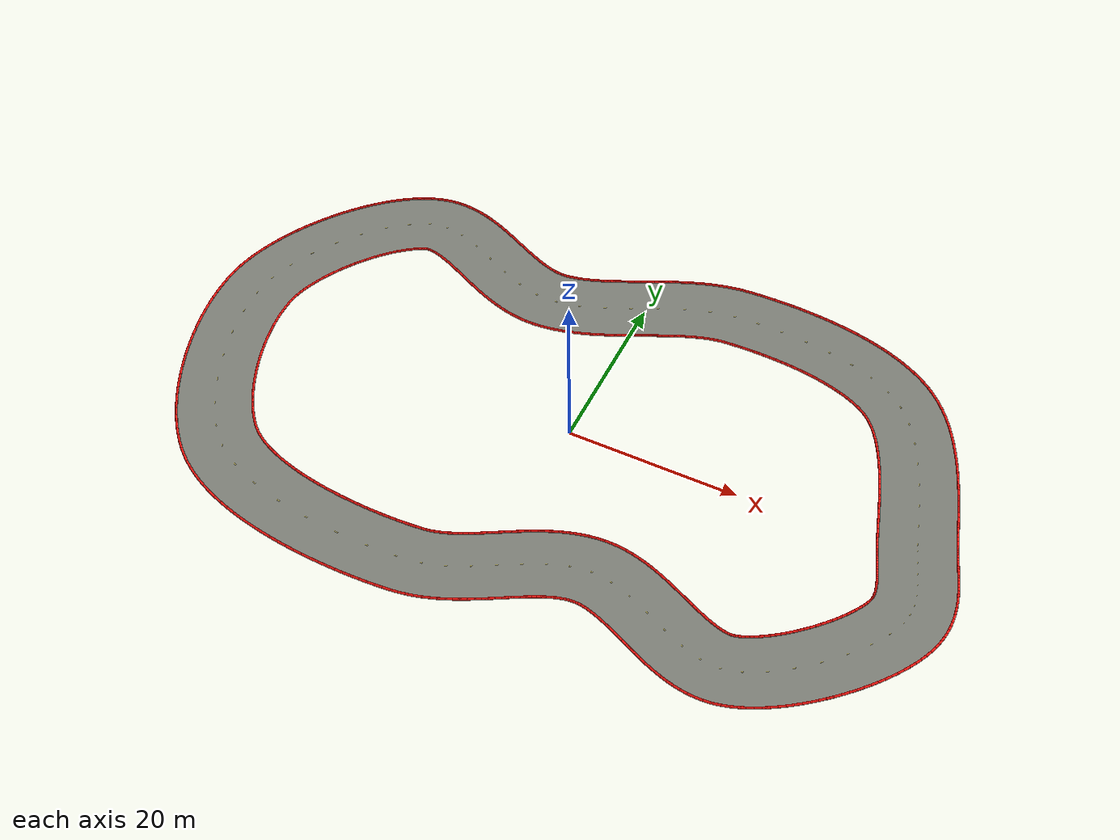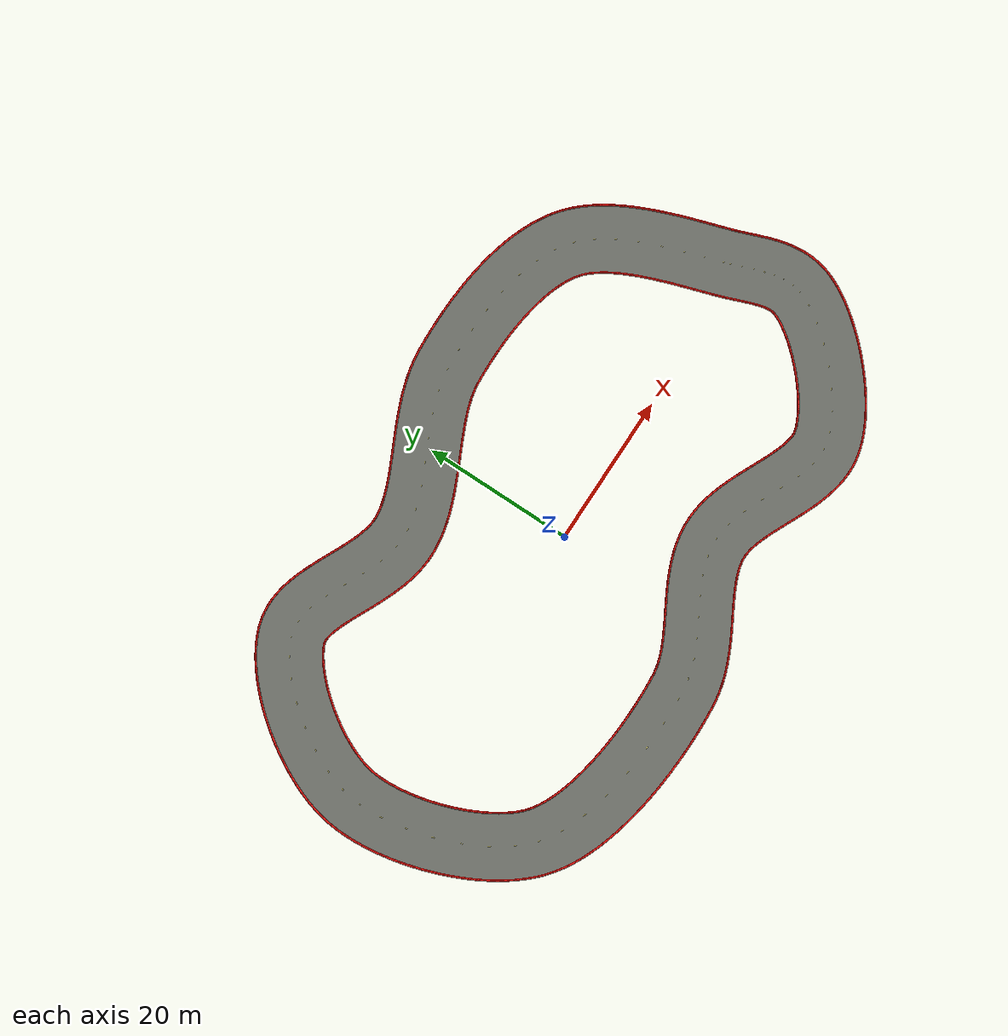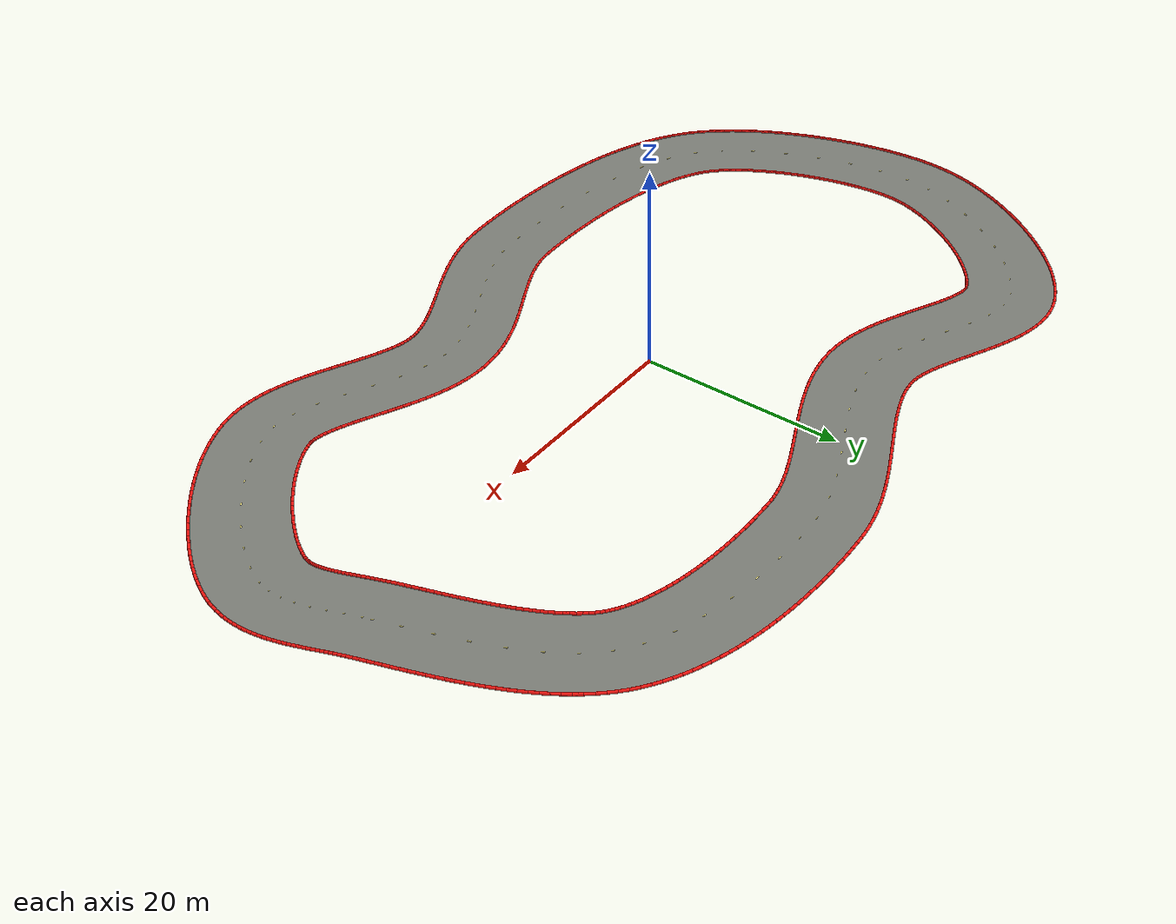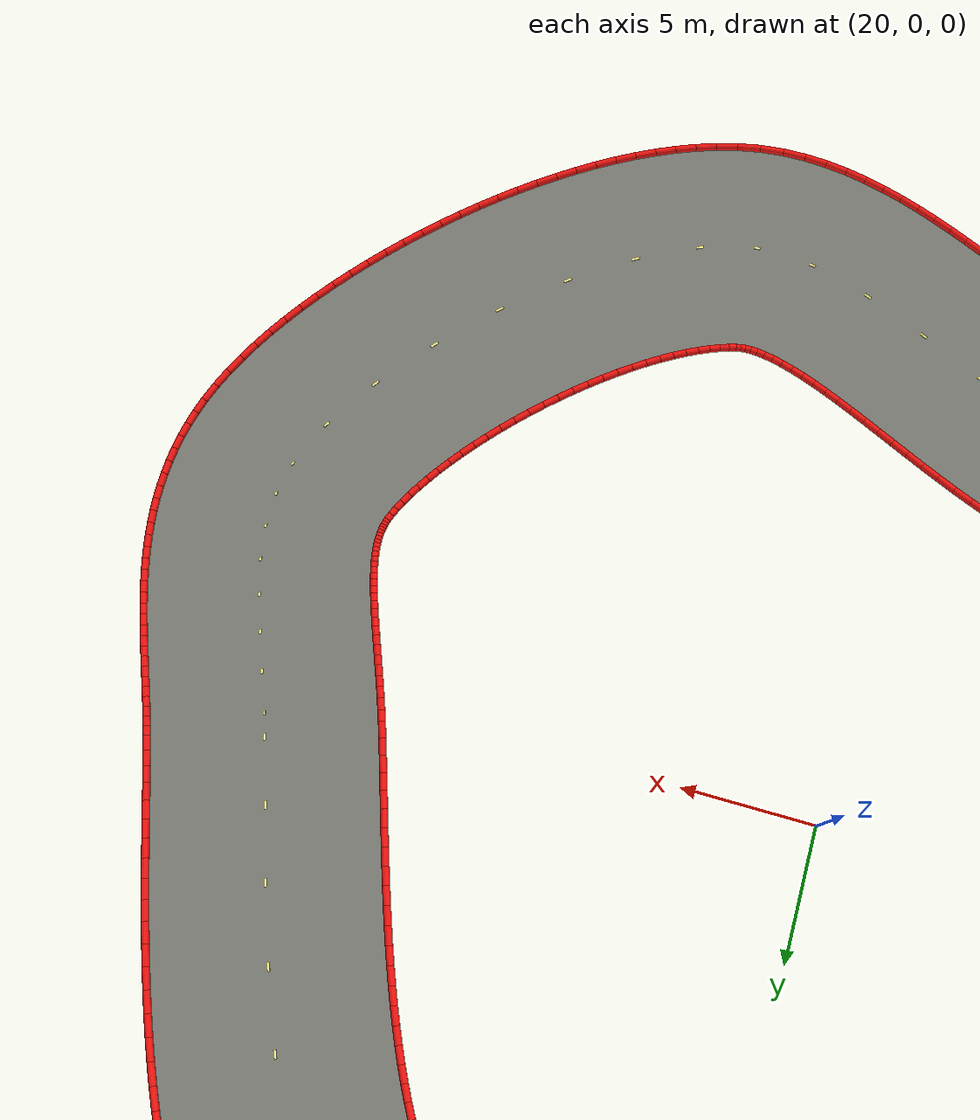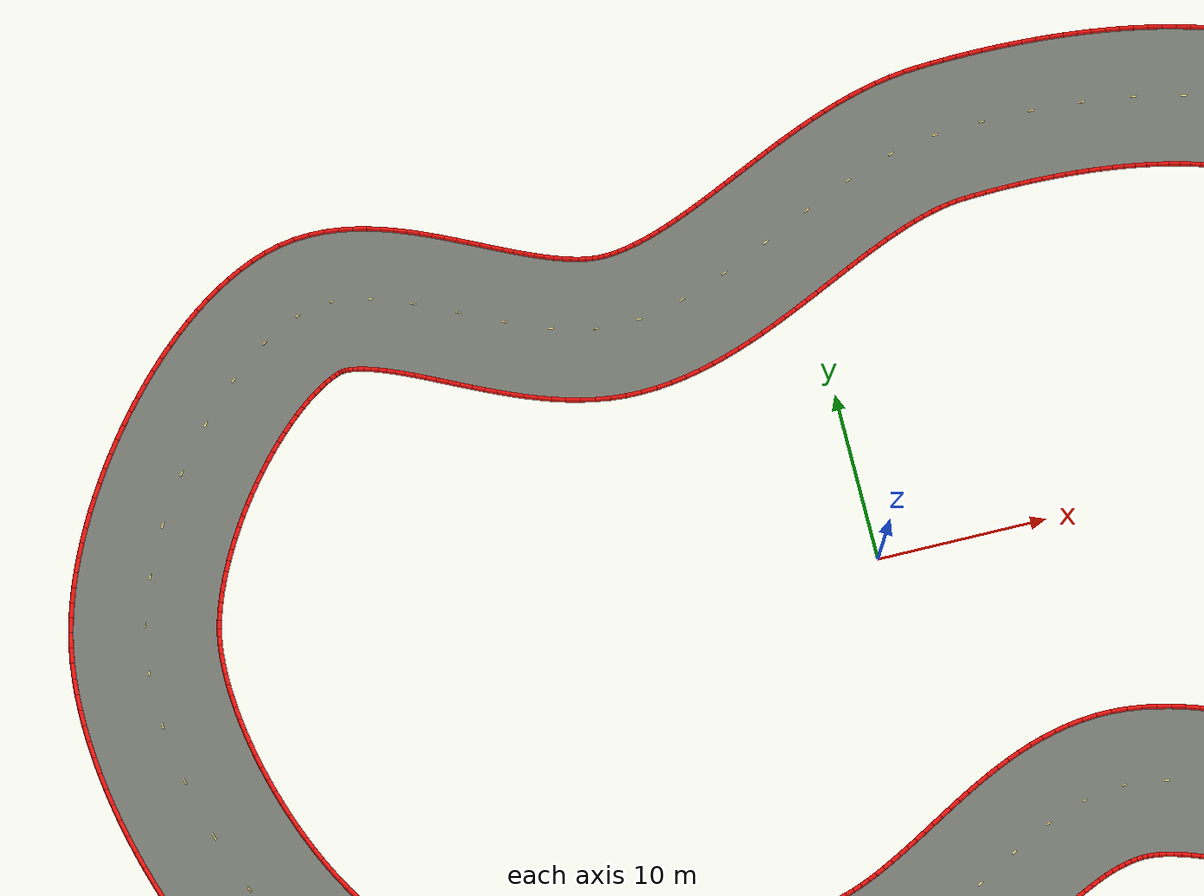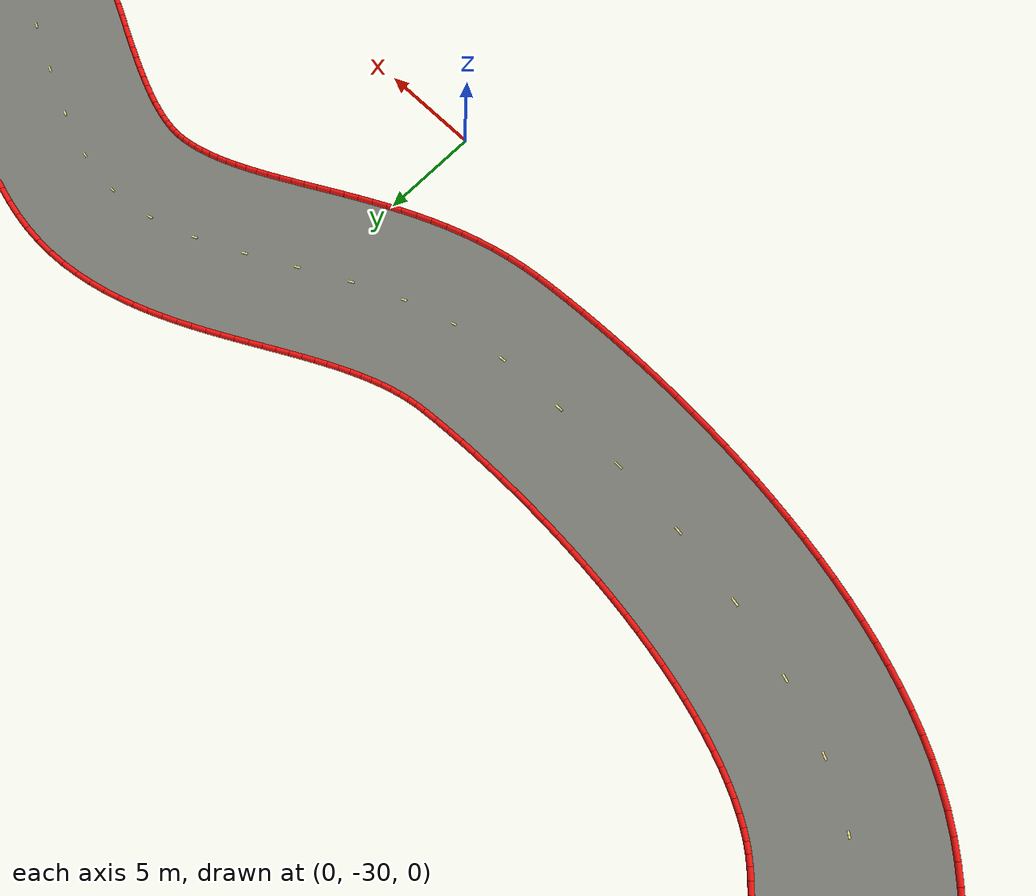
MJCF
<mujoco model="kidney_track_visuals">
  <asset>
    <mesh name="track_surface_mesh" inertia="shell" vertex="35.98116 0.61747 0.02200 35.78887 1.18525 0.02200 35.59645 1.76556 0.02200 35.40237 2.35907 0.02200 35.20581 2.96464 0.02200 35.00606 3.58091 0.02200 34.80253 4.20632 0.02200 34.59469 4.83921 0.02200 34.38207 5.47777 0.02200 34.16428 6.12012 0.02200 33.94094 6.76427 0.02200 33.71176 7.40819 0.02200 33.47648 8.04976 0.02200 33.23490 8.68681 0.02200 32.98686 9.31712 0.02200 32.73229 9.93843 0.02200 32.47120 10.54841 0.02200 32.20365 11.14471 0.02200 31.92984 11.72493 0.02200 31.65007 12.28666 0.02200 31.36478 12.82746 0.02200 31.07457 13.34490 0.02200 30.78021 13.83659 0.02200 30.48270 14.30019 0.02200 30.18323 14.73349 0.02200 29.88324 15.13445 0.02200 29.58438 15.50132 0.02200 29.28852 15.83271 0.02200 28.99762 16.12778 0.02200 28.71363 16.38629 0.02200 28.42641 16.61782 0.02200 28.09369 16.85586 0.02200 27.72216 17.09549 0.02200 27.31992 17.32965 0.02200 26.88776 17.55715 0.02200 26.42674 17.77688 0.02200 25.93817 17.98786 0.02200 25.42351 18.18926 0.02200 24.88435 18.38038 0.02200 24.32234 18.56066 0.02200 23.73921 18.72965 0.02200 23.13670 18.88705 0.02200 22.51657 19.03265 0.02200 21.88057 19.16631 0.02200 21.23047 19.28800 0.02200 20.56801 19.39776 0.02200 19.89489 19.49565 0.02200 19.21284 19.58183 0.02200 18.52355 19.65648 0.02200 17.82868 19.71982 0.02200 17.12989 19.77211 0.02200 16.42883 19.81362 0.02200 15.72713 19.84467 0.02200 15.02641 19.86559 0.02200 14.32826 19.87672 0.02200 13.63431 19.87842 0.02200 12.94615 19.87109 0.02200 12.26538 19.85511 0.02200 11.59359 19.83090 0.02200 10.93241 19.79887 0.02200 10.32762 19.76265 0.02200 9.79838 19.71372 0.02200 9.29558 19.64031 0.02200 8.77210 19.53893 0.02200 8.22841 19.40980 0.02200 7.66535 19.25352 0.02200 7.08402 19.07105 0.02200 6.48557 18.86373 0.02200 5.87118 18.63317 0.02200 5.24198 18.38123 0.02200 4.59899 18.10998 0.02200 3.94309 17.82165 0.02200 3.27505 17.51859 0.02200 2.59547 17.20324 0.02200 1.90477 16.87812 0.02200 1.20326 16.54584 0.02200 0.49104 16.20901 0.02200 -0.23192 15.87035 0.02200 -0.96583 15.53261 0.02200 -1.71108 15.19862 0.02200 -2.46821 14.87130 0.02200 -3.23795 14.55368 0.02200 -4.02116 14.24895 0.02200 -4.81886 13.96051 0.02200 -5.63219 13.69202 0.02200 -6.46231 13.44743 0.02200 -7.31038 13.23111 0.02200 -8.17737 13.04784 0.02200 -9.06392 12.90290 0.02200 -9.97011 12.80201 0.02200 -10.90693 12.75102 0.02200 -11.81681 12.76148 0.02200 -12.72022 12.83369 0.02200 -13.59613 12.95900 0.02200 -14.44423 13.12893 0.02200 -15.26527 13.33586 0.02200 -16.06057 13.57303 0.02200 -16.83171 13.83448 0.02200 -17.58023 14.11488 0.02200 -18.30749 14.40945 0.02200 -19.01461 14.71377 0.02200 -19.70240 15.02370 0.02200 -20.37134 15.33531 0.02200 -21.02155 15.64480 0.02200 -21.65283 15.94849 0.02200 -22.26461 16.24274 0.02200 -22.85592 16.52403 0.02200 -23.42542 16.78890 0.02200 -23.97132 17.03401 0.02200 -24.49136 17.25621 0.02200 -24.98279 17.45266 0.02200 -25.44235 17.62093 0.02200 -25.86628 17.75924 0.02200 -26.25047 17.86672 0.02200 -26.59070 17.94370 0.02200 -26.88315 17.99210 0.02200 -27.12522 18.01557 0.02200 -27.31668 18.01943 0.02200 -27.46100 18.00996 0.02200 -27.56644 17.99293 0.02200 -27.68509 17.95853 0.02200 -27.92347 17.86708 0.02200 -28.23496 17.72598 0.02200 -28.58159 17.54406 0.02200 -28.95726 17.32110 0.02200 -29.35640 17.05784 0.02200 -29.77404 16.75571 0.02200 -30.20572 16.41654 0.02200 -30.64748 16.04247 0.02200 -31.09574 15.63581 0.02200 -31.54730 15.19898 0.02200 -31.99921 14.73450 0.02200 -32.44877 14.24491 0.02200 -32.89347 13.73280 0.02200 -33.33095 13.20077 0.02200 -33.75898 12.65148 0.02200 -34.17545 12.08758 0.02200 -34.57831 11.51177 0.02200 -34.96564 10.92682 0.02200 -35.33554 10.33552 0.02200 -35.68620 9.74076 0.02200 -36.01588 9.14548 0.02200 -36.32290 8.55278 0.02200 -36.60566 7.96584 0.02200 -36.86268 7.38804 0.02200 -37.09259 6.82294 0.02200 -37.29417 6.27431 0.02200 -37.46647 5.74620 0.02200 -37.60880 5.24294 0.02200 -37.72092 4.76919 0.02200 -37.80363 4.32695 0.02200 -37.86941 3.83607 0.02200 -37.91536 3.30151 0.02200 -37.93996 2.72498 0.02200 -37.94187 2.11119 0.02200 -37.92026 1.46466 0.02200 -37.87469 0.78970 0.02200 -37.80503 0.09039 0.02200 -37.71137 -0.62934 0.02200 -37.59398 -1.36573 0.02200 -37.45327 -2.11516 0.02200 -37.28977 -2.87412 0.02200 -37.10410 -3.63917 0.02200 -36.89695 -4.40698 0.02200 -36.66910 -5.17424 0.02200 -36.42139 -5.93772 0.02200 -36.15475 -6.69419 0.02200 -35.87016 -7.44046 0.02200 -35.56870 -8.17335 0.02200 -35.25155 -8.88969 0.02200 -34.91998 -9.58631 0.02200 -34.57540 -10.26002 0.02200 -34.21936 -10.90765 0.02200 -33.85360 -11.52603 0.02200 -33.48006 -12.11202 0.02200 -33.10096 -12.66249 0.02200 -32.71880 -13.17443 0.02200 -32.33641 -13.64494 0.02200 -31.95705 -14.07136 0.02200 -31.58436 -14.45138 0.02200 -31.22735 -14.77899 0.02200 -30.84242 -15.09033 0.02200 -30.41521 -15.39365 0.02200 -29.93642 -15.69454 0.02200 -29.40776 -15.99002 0.02200 -28.83164 -16.27748 0.02200 -28.21091 -16.55472 0.02200 -27.54872 -16.81995 0.02200 -26.84836 -17.07176 0.02200 -26.11322 -17.30906 0.02200 -25.34669 -17.53106 0.02200 -24.55218 -17.73720 0.02200 -23.73304 -17.92713 0.02200 -22.89258 -18.10066 0.02200 -22.03408 -18.25774 0.02200 -21.16075 -18.39842 0.02200 -20.27577 -18.52285 0.02200 -19.38227 -18.63125 0.02200 -18.48336 -18.72391 0.02200 -17.58211 -18.80117 0.02200 -16.68155 -18.86342 0.02200 -15.78473 -18.91106 0.02200 -14.89466 -18.94456 0.02200 -14.01436 -18.96439 0.02200 -13.14686 -18.97108 0.02200 -12.29520 -18.96516 0.02200 -11.46246 -18.94719 0.02200 -10.65176 -18.91777 0.02200 -9.86629 -18.87754 0.02200 -9.10933 -18.82717 0.02200 -8.42453 -18.77126 0.02200 -7.95064 -18.71596 0.02200 -7.51264 -18.64031 0.02200 -7.06574 -18.54024 0.02200 -6.60863 -18.41576 0.02200 -6.14054 -18.26710 0.02200 -5.66114 -18.09471 0.02200 -5.17041 -17.89932 0.02200 -4.66848 -17.68196 0.02200 -4.15561 -17.44394 0.02200 -3.63202 -17.18680 0.02200 -3.09793 -16.91228 0.02200 -2.55344 -16.62232 0.02200 -1.99852 -16.31899 0.02200 -1.43301 -16.00448 0.02200 -0.85657 -15.68107 0.02200 -0.26870 -15.35116 0.02200 0.33127 -15.01721 0.02200 0.94424 -14.68179 0.02200 1.57124 -14.34760 0.02200 2.21352 -14.01746 0.02200 2.87249 -13.69437 0.02200 3.54969 -13.38158 0.02200 4.24677 -13.08259 0.02200 4.96540 -12.80129 0.02200 5.70714 -12.54196 0.02200 6.47334 -12.30931 0.02200 7.26493 -12.10856 0.02200 8.08219 -11.94533 0.02200 8.92454 -11.82553 0.02200 9.80101 -11.75466 0.02200 10.69582 -11.74378 0.02200 11.58397 -11.79531 0.02200 12.44565 -11.90088 0.02200 13.28042 -12.05189 0.02200 14.08905 -12.24065 0.02200 14.87294 -12.46036 0.02200 15.63376 -12.70511 0.02200 16.37320 -12.96965 0.02200 17.09274 -13.24932 0.02200 17.79366 -13.53986 0.02200 18.47689 -13.83730 0.02200 19.14306 -14.13790 0.02200 19.79245 -14.43808 0.02200 20.42502 -14.73435 0.02200 21.04040 -15.02332 0.02200 21.63787 -15.30165 0.02200 22.21637 -15.56612 0.02200 22.77446 -15.81356 0.02200 23.31033 -16.04099 0.02200 23.82175 -16.24563 0.02200 24.30609 -16.42502 0.02200 24.76031 -16.57717 0.02200 25.18106 -16.70074 0.02200 25.56483 -16.79524 0.02200 25.90825 -16.86129 0.02200 26.20859 -16.90085 0.02200 26.46448 -16.91719 0.02200 26.67686 -16.91470 0.02200 26.84986 -16.89816 0.02200 27.02976 -16.86223 0.02200 27.29346 -16.78768 0.02200 27.62864 -16.67363 0.02200 27.99882 -16.52629 0.02200 28.39830 -16.34570 0.02200 28.82190 -16.13265 0.02200 29.26495 -15.88844 0.02200 29.72326 -15.61470 0.02200 30.19301 -15.31330 0.02200 30.67072 -14.98630 0.02200 31.15318 -14.63581 0.02200 31.63743 -14.26405 0.02200 32.12066 -13.87330 0.02200 32.60023 -13.46586 0.02200 33.07361 -13.04410 0.02200 33.53835 -12.61041 0.02200 33.99210 -12.16725 0.02200 34.43253 -11.71714 0.02200 34.85739 -11.26266 0.02200 35.26442 -10.80650 0.02200 35.65140 -10.35149 0.02200 36.01612 -9.90060 0.02200 36.35636 -9.45702 0.02200 36.66995 -9.02421 0.02200 36.95470 -8.60600 0.02200 37.20849 -8.20665 0.02200 37.42930 -7.83109 0.02200 37.61532 -7.48502 0.02200 37.76508 -7.17524 0.02200 37.87784 -6.90990 0.02200 37.95983 -6.68108 0.02200 37.99073 -6.57525 0.02200 38.01818 -6.46110 0.02200 38.03934 -6.34810 0.02200 38.05491 -6.23358 0.02200 38.06518 -6.11499 0.02200 38.07009 -5.98999 0.02200 38.06933 -5.85657 0.02200 38.06236 -5.71306 0.02200 38.04858 -5.55814 0.02200 38.02734 -5.39088 0.02200 37.99804 -5.21063 0.02200 37.96020 -5.01703 0.02200 37.91342 -4.80994 0.02200 37.85747 -4.58937 0.02200 37.79226 -4.35545 0.02200 37.71783 -4.10839 0.02200 37.63437 -3.84845 0.02200 37.54219 -3.57587 0.02200 37.44170 -3.29090 0.02200 37.33340 -2.99379 0.02200 37.21789 -2.68471 0.02200 37.09581 -2.36383 0.02200 36.96790 -2.03127 0.02200 36.83493 -1.68711 0.02200 36.69772 -1.33137 0.02200 36.55713 -0.96406 0.02200 36.41407 -0.58515 0.02200 36.26948 -0.19457 0.02200 36.12433 0.20776 0.02200 44.01884 3.38253 0.02200 43.84844 3.88586 0.02200 43.67004 4.42396 0.02200 43.48429 4.99206 0.02200 43.29112 5.58717 0.02200 43.09037 6.20655 0.02200 42.88174 6.84762 0.02200 42.66487 7.50794 0.02200 42.43936 8.18520 0.02200 42.20472 8.87717 0.02200 41.96042 9.58171 0.02200 41.70590 10.29675 0.02200 41.44053 11.02028 0.02200 41.16362 11.75035 0.02200 40.87445 12.48508 0.02200 40.57220 13.22261 0.02200 40.25601 13.96114 0.02200 39.92489 14.69892 0.02200 39.57779 15.43422 0.02200 39.21351 16.16535 0.02200 38.83074 16.89062 0.02200 38.42800 17.60835 0.02200 38.00362 18.31681 0.02200 37.55573 19.01423 0.02200 37.08226 19.69870 0.02200 36.58089 20.36813 0.02200 36.04906 21.02018 0.02200 35.48406 21.65210 0.02200 34.88302 22.26064 0.02200 34.24311 22.84189 0.02200 33.57359 23.38218 0.02200 32.87662 23.88250 0.02200 32.16750 24.34042 0.02200 31.44083 24.76390 0.02200 30.69857 25.15502 0.02200 29.94237 25.51576 0.02200 29.17365 25.84800 0.02200 28.39368 26.15344 0.02200 27.60360 26.43368 0.02200 26.80446 26.69017 0.02200 25.99727 26.92423 0.02200 25.18302 27.13706 0.02200 24.36266 27.32975 0.02200 23.53716 27.50332 0.02200 22.70750 27.65869 0.02200 21.87466 27.79672 0.02200 21.03965 27.91821 0.02200 20.20347 28.02391 0.02200 19.36716 28.11452 0.02200 18.53177 28.19070 0.02200 17.69838 28.25308 0.02200 16.86806 28.30227 0.02200 16.04190 28.33884 0.02200 15.22102 28.36336 0.02200 14.40653 28.37636 0.02200 13.59954 28.37835 0.02200 12.80119 28.36985 0.02200 12.01260 28.35135 0.02200 11.23489 28.32333 0.02200 10.46917 28.28624 0.02200 9.67238 28.23735 0.02200 8.78844 28.15351 0.02200 7.87671 28.02105 0.02200 6.98454 27.84885 0.02200 6.11171 27.64203 0.02200 5.25760 27.40537 0.02200 4.42140 27.14325 0.02200 3.60216 26.85973 0.02200 2.79896 26.55853 0.02200 2.01091 26.24317 0.02200 1.23724 25.91694 0.02200 0.47730 25.58298 0.02200 -0.26942 25.24430 0.02200 -1.00328 24.90382 0.02200 -1.72448 24.56438 0.02200 -2.43306 24.22875 0.02200 -3.12890 23.89966 0.02200 -3.81170 23.57977 0.02200 -4.48102 23.27170 0.02200 -5.13624 22.97797 0.02200 -5.77656 22.70104 0.02200 -6.40102 22.44322 0.02200 -7.00850 22.20670 0.02200 -7.59774 21.99343 0.02200 -8.16738 21.80514 0.02200 -8.71598 21.64322 0.02200 -9.24217 21.50868 0.02200 -9.74473 21.40208 0.02200 -10.22276 21.32353 0.02200 -10.67595 21.27265 0.02200 -11.09307 21.24898 0.02200 -11.42780 21.25257 0.02200 -11.77508 21.28098 0.02200 -12.15498 21.33593 0.02200 -12.56681 21.41900 0.02200 -13.00884 21.53089 0.02200 -13.47876 21.67144 0.02200 -13.97402 21.83970 0.02200 -14.49211 22.03407 0.02200 -15.03066 22.25243 0.02200 -15.58758 22.49229 0.02200 -16.16109 22.75086 0.02200 -16.74972 23.02516 0.02200 -17.35236 23.31207 0.02200 -17.96823 23.60836 0.02200 -18.59694 23.91074 0.02200 -19.23845 24.21584 0.02200 -19.89314 24.52020 0.02200 -20.56180 24.82022 0.02200 -21.24572 25.11215 0.02200 -21.94666 25.39192 0.02200 -22.66690 25.65504 0.02200 -23.40923 25.89637 0.02200 -24.17677 26.10988 0.02200 -24.97276 26.28830 0.02200 -25.80003 26.42281 0.02200 -26.66020 26.50284 0.02200 -27.55253 26.51615 0.02200 -28.47255 26.44956 0.02200 -29.41104 26.29036 0.02200 -30.31491 26.04147 0.02200 -31.16629 25.72418 0.02200 -31.95689 25.36779 0.02200 -32.72170 24.96763 0.02200 -33.46386 24.52807 0.02200 -34.18595 24.05252 0.02200 -34.89001 23.54371 0.02200 -35.57749 23.00396 0.02200 -36.24942 22.43530 0.02200 -36.90638 21.83956 0.02200 -37.54861 21.21847 0.02200 -38.17610 20.57368 0.02200 -38.78856 19.90680 0.02200 -39.38556 19.21939 0.02200 -39.96647 18.51300 0.02200 -40.53056 17.78915 0.02200 -41.07698 17.04931 0.02200 -41.60478 16.29495 0.02200 -42.11295 15.52746 0.02200 -42.60040 14.74820 0.02200 -43.06597 13.95845 0.02200 -43.50844 13.15940 0.02200 -43.92652 12.35212 0.02200 -44.31882 11.53757 0.02200 -44.68388 10.71653 0.02200 -45.02010 9.88962 0.02200 -45.32571 9.05719 0.02200 -45.59871 8.21936 0.02200 -45.83681 7.37595 0.02200 -46.03729 6.52646 0.02200 -46.19637 5.67305 0.02200 -46.31818 4.76791 0.02200 -46.39767 3.84959 0.02200 -46.43769 2.92146 0.02200 -46.44092 1.98389 0.02200 -46.40952 1.03744 0.02200 -46.34525 0.08287 0.02200 -46.24959 -0.87883 0.02200 -46.12377 -1.84649 0.02200 -45.96886 -2.81881 0.02200 -45.78576 -3.79434 0.02200 -45.57530 -4.77150 0.02200 -45.33818 -5.74864 0.02200 -45.07504 -6.72404 0.02200 -44.78643 -7.69592 0.02200 -44.47285 -8.66243 0.02200 -44.13469 -9.62173 0.02200 -43.77231 -10.57192 0.02200 -43.38595 -11.51112 0.02200 -42.97578 -12.43741 0.02200 -42.54185 -13.34890 0.02200 -42.08408 -14.24369 0.02200 -41.60226 -15.11986 0.02200 -41.09598 -15.97552 0.02200 -40.56461 -16.80874 0.02200 -40.00730 -17.61755 0.02200 -39.42286 -18.39990 0.02200 -38.80979 -19.15361 0.02200 -38.16617 -19.87625 0.02200 -37.48968 -20.56508 0.02200 -36.77265 -21.22101 0.02200 -35.98007 -21.86193 0.02200 -35.14301 -22.45750 0.02200 -34.27600 -23.00330 0.02200 -33.38248 -23.50344 0.02200 -32.46524 -23.96168 0.02200 -31.52662 -24.38135 0.02200 -30.56865 -24.76539 0.02200 -29.59323 -25.11636 0.02200 -28.60216 -25.43649 0.02200 -27.59722 -25.72771 0.02200 -26.58021 -25.99172 0.02200 -25.55295 -26.23002 0.02200 -24.51732 -26.44394 0.02200 -23.47524 -26.63468 0.02200 -22.42867 -26.80332 0.02200 -21.37961 -26.95087 0.02200 -20.33014 -27.07824 0.02200 -19.28232 -27.18628 0.02200 -18.23828 -27.27581 0.02200 -17.20015 -27.34758 0.02200 -16.17011 -27.40232 0.02200 -15.15030 -27.44071 0.02200 -14.14289 -27.46342 0.02200 -13.15006 -27.47108 0.02200 -12.17393 -27.46429 0.02200 -11.21662 -27.44363 0.02200 -10.28020 -27.40964 0.02200 -9.36665 -27.36284 0.02200 -8.47790 -27.30369 0.02200 -7.57547 -27.22874 0.02200 -6.72898 -27.12771 0.02200 -5.86358 -26.97882 0.02200 -5.02312 -26.79116 0.02200 -4.20799 -26.56972 0.02200 -3.41801 -26.31930 0.02200 -2.65259 -26.04447 0.02200 -1.91084 -25.74949 0.02200 -1.19168 -25.43837 0.02200 -0.49394 -25.11481 0.02200 0.18356 -24.78228 0.02200 0.84194 -24.44404 0.02200 1.48223 -24.10319 0.02200 2.10534 -23.76267 0.02200 2.71204 -23.42530 0.02200 3.30291 -23.09381 0.02200 3.87839 -22.77084 0.02200 4.43871 -22.45891 0.02200 4.98395 -22.16048 0.02200 5.51396 -21.87787 0.02200 6.02844 -21.61327 0.02200 6.52690 -21.36869 0.02200 7.00874 -21.14592 0.02200 7.47324 -20.94643 0.02200 7.91966 -20.77139 0.02200 8.34734 -20.62152 0.02200 8.75589 -20.49710 0.02200 9.14530 -20.39796 0.02200 9.51621 -20.32349 0.02200 9.87015 -20.27277 0.02200 10.19899 -20.24534 0.02200 10.49945 -20.24151 0.02200 10.81608 -20.26056 0.02200 11.16771 -20.30427 0.02200 11.55377 -20.37468 0.02200 11.97255 -20.47292 0.02200 12.42163 -20.59922 0.02200 12.89837 -20.75294 0.02200 13.40011 -20.93274 0.02200 13.92435 -21.13674 0.02200 14.46886 -21.36263 0.02200 15.03171 -21.60780 0.02200 15.61130 -21.86944 0.02200 16.20635 -22.14456 0.02200 16.81591 -22.43008 0.02200 17.43940 -22.72285 0.02200 18.07652 -23.01961 0.02200 18.72737 -23.31704 0.02200 19.39239 -23.61174 0.02200 20.07242 -23.90012 0.02200 20.76870 -24.17840 0.02200 21.48288 -24.44247 0.02200 22.21701 -24.68776 0.02200 22.97345 -24.90906 0.02200 23.75474 -25.10027 0.02200 24.56326 -25.25421 0.02200 25.40076 -25.36237 0.02200 26.26762 -25.41490 0.02200 27.16193 -25.40085 0.02200 28.07855 -25.30889 0.02200 28.97024 -25.13777 0.02200 29.79229 -24.91208 0.02200 30.56370 -24.65081 0.02200 31.31760 -24.35161 0.02200 32.05633 -24.01831 0.02200 32.78169 -23.65396 0.02200 33.49500 -23.26114 0.02200 34.19710 -22.84206 0.02200 34.88845 -22.39870 0.02200 35.56916 -21.93289 0.02200 36.23909 -21.44636 0.02200 36.89784 -20.94074 0.02200 37.54485 -20.41762 0.02200 38.17942 -19.87856 0.02200 38.80071 -19.32505 0.02200 39.40780 -18.75855 0.02200 39.99971 -18.18046 0.02200 40.57537 -17.59213 0.02200 41.13371 -16.99483 0.02200 41.67361 -16.38971 0.02200 42.19394 -15.77783 0.02200 42.69354 -15.16007 0.02200 43.17127 -14.53708 0.02200 43.62596 -13.90928 0.02200 44.05643 -13.27670 0.02200 44.46143 -12.63891 0.02200 44.83963 -11.99487 0.02200 45.18949 -11.34272 0.02200 45.50910 -10.67954 0.02200 45.79586 -10.00100 0.02200 46.04017 -9.31892 0.02200 46.20148 -8.77381 0.02200 46.32997 -8.23989 0.02200 46.42997 -7.70729 0.02200 46.50225 -7.17826 0.02200 46.54801 -6.65491 0.02200 46.56879 -6.13915 0.02200 46.56637 -5.63257 0.02200 46.54278 -5.13643 0.02200 46.50009 -4.65159 0.02200 46.44044 -4.17859 0.02200 46.36590 -3.71763 0.02200 46.27844 -3.26865 0.02200 46.17993 -2.83137 0.02200 46.07210 -2.40535 0.02200 45.95649 -1.99003 0.02200 45.83456 -1.58478 0.02200 45.70760 -1.18892 0.02200 45.57677 -0.80178 0.02200 45.44315 -0.42267 0.02200 45.30771 -0.05094 0.02200 45.17134 0.31404 0.02200 45.03487 0.67283 0.02200 44.89905 1.02600 0.02200 44.76459 1.37403 0.02200 44.63214 1.71740 0.02200 44.50233 2.05652 0.02200 44.37572 2.39180 0.02200 44.25286 2.72359 0.02200 44.13425 3.05224 0.02200" face="0 331 1 0 330 331 1 332 2 1 331 332 2 333 3 2 332 333 3 334 4 3 333 334 4 335 5 4 334 335 5 336 6 5 335 336 6 337 7 6 336 337 7 338 8 7 337 338 8 339 9 8 338 339 9 340 10 9 339 340 10 341 11 10 340 341 11 342 12 11 341 342 12 343 13 12 342 343 13 344 14 13 343 344 14 345 15 14 344 345 15 346 16 15 345 346 16 347 17 16 346 347 17 348 18 17 347 348 18 349 19 18 348 349 19 350 20 19 349 350 20 351 21 20 350 351 21 352 22 21 351 352 22 353 23 22 352 353 23 354 24 23 353 354 24 355 25 24 354 355 25 356 26 25 355 356 26 357 27 26 356 357 27 358 28 27 357 358 28 359 29 28 358 359 29 360 30 29 359 360 30 361 31 30 360 361 31 362 32 31 361 362 32 363 33 32 362 363 33 364 34 33 363 364 34 365 35 34 364 365 35 366 36 35 365 366 36 367 37 36 366 367 37 368 38 37 367 368 38 369 39 38 368 369 39 370 40 39 369 370 40 371 41 40 370 371 41 372 42 41 371 372 42 373 43 42 372 373 43 374 44 43 373 374 44 375 45 44 374 375 45 376 46 45 375 376 46 377 47 46 376 377 47 378 48 47 377 378 48 379 49 48 378 379 49 380 50 49 379 380 50 381 51 50 380 381 51 382 52 51 381 382 52 383 53 52 382 383 53 384 54 53 383 384 54 385 55 54 384 385 55 386 56 55 385 386 56 387 57 56 386 387 57 388 58 57 387 388 58 389 59 58 388 389 59 390 60 59 389 390 60 391 61 60 390 391 61 392 62 61 391 392 62 393 63 62 392 393 63 394 64 63 393 394 64 395 65 64 394 395 65 396 66 65 395 396 66 397 67 66 396 397 67 398 68 67 397 398 68 399 69 68 398 399 69 400 70 69 399 400 70 401 71 70 400 401 71 402 72 71 401 402 72 403 73 72 402 403 73 404 74 73 403 404 74 405 75 74 404 405 75 406 76 75 405 406 76 407 77 76 406 407 77 408 78 77 407 408 78 409 79 78 408 409 79 410 80 79 409 410 80 411 81 80 410 411 81 412 82 81 411 412 82 413 83 82 412 413 83 414 84 83 413 414 84 415 85 84 414 415 85 416 86 85 415 416 86 417 87 86 416 417 87 418 88 87 417 418 88 419 89 88 418 419 89 420 90 89 419 420 90 421 91 90 420 421 91 422 92 91 421 422 92 423 93 92 422 423 93 424 94 93 423 424 94 425 95 94 424 425 95 426 96 95 425 426 96 427 97 96 426 427 97 428 98 97 427 428 98 429 99 98 428 429 99 430 100 99 429 430 100 431 101 100 430 431 101 432 102 101 431 432 102 433 103 102 432 433 103 434 104 103 433 434 104 435 105 104 434 435 105 436 106 105 435 436 106 437 107 106 436 437 107 438 108 107 437 438 108 439 109 108 438 439 109 440 110 109 439 440 110 441 111 110 440 441 111 442 112 111 441 442 112 443 113 112 442 443 113 444 114 113 443 444 114 445 115 114 444 445 115 446 116 115 445 446 116 447 117 116 446 447 117 448 118 117 447 448 118 449 119 118 448 449 119 450 120 119 449 450 120 451 121 120 450 451 121 452 122 121 451 452 122 453 123 122 452 453 123 454 124 123 453 454 124 455 125 124 454 455 125 456 126 125 455 456 126 457 127 126 456 457 127 458 128 127 457 458 128 459 129 128 458 459 129 460 130 129 459 460 130 461 131 130 460 461 131 462 132 131 461 462 132 463 133 132 462 463 133 464 134 133 463 464 134 465 135 134 464 465 135 466 136 135 465 466 136 467 137 136 466 467 137 468 138 137 467 468 138 469 139 138 468 469 139 470 140 139 469 470 140 471 141 140 470 471 141 472 142 141 471 472 142 473 143 142 472 473 143 474 144 143 473 474 144 475 145 144 474 475 145 476 146 145 475 476 146 477 147 146 476 477 147 478 148 147 477 478 148 479 149 148 478 479 149 480 150 149 479 480 150 481 151 150 480 481 151 482 152 151 481 482 152 483 153 152 482 483 153 484 154 153 483 484 154 485 155 154 484 485 155 486 156 155 485 486 156 487 157 156 486 487 157 488 158 157 487 488 158 489 159 158 488 489 159 490 160 159 489 490 160 491 161 160 490 491 161 492 162 161 491 492 162 493 163 162 492 493 163 494 164 163 493 494 164 495 165 164 494 495 165 496 166 165 495 496 166 497 167 166 496 497 167 498 168 167 497 498 168 499 169 168 498 499 169 500 170 169 499 500 170 501 171 170 500 501 171 502 172 171 501 502 172 503 173 172 502 503 173 504 174 173 503 504 174 505 175 174 504 505 175 506 176 175 505 506 176 507 177 176 506 507 177 508 178 177 507 508 178 509 179 178 508 509 179 510 180 179 509 510 180 511 181 180 510 511 181 512 182 181 511 512 182 513 183 182 512 513 183 514 184 183 513 514 184 515 185 184 514 515 185 516 186 185 515 516 186 517 187 186 516 517 187 518 188 187 517 518 188 519 189 188 518 519 189 520 190 189 519 520 190 521 191 190 520 521 191 522 192 191 521 522 192 523 193 192 522 523 193 524 194 193 523 524 194 525 195 194 524 525 195 526 196 195 525 526 196 527 197 196 526 527 197 528 198 197 527 528 198 529 199 198 528 529 199 530 200 199 529 530 200 531 201 200 530 531 201 532 202 201 531 532 202 533 203 202 532 533 203 534 204 203 533 534 204 535 205 204 534 535 205 536 206 205 535 536 206 537 207 206 536 537 207 538 208 207 537 538 208 539 209 208 538 539 209 540 210 209 539 540 210 541 211 210 540 541 211 542 212 211 541 542 212 543 213 212 542 543 213 544 214 213 543 544 214 545 215 214 544 545 215 546 216 215 545 546 216 547 217 216 546 547 217 548 218 217 547 548 218 549 219 218 548 549 219 550 220 219 549 550 220 551 221 220 550 551 221 552 222 221 551 552 222 553 223 222 552 553 223 554 224 223 553 554 224 555 225 224 554 555 225 556 226 225 555 556 226 557 227 226 556 557 227 558 228 227 557 558 228 559 229 228 558 559 229 560 230 229 559 560 230 561 231 230 560 561 231 562 232 231 561 562 232 563 233 232 562 563 233 564 234 233 563 564 234 565 235 234 564 565 235 566 236 235 565 566 236 567 237 236 566 567 237 568 238 237 567 568 238 569 239 238 568 569 239 570 240 239 569 570 240 571 241 240 570 571 241 572 242 241 571 572 242 573 243 242 572 573 243 574 244 243 573 574 244 575 245 244 574 575 245 576 246 245 575 576 246 577 247 246 576 577 247 578 248 247 577 578 248 579 249 248 578 579 249 580 250 249 579 580 250 581 251 250 580 581 251 582 252 251 581 582 252 583 253 252 582 583 253 584 254 253 583 584 254 585 255 254 584 585 255 586 256 255 585 586 256 587 257 256 586 587 257 588 258 257 587 588 258 589 259 258 588 589 259 590 260 259 589 590 260 591 261 260 590 591 261 592 262 261 591 592 262 593 263 262 592 593 263 594 264 263 593 594 264 595 265 264 594 595 265 596 266 265 595 596 266 597 267 266 596 597 267 598 268 267 597 598 268 599 269 268 598 599 269 600 270 269 599 600 270 601 271 270 600 601 271 602 272 271 601 602 272 603 273 272 602 603 273 604 274 273 603 604 274 605 275 274 604 605 275 606 276 275 605 606 276 607 277 276 606 607 277 608 278 277 607 608 278 609 279 278 608 609 279 610 280 279 609 610 280 611 281 280 610 611 281 612 282 281 611 612 282 613 283 282 612 613 283 614 284 283 613 614 284 615 285 284 614 615 285 616 286 285 615 616 286 617 287 286 616 617 287 618 288 287 617 618 288 619 289 288 618 619 289 620 290 289 619 620 290 621 291 290 620 621 291 622 292 291 621 622 292 623 293 292 622 623 293 624 294 293 623 624 294 625 295 294 624 625 295 626 296 295 625 626 296 627 297 296 626 627 297 628 298 297 627 628 298 629 299 298 628 629 299 630 300 299 629 630 300 631 301 300 630 631 301 632 302 301 631 632 302 633 303 302 632 633 303 634 304 303 633 634 304 635 305 304 634 635 305 636 306 305 635 636 306 637 307 306 636 637 307 638 308 307 637 638 308 639 309 308 638 639 309 640 310 309 639 640 310 641 311 310 640 641 311 642 312 311 641 642 312 643 313 312 642 643 313 644 314 313 643 644 314 645 315 314 644 645 315 646 316 315 645 646 316 647 317 316 646 647 317 648 318 317 647 648 318 649 319 318 648 649 319 650 320 319 649 650 320 651 321 320 650 651 321 652 322 321 651 652 322 653 323 322 652 653 323 654 324 323 653 654 324 655 325 324 654 655 325 656 326 325 655 656 326 657 327 326 656 657 327 658 328 327 657 658 328 659 329 328 658 659 329 330 0 329 659 330"/>
    <material name="track_asphalt" rgba="0.48 0.49 0.46 1" emission="0.08"/>
    <material name="track_boundary" rgba="0.95 0.08 0.06 1" emission="0.05"/>
    <material name="track_centerline" rgba="1.0 0.95 0.55 1" emission="0.15"/>
  </asset>
  <worldbody>
    <geom name="track_surface" type="mesh" mesh="track_surface_mesh" material="track_asphalt" contype="0" conaffinity="0"/>
    <geom name="track_left_boundary_000" type="capsule" fromto="35.98116 0.61747 0.09 35.78887 1.18525 0.09" size="0.14" material="track_boundary" contype="0" conaffinity="0"/>
    <geom name="track_left_boundary_001" type="capsule" fromto="35.78887 1.18525 0.09 35.59645 1.76556 0.09" size="0.14" material="track_boundary" contype="0" conaffinity="0"/>
    <geom name="track_left_boundary_002" type="capsule" fromto="35.59645 1.76556 0.09 35.40237 2.35907 0.09" size="0.14" material="track_boundary" contype="0" conaffinity="0"/>
    <geom name="track_left_boundary_003" type="capsule" fromto="35.40237 2.35907 0.09 35.20581 2.96464 0.09" size="0.14" material="track_boundary" contype="0" conaffinity="0"/>
    <geom name="track_left_boundary_004" type="capsule" fromto="35.20581 2.96464 0.09 35.00606 3.58091 0.09" size="0.14" material="track_boundary" contype="0" conaffinity="0"/>
    <geom name="track_left_boundary_005" type="capsule" fromto="35.00606 3.58091 0.09 34.80253 4.20632 0.09" size="0.14" material="track_boundary" contype="0" conaffinity="0"/>
    <geom name="track_left_boundary_006" type="capsule" fromto="34.80253 4.20632 0.09 34.59469 4.83921 0.09" size="0.14" material="track_boundary" contype="0" conaffinity="0"/>
    <geom name="track_left_boundary_007" type="capsule" fromto="34.59469 4.83921 0.09 34.38207 5.47777 0.09" size="0.14" material="track_boundary" contype="0" conaffinity="0"/>
    <geom name="track_left_boundary_008" type="capsule" fromto="34.38207 5.47777 0.09 34.16428 6.12012 0.09" size="0.14" material="track_boundary" contype="0" conaffinity="0"/>
    <geom name="track_left_boundary_009" type="capsule" fromto="34.16428 6.12012 0.09 33.94094 6.76427 0.09" size="0.14" material="track_boundary" contype="0" conaffinity="0"/>
    <geom name="track_left_boundary_010" type="capsule" fromto="33.94094 6.76427 0.09 33.71176 7.40819 0.09" size="0.14" material="track_boundary" contype="0" conaffinity="0"/>
    <geom name="track_left_boundary_011" type="capsule" fromto="33.71176 7.40819 0.09 33.47648 8.04976 0.09" size="0.14" material="track_boundary" contype="0" conaffinity="0"/>
    <geom name="track_left_boundary_012" type="capsule" fromto="33.47648 8.04976 0.09 33.23490 8.68681 0.09" size="0.14" material="track_boundary" contype="0" conaffinity="0"/>
    <geom name="track_left_boundary_013" type="capsule" fromto="33.23490 8.68681 0.09 32.98686 9.31712 0.09" size="0.14" material="track_boundary" contype="0" conaffinity="0"/>
    <geom name="track_left_boundary_014" type="capsule" fromto="32.98686 9.31712 0.09 32.73229 9.93843 0.09" size="0.14" material="track_boundary" contype="0" conaffinity="0"/>
    <geom name="track_left_boundary_015" type="capsule" fromto="32.73229 9.93843 0.09 32.47120 10.54841 0.09" size="0.14" material="track_boundary" contype="0" conaffinity="0"/>
    <geom name="track_left_boundary_016" type="capsule" fromto="32.47120 10.54841 0.09 32.20365 11.14471 0.09" size="0.14" material="track_boundary" contype="0" conaffinity="0"/>
    <geom name="track_left_boundary_017" type="capsule" fromto="32.20365 11.14471 0.09 31.92984 11.72493 0.09" size="0.14" material="track_boundary" contype="0" conaffinity="0"/>
    <geom name="track_left_boundary_018" type="capsule" fromto="31.92984 11.72493 0.09 31.65007 12.28666 0.09" size="0.14" material="track_boundary" contype="0" conaffinity="0"/>
    <geom name="track_left_boundary_019" type="capsule" fromto="31.65007 12.28666 0.09 31.36478 12.82746 0.09" size="0.14" material="track_boundary" contype="0" conaffinity="0"/>
    <geom name="track_left_boundary_020" type="capsule" fromto="31.36478 12.82746 0.09 31.07457 13.34490 0.09" size="0.14" material="track_boundary" contype="0" conaffinity="0"/>
    <geom name="track_left_boundary_021" type="capsule" fromto="31.07457 13.34490 0.09 30.78021 13.83659 0.09" size="0.14" material="track_boundary" contype="0" conaffinity="0"/>
    <geom name="track_left_boundary_022" type="capsule" fromto="30.78021 13.83659 0.09 30.48270 14.30019 0.09" size="0.14" material="track_boundary" contype="0" conaffinity="0"/>
    <geom name="track_left_boundary_023" type="capsule" fromto="30.48270 14.30019 0.09 30.18323 14.73349 0.09" size="0.14" material="track_boundary" contype="0" conaffinity="0"/>
    <geom name="track_left_boundary_024" type="capsule" fromto="30.18323 14.73349 0.09 29.88324 15.13445 0.09" size="0.14" material="track_boundary" contype="0" conaffinity="0"/>
    <geom name="track_left_boundary_025" type="capsule" fromto="29.88324 15.13445 0.09 29.58438 15.50132 0.09" size="0.14" material="track_boundary" contype="0" conaffinity="0"/>
    <geom name="track_left_boundary_026" type="capsule" fromto="29.58438 15.50132 0.09 29.28852 15.83271 0.09" size="0.14" material="track_boundary" contype="0" conaffinity="0"/>
    <geom name="track_left_boundary_027" type="capsule" fromto="29.28852 15.83271 0.09 28.99762 16.12778 0.09" size="0.14" material="track_boundary" contype="0" conaffinity="0"/>
    <geom name="track_left_boundary_028" type="capsule" fromto="28.99762 16.12778 0.09 28.71363 16.38629 0.09" size="0.14" material="track_boundary" contype="0" conaffinity="0"/>
    <geom name="track_left_boundary_029" type="capsule" fromto="28.71363 16.38629 0.09 28.42641 16.61782 0.09" size="0.14" material="track_boundary" contype="0" conaffinity="0"/>
    <geom name="track_left_boundary_030" type="capsule" fromto="28.42641 16.61782 0.09 28.09369 16.85586 0.09" size="0.14" material="track_boundary" contype="0" conaffinity="0"/>
    <geom name="track_left_boundary_031" type="capsule" fromto="28.09369 16.85586 0.09 27.72216 17.09549 0.09" size="0.14" material="track_boundary" contype="0" conaffinity="0"/>
    <geom name="track_left_boundary_032" type="capsule" fromto="27.72216 17.09549 0.09 27.31992 17.32965 0.09" size="0.14" material="track_boundary" contype="0" conaffinity="0"/>
    <geom name="track_left_boundary_033" type="capsule" fromto="27.31992 17.32965 0.09 26.88776 17.55715 0.09" size="0.14" material="track_boundary" contype="0" conaffinity="0"/>
    <geom name="track_left_boundary_034" type="capsule" fromto="26.88776 17.55715 0.09 26.42674 17.77688 0.09" size="0.14" material="track_boundary" contype="0" conaffinity="0"/>
    <geom name="track_left_boundary_035" type="capsule" fromto="26.42674 17.77688 0.09 25.93817 17.98786 0.09" size="0.14" material="track_boundary" contype="0" conaffinity="0"/>
    <geom name="track_left_boundary_036" type="capsule" fromto="25.93817 17.98786 0.09 25.42351 18.18926 0.09" size="0.14" material="track_boundary" contype="0" conaffinity="0"/>
    <geom name="track_left_boundary_037" type="capsule" fromto="25.42351 18.18926 0.09 24.88435 18.38038 0.09" size="0.14" material="track_boundary" contype="0" conaffinity="0"/>
    <geom name="track_left_boundary_038" type="capsule" fromto="24.88435 18.38038 0.09 24.32234 18.56066 0.09" size="0.14" material="track_boundary" contype="0" conaffinity="0"/>
    <geom name="track_left_boundary_039" type="capsule" fromto="24.32234 18.56066 0.09 23.73921 18.72965 0.09" size="0.14" material="track_boundary" contype="0" conaffinity="0"/>
    <geom name="track_left_boundary_040" type="capsule" fromto="23.73921 18.72965 0.09 23.13670 18.88705 0.09" size="0.14" material="track_boundary" contype="0" conaffinity="0"/>
    <geom name="track_left_boundary_041" type="capsule" fromto="23.13670 18.88705 0.09 22.51657 19.03265 0.09" size="0.14" material="track_boundary" contype="0" conaffinity="0"/>
    <geom name="track_left_boundary_042" type="capsule" fromto="22.51657 19.03265 0.09 21.88057 19.16631 0.09" size="0.14" material="track_boundary" contype="0" conaffinity="0"/>
    <geom name="track_left_boundary_043" type="capsule" fromto="21.88057 19.16631 0.09 21.23047 19.28800 0.09" size="0.14" material="track_boundary" contype="0" conaffinity="0"/>
    <geom name="track_left_boundary_044" type="capsule" fromto="21.23047 19.28800 0.09 20.56801 19.39776 0.09" size="0.14" material="track_boundary" contype="0" conaffinity="0"/>
    <geom name="track_left_boundary_045" type="capsule" fromto="20.56801 19.39776 0.09 19.89489 19.49565 0.09" size="0.14" material="track_boundary" contype="0" conaffinity="0"/>
    <geom name="track_left_boundary_046" type="capsule" fromto="19.89489 19.49565 0.09 19.21284 19.58183 0.09" size="0.14" material="track_boundary" contype="0" conaffinity="0"/>
    <geom name="track_left_boundary_047" type="capsule" fromto="19.21284 19.58183 0.09 18.52355 19.65648 0.09" size="0.14" material="track_boundary" contype="0" conaffinity="0"/>
    <geom name="track_left_boundary_048" type="capsule" fromto="18.52355 19.65648 0.09 17.82868 19.71982 0.09" size="0.14" material="track_boundary" contype="0" conaffinity="0"/>
    <geom name="track_left_boundary_049" type="capsule" fromto="17.82868 19.71982 0.09 17.12989 19.77211 0.09" size="0.14" material="track_boundary" contype="0" conaffinity="0"/>
    <geom name="track_left_boundary_050" type="capsule" fromto="17.12989 19.77211 0.09 16.42883 19.81362 0.09" size="0.14" material="track_boundary" contype="0" conaffinity="0"/>
    <geom name="track_left_boundary_051" type="capsule" fromto="16.42883 19.81362 0.09 15.72713 19.84467 0.09" size="0.14" material="track_boundary" contype="0" conaffinity="0"/>
    <geom name="track_left_boundary_052" type="capsule" fromto="15.72713 19.84467 0.09 15.02641 19.86559 0.09" size="0.14" material="track_boundary" contype="0" conaffinity="0"/>
    <geom name="track_left_boundary_053" type="capsule" fromto="15.02641 19.86559 0.09 14.32826 19.87672 0.09" size="0.14" material="track_boundary" contype="0" conaffinity="0"/>
    <geom name="track_left_boundary_054" type="capsule" fromto="14.32826 19.87672 0.09 13.63431 19.87842 0.09" size="0.14" material="track_boundary" contype="0" conaffinity="0"/>
    <geom name="track_left_boundary_055" type="capsule" fromto="13.63431 19.87842 0.09 12.94615 19.87109 0.09" size="0.14" material="track_boundary" contype="0" conaffinity="0"/>
    <geom name="track_left_boundary_056" type="capsule" fromto="12.94615 19.87109 0.09 12.26538 19.85511 0.09" size="0.14" material="track_boundary" contype="0" conaffinity="0"/>
    <geom name="track_left_boundary_057" type="capsule" fromto="12.26538 19.85511 0.09 11.59359 19.83090 0.09" size="0.14" material="track_boundary" contype="0" conaffinity="0"/>
    <geom name="track_left_boundary_058" type="capsule" fromto="11.59359 19.83090 0.09 10.93241 19.79887 0.09" size="0.14" material="track_boundary" contype="0" conaffinity="0"/>
    <geom name="track_left_boundary_059" type="capsule" fromto="10.93241 19.79887 0.09 10.32762 19.76265 0.09" size="0.14" material="track_boundary" contype="0" conaffinity="0"/>
    <geom name="track_left_boundary_060" type="capsule" fromto="10.32762 19.76265 0.09 9.79838 19.71372 0.09" size="0.14" material="track_boundary" contype="0" conaffinity="0"/>
    <geom name="track_left_boundary_061" type="capsule" fromto="9.79838 19.71372 0.09 9.29558 19.64031 0.09" size="0.14" material="track_boundary" contype="0" conaffinity="0"/>
    <geom name="track_left_boundary_062" type="capsule" fromto="9.29558 19.64031 0.09 8.77210 19.53893 0.09" size="0.14" material="track_boundary" contype="0" conaffinity="0"/>
    <geom name="track_left_boundary_063" type="capsule" fromto="8.77210 19.53893 0.09 8.22841 19.40980 0.09" size="0.14" material="track_boundary" contype="0" conaffinity="0"/>
    <geom name="track_left_boundary_064" type="capsule" fromto="8.22841 19.40980 0.09 7.66535 19.25352 0.09" size="0.14" material="track_boundary" contype="0" conaffinity="0"/>
    <geom name="track_left_boundary_065" type="capsule" fromto="7.66535 19.25352 0.09 7.08402 19.07105 0.09" size="0.14" material="track_boundary" contype="0" conaffinity="0"/>
    <geom name="track_left_boundary_066" type="capsule" fromto="7.08402 19.07105 0.09 6.48557 18.86373 0.09" size="0.14" material="track_boundary" contype="0" conaffinity="0"/>
    <geom name="track_left_boundary_067" type="capsule" fromto="6.48557 18.86373 0.09 5.87118 18.63317 0.09" size="0.14" material="track_boundary" contype="0" conaffinity="0"/>
    <geom name="track_left_boundary_068" type="capsule" fromto="5.87118 18.63317 0.09 5.24198 18.38123 0.09" size="0.14" material="track_boundary" contype="0" conaffinity="0"/>
    <geom name="track_left_boundary_069" type="capsule" fromto="5.24198 18.38123 0.09 4.59899 18.10998 0.09" size="0.14" material="track_boundary" contype="0" conaffinity="0"/>
    <geom name="track_left_boundary_070" type="capsule" fromto="4.59899 18.10998 0.09 3.94309 17.82165 0.09" size="0.14" material="track_boundary" contype="0" conaffinity="0"/>
    <geom name="track_left_boundary_071" type="capsule" fromto="3.94309 17.82165 0.09 3.27505 17.51859 0.09" size="0.14" material="track_boundary" contype="0" conaffinity="0"/>
    <geom name="track_left_boundary_072" type="capsule" fromto="3.27505 17.51859 0.09 2.59547 17.20324 0.09" size="0.14" material="track_boundary" contype="0" conaffinity="0"/>
    <geom name="track_left_boundary_073" type="capsule" fromto="2.59547 17.20324 0.09 1.90477 16.87812 0.09" size="0.14" material="track_boundary" contype="0" conaffinity="0"/>
    <geom name="track_left_boundary_074" type="capsule" fromto="1.90477 16.87812 0.09 1.20326 16.54584 0.09" size="0.14" material="track_boundary" contype="0" conaffinity="0"/>
    <geom name="track_left_boundary_075" type="capsule" fromto="1.20326 16.54584 0.09 0.49104 16.20901 0.09" size="0.14" material="track_boundary" contype="0" conaffinity="0"/>
    <geom name="track_left_boundary_076" type="capsule" fromto="0.49104 16.20901 0.09 -0.23192 15.87035 0.09" size="0.14" material="track_boundary" contype="0" conaffinity="0"/>
    <geom name="track_left_boundary_077" type="capsule" fromto="-0.23192 15.87035 0.09 -0.96583 15.53261 0.09" size="0.14" material="track_boundary" contype="0" conaffinity="0"/>
    <geom name="track_left_boundary_078" type="capsule" fromto="-0.96583 15.53261 0.09 -1.71108 15.19862 0.09" size="0.14" material="track_boundary" contype="0" conaffinity="0"/>
    <geom name="track_left_boundary_079" type="capsule" fromto="-1.71108 15.19862 0.09 -2.46821 14.87130 0.09" size="0.14" material="track_boundary" contype="0" conaffinity="0"/>
    <geom name="track_left_boundary_080" type="capsule" fromto="-2.46821 14.87130 0.09 -3.23795 14.55368 0.09" size="0.14" material="track_boundary" contype="0" conaffinity="0"/>
    <geom name="track_left_boundary_081" type="capsule" fromto="-3.23795 14.55368 0.09 -4.02116 14.24895 0.09" size="0.14" material="track_boundary" contype="0" conaffinity="0"/>
    <geom name="track_left_boundary_082" type="capsule" fromto="-4.02116 14.24895 0.09 -4.81886 13.96051 0.09" size="0.14" material="track_boundary" contype="0" conaffinity="0"/>
    <geom name="track_left_boundary_083" type="capsule" fromto="-4.81886 13.96051 0.09 -5.63219 13.69202 0.09" size="0.14" material="track_boundary" contype="0" conaffinity="0"/>
    <geom name="track_left_boundary_084" type="capsule" fromto="-5.63219 13.69202 0.09 -6.46231 13.44743 0.09" size="0.14" material="track_boundary" contype="0" conaffinity="0"/>
    <geom name="track_left_boundary_085" type="capsule" fromto="-6.46231 13.44743 0.09 -7.31038 13.23111 0.09" size="0.14" material="track_boundary" contype="0" conaffinity="0"/>
    <geom name="track_left_boundary_086" type="capsule" fromto="-7.31038 13.23111 0.09 -8.17737 13.04784 0.09" size="0.14" material="track_boundary" contype="0" conaffinity="0"/>
    <geom name="track_left_boundary_087" type="capsule" fromto="-8.17737 13.04784 0.09 -9.06392 12.90290 0.09" size="0.14" material="track_boundary" contype="0" conaffinity="0"/>
    <geom name="track_left_boundary_088" type="capsule" fromto="-9.06392 12.90290 0.09 -9.97011 12.80201 0.09" size="0.14" material="track_boundary" contype="0" conaffinity="0"/>
    <geom name="track_left_boundary_089" type="capsule" fromto="-9.97011 12.80201 0.09 -10.90693 12.75102 0.09" size="0.14" material="track_boundary" contype="0" conaffinity="0"/>
    <geom name="track_left_boundary_090" type="capsule" fromto="-10.90693 12.75102 0.09 -11.81681 12.76148 0.09" size="0.14" material="track_boundary" contype="0" conaffinity="0"/>
    <geom name="track_left_boundary_091" type="capsule" fromto="-11.81681 12.76148 0.09 -12.72022 12.83369 0.09" size="0.14" material="track_boundary" contype="0" conaffinity="0"/>
    <geom name="track_left_boundary_092" type="capsule" fromto="-12.72022 12.83369 0.09 -13.59613 12.95900 0.09" size="0.14" material="track_boundary" contype="0" conaffinity="0"/>
    <geom name="track_left_boundary_093" type="capsule" fromto="-13.59613 12.95900 0.09 -14.44423 13.12893 0.09" size="0.14" material="track_boundary" contype="0" conaffinity="0"/>
    <geom name="track_left_boundary_094" type="capsule" fromto="-14.44423 13.12893 0.09 -15.26527 13.33586 0.09" size="0.14" material="track_boundary" contype="0" conaffinity="0"/>
    <geom name="track_left_boundary_095" type="capsule" fromto="-15.26527 13.33586 0.09 -16.06057 13.57303 0.09" size="0.14" material="track_boundary" contype="0" conaffinity="0"/>
    <geom name="track_left_boundary_096" type="capsule" fromto="-16.06057 13.57303 0.09 -16.83171 13.83448 0.09" size="0.14" material="track_boundary" contype="0" conaffinity="0"/>
    <geom name="track_left_boundary_097" type="capsule" fromto="-16.83171 13.83448 0.09 -17.58023 14.11488 0.09" size="0.14" material="track_boundary" contype="0" conaffinity="0"/>
    <geom name="track_left_boundary_098" type="capsule" fromto="-17.58023 14.11488 0.09 -18.30749 14.40945 0.09" size="0.14" material="track_boundary" contype="0" conaffinity="0"/>
    <geom name="track_left_boundary_099" type="capsule" fromto="-18.30749 14.40945 0.09 -19.01461 14.71377 0.09" size="0.14" material="track_boundary" contype="0" conaffinity="0"/>
    <geom name="track_left_boundary_100" type="capsule" fromto="-19.01461 14.71377 0.09 -19.70240 15.02370 0.09" size="0.14" material="track_boundary" contype="0" conaffinity="0"/>
    <geom name="track_left_boundary_101" type="capsule" fromto="-19.70240 15.02370 0.09 -20.37134 15.33531 0.09" size="0.14" material="track_boundary" contype="0" conaffinity="0"/>
    <geom name="track_left_boundary_102" type="capsule" fromto="-20.37134 15.33531 0.09 -21.02155 15.64480 0.09" size="0.14" material="track_boundary" contype="0" conaffinity="0"/>
    <geom name="track_left_boundary_103" type="capsule" fromto="-21.02155 15.64480 0.09 -21.65283 15.94849 0.09" size="0.14" material="track_boundary" contype="0" conaffinity="0"/>
    <geom name="track_left_boundary_104" type="capsule" fromto="-21.65283 15.94849 0.09 -22.26461 16.24274 0.09" size="0.14" material="track_boundary" contype="0" conaffinity="0"/>
    <geom name="track_left_boundary_105" type="capsule" fromto="-22.26461 16.24274 0.09 -22.85592 16.52403 0.09" size="0.14" material="track_boundary" contype="0" conaffinity="0"/>
    <geom name="track_left_boundary_106" type="capsule" fromto="-22.85592 16.52403 0.09 -23.42542 16.78890 0.09" size="0.14" material="track_boundary" contype="0" conaffinity="0"/>
    <geom name="track_left_boundary_107" type="capsule" fromto="-23.42542 16.78890 0.09 -23.97132 17.03401 0.09" size="0.14" material="track_boundary" contype="0" conaffinity="0"/>
    <geom name="track_left_boundary_108" type="capsule" fromto="-23.97132 17.03401 0.09 -24.49136 17.25621 0.09" size="0.14" material="track_boundary" contype="0" conaffinity="0"/>
    <geom name="track_left_boundary_109" type="capsule" fromto="-24.49136 17.25621 0.09 -24.98279 17.45266 0.09" size="0.14" material="track_boundary" contype="0" conaffinity="0"/>
    <geom name="track_left_boundary_110" type="capsule" fromto="-24.98279 17.45266 0.09 -25.44235 17.62093 0.09" size="0.14" material="track_boundary" contype="0" conaffinity="0"/>
    <geom name="track_left_boundary_111" type="capsule" fromto="-25.44235 17.62093 0.09 -25.86628 17.75924 0.09" size="0.14" material="track_boundary" contype="0" conaffinity="0"/>
    <geom name="track_left_boundary_112" type="capsule" fromto="-25.86628 17.75924 0.09 -26.25047 17.86672 0.09" size="0.14" material="track_boundary" contype="0" conaffinity="0"/>
    <geom name="track_left_boundary_113" type="capsule" fromto="-26.25047 17.86672 0.09 -26.59070 17.94370 0.09" size="0.14" material="track_boundary" contype="0" conaffinity="0"/>
    <geom name="track_left_boundary_114" type="capsule" fromto="-26.59070 17.94370 0.09 -26.88315 17.99210 0.09" size="0.14" material="track_boundary" contype="0" conaffinity="0"/>
    <geom name="track_left_boundary_115" type="capsule" fromto="-26.88315 17.99210 0.09 -27.12522 18.01557 0.09" size="0.14" material="track_boundary" contype="0" conaffinity="0"/>
    <geom name="track_left_boundary_116" type="capsule" fromto="-27.12522 18.01557 0.09 -27.31668 18.01943 0.09" size="0.14" material="track_boundary" contype="0" conaffinity="0"/>
    <geom name="track_left_boundary_117" type="capsule" fromto="-27.31668 18.01943 0.09 -27.46100 18.00996 0.09" size="0.14" material="track_boundary" contype="0" conaffinity="0"/>
    <geom name="track_left_boundary_118" type="capsule" fromto="-27.46100 18.00996 0.09 -27.56644 17.99293 0.09" size="0.14" material="track_boundary" contype="0" conaffinity="0"/>
    <geom name="track_left_boundary_119" type="capsule" fromto="-27.56644 17.99293 0.09 -27.68509 17.95853 0.09" size="0.14" material="track_boundary" contype="0" conaffinity="0"/>
    <geom name="track_left_boundary_120" type="capsule" fromto="-27.68509 17.95853 0.09 -27.92347 17.86708 0.09" size="0.14" material="track_boundary" contype="0" conaffinity="0"/>
    <geom name="track_left_boundary_121" type="capsule" fromto="-27.92347 17.86708 0.09 -28.23496 17.72598 0.09" size="0.14" material="track_boundary" contype="0" conaffinity="0"/>
    <geom name="track_left_boundary_122" type="capsule" fromto="-28.23496 17.72598 0.09 -28.58159 17.54406 0.09" size="0.14" material="track_boundary" contype="0" conaffinity="0"/>
    <geom name="track_left_boundary_123" type="capsule" fromto="-28.58159 17.54406 0.09 -28.95726 17.32110 0.09" size="0.14" material="track_boundary" contype="0" conaffinity="0"/>
    <geom name="track_left_boundary_124" type="capsule" fromto="-28.95726 17.32110 0.09 -29.35640 17.05784 0.09" size="0.14" material="track_boundary" contype="0" conaffinity="0"/>
    <geom name="track_left_boundary_125" type="capsule" fromto="-29.35640 17.05784 0.09 -29.77404 16.75571 0.09" size="0.14" material="track_boundary" contype="0" conaffinity="0"/>
    <geom name="track_left_boundary_126" type="capsule" fromto="-29.77404 16.75571 0.09 -30.20572 16.41654 0.09" size="0.14" material="track_boundary" contype="0" conaffinity="0"/>
    <geom name="track_left_boundary_127" type="capsule" fromto="-30.20572 16.41654 0.09 -30.64748 16.04247 0.09" size="0.14" material="track_boundary" contype="0" conaffinity="0"/>
    <geom name="track_left_boundary_128" type="capsule" fromto="-30.64748 16.04247 0.09 -31.09574 15.63581 0.09" size="0.14" material="track_boundary" contype="0" conaffinity="0"/>
    <geom name="track_left_boundary_129" type="capsule" fromto="-31.09574 15.63581 0.09 -31.54730 15.19898 0.09" size="0.14" material="track_boundary" contype="0" conaffinity="0"/>
    <geom name="track_left_boundary_130" type="capsule" fromto="-31.54730 15.19898 0.09 -31.99921 14.73450 0.09" size="0.14" material="track_boundary" contype="0" conaffinity="0"/>
    <geom name="track_left_boundary_131" type="capsule" fromto="-31.99921 14.73450 0.09 -32.44877 14.24491 0.09" size="0.14" material="track_boundary" contype="0" conaffinity="0"/>
    <geom name="track_left_boundary_132" type="capsule" fromto="-32.44877 14.24491 0.09 -32.89347 13.73280 0.09" size="0.14" material="track_boundary" contype="0" conaffinity="0"/>
    <geom name="track_left_boundary_133" type="capsule" fromto="-32.89347 13.73280 0.09 -33.33095 13.20077 0.09" size="0.14" material="track_boundary" contype="0" conaffinity="0"/>
    <geom name="track_left_boundary_134" type="capsule" fromto="-33.33095 13.20077 0.09 -33.75898 12.65148 0.09" size="0.14" material="track_boundary" contype="0" conaffinity="0"/>
    <geom name="track_left_boundary_135" type="capsule" fromto="-33.75898 12.65148 0.09 -34.17545 12.08758 0.09" size="0.14" material="track_boundary" contype="0" conaffinity="0"/>
    <geom name="track_left_boundary_136" type="capsule" fromto="-34.17545 12.08758 0.09 -34.57831 11.51177 0.09" size="0.14" material="track_boundary" contype="0" conaffinity="0"/>
    <geom name="track_left_boundary_137" type="capsule" fromto="-34.57831 11.51177 0.09 -34.96564 10.92682 0.09" size="0.14" material="track_boundary" contype="0" conaffinity="0"/>
    <geom name="track_left_boundary_138" type="capsule" fromto="-34.96564 10.92682 0.09 -35.33554 10.33552 0.09" size="0.14" material="track_boundary" contype="0" conaffinity="0"/>
    <geom name="track_left_boundary_139" type="capsule" fromto="-35.33554 10.33552 0.09 -35.68620 9.74076 0.09" size="0.14" material="track_boundary" contype="0" conaffinity="0"/>
    <geom name="track_left_boundary_140" type="capsule" fromto="-35.68620 9.74076 0.09 -36.01588 9.14548 0.09" size="0.14" material="track_boundary" contype="0" conaffinity="0"/>
    <geom name="track_left_boundary_141" type="capsule" fromto="-36.01588 9.14548 0.09 -36.32290 8.55278 0.09" size="0.14" material="track_boundary" contype="0" conaffinity="0"/>
    <geom name="track_left_boundary_142" type="capsule" fromto="-36.32290 8.55278 0.09 -36.60566 7.96584 0.09" size="0.14" material="track_boundary" contype="0" conaffinity="0"/>
    <geom name="track_left_boundary_143" type="capsule" fromto="-36.60566 7.96584 0.09 -36.86268 7.38804 0.09" size="0.14" material="track_boundary" contype="0" conaffinity="0"/>
    <geom name="track_left_boundary_144" type="capsule" fromto="-36.86268 7.38804 0.09 -37.09259 6.82294 0.09" size="0.14" material="track_boundary" contype="0" conaffinity="0"/>
    <geom name="track_left_boundary_145" type="capsule" fromto="-37.09259 6.82294 0.09 -37.29417 6.27431 0.09" size="0.14" material="track_boundary" contype="0" conaffinity="0"/>
    <geom name="track_left_boundary_146" type="capsule" fromto="-37.29417 6.27431 0.09 -37.46647 5.74620 0.09" size="0.14" material="track_boundary" contype="0" conaffinity="0"/>
    <geom name="track_left_boundary_147" type="capsule" fromto="-37.46647 5.74620 0.09 -37.60880 5.24294 0.09" size="0.14" material="track_boundary" contype="0" conaffinity="0"/>
    <geom name="track_left_boundary_148" type="capsule" fromto="-37.60880 5.24294 0.09 -37.72092 4.76919 0.09" size="0.14" material="track_boundary" contype="0" conaffinity="0"/>
    <geom name="track_left_boundary_149" type="capsule" fromto="-37.72092 4.76919 0.09 -37.80363 4.32695 0.09" size="0.14" material="track_boundary" contype="0" conaffinity="0"/>
    <geom name="track_left_boundary_150" type="capsule" fromto="-37.80363 4.32695 0.09 -37.86941 3.83607 0.09" size="0.14" material="track_boundary" contype="0" conaffinity="0"/>
    <geom name="track_left_boundary_151" type="capsule" fromto="-37.86941 3.83607 0.09 -37.91536 3.30151 0.09" size="0.14" material="track_boundary" contype="0" conaffinity="0"/>
    <geom name="track_left_boundary_152" type="capsule" fromto="-37.91536 3.30151 0.09 -37.93996 2.72498 0.09" size="0.14" material="track_boundary" contype="0" conaffinity="0"/>
    <geom name="track_left_boundary_153" type="capsule" fromto="-37.93996 2.72498 0.09 -37.94187 2.11119 0.09" size="0.14" material="track_boundary" contype="0" conaffinity="0"/>
    <geom name="track_left_boundary_154" type="capsule" fromto="-37.94187 2.11119 0.09 -37.92026 1.46466 0.09" size="0.14" material="track_boundary" contype="0" conaffinity="0"/>
    <geom name="track_left_boundary_155" type="capsule" fromto="-37.92026 1.46466 0.09 -37.87469 0.78970 0.09" size="0.14" material="track_boundary" contype="0" conaffinity="0"/>
    <geom name="track_left_boundary_156" type="capsule" fromto="-37.87469 0.78970 0.09 -37.80503 0.09039 0.09" size="0.14" material="track_boundary" contype="0" conaffinity="0"/>
    <geom name="track_left_boundary_157" type="capsule" fromto="-37.80503 0.09039 0.09 -37.71137 -0.62934 0.09" size="0.14" material="track_boundary" contype="0" conaffinity="0"/>
    <geom name="track_left_boundary_158" type="capsule" fromto="-37.71137 -0.62934 0.09 -37.59398 -1.36573 0.09" size="0.14" material="track_boundary" contype="0" conaffinity="0"/>
    <geom name="track_left_boundary_159" type="capsule" fromto="-37.59398 -1.36573 0.09 -37.45327 -2.11516 0.09" size="0.14" material="track_boundary" contype="0" conaffinity="0"/>
    <geom name="track_left_boundary_160" type="capsule" fromto="-37.45327 -2.11516 0.09 -37.28977 -2.87412 0.09" size="0.14" material="track_boundary" contype="0" conaffinity="0"/>
    <geom name="track_left_boundary_161" type="capsule" fromto="-37.28977 -2.87412 0.09 -37.10410 -3.63917 0.09" size="0.14" material="track_boundary" contype="0" conaffinity="0"/>
    <geom name="track_left_boundary_162" type="capsule" fromto="-37.10410 -3.63917 0.09 -36.89695 -4.40698 0.09" size="0.14" material="track_boundary" contype="0" conaffinity="0"/>
    <geom name="track_left_boundary_163" type="capsule" fromto="-36.89695 -4.40698 0.09 -36.66910 -5.17424 0.09" size="0.14" material="track_boundary" contype="0" conaffinity="0"/>
    <geom name="track_left_boundary_164" type="capsule" fromto="-36.66910 -5.17424 0.09 -36.42139 -5.93772 0.09" size="0.14" material="track_boundary" contype="0" conaffinity="0"/>
    <geom name="track_left_boundary_165" type="capsule" fromto="-36.42139 -5.93772 0.09 -36.15475 -6.69419 0.09" size="0.14" material="track_boundary" contype="0" conaffinity="0"/>
    <geom name="track_left_boundary_166" type="capsule" fromto="-36.15475 -6.69419 0.09 -35.87016 -7.44046 0.09" size="0.14" material="track_boundary" contype="0" conaffinity="0"/>
    <geom name="track_left_boundary_167" type="capsule" fromto="-35.87016 -7.44046 0.09 -35.56870 -8.17335 0.09" size="0.14" material="track_boundary" contype="0" conaffinity="0"/>
    <geom name="track_left_boundary_168" type="capsule" fromto="-35.56870 -8.17335 0.09 -35.25155 -8.88969 0.09" size="0.14" material="track_boundary" contype="0" conaffinity="0"/>
    <geom name="track_left_boundary_169" type="capsule" fromto="-35.25155 -8.88969 0.09 -34.91998 -9.58631 0.09" size="0.14" material="track_boundary" contype="0" conaffinity="0"/>
    <geom name="track_left_boundary_170" type="capsule" fromto="-34.91998 -9.58631 0.09 -34.57540 -10.26002 0.09" size="0.14" material="track_boundary" contype="0" conaffinity="0"/>
    <geom name="track_left_boundary_171" type="capsule" fromto="-34.57540 -10.26002 0.09 -34.21936 -10.90765 0.09" size="0.14" material="track_boundary" contype="0" conaffinity="0"/>
    <geom name="track_left_boundary_172" type="capsule" fromto="-34.21936 -10.90765 0.09 -33.85360 -11.52603 0.09" size="0.14" material="track_boundary" contype="0" conaffinity="0"/>
    <geom name="track_left_boundary_173" type="capsule" fromto="-33.85360 -11.52603 0.09 -33.48006 -12.11202 0.09" size="0.14" material="track_boundary" contype="0" conaffinity="0"/>
    <geom name="track_left_boundary_174" type="capsule" fromto="-33.48006 -12.11202 0.09 -33.10096 -12.66249 0.09" size="0.14" material="track_boundary" contype="0" conaffinity="0"/>
    <geom name="track_left_boundary_175" type="capsule" fromto="-33.10096 -12.66249 0.09 -32.71880 -13.17443 0.09" size="0.14" material="track_boundary" contype="0" conaffinity="0"/>
    <geom name="track_left_boundary_176" type="capsule" fromto="-32.71880 -13.17443 0.09 -32.33641 -13.64494 0.09" size="0.14" material="track_boundary" contype="0" conaffinity="0"/>
    <geom name="track_left_boundary_177" type="capsule" fromto="-32.33641 -13.64494 0.09 -31.95705 -14.07136 0.09" size="0.14" material="track_boundary" contype="0" conaffinity="0"/>
    <geom name="track_left_boundary_178" type="capsule" fromto="-31.95705 -14.07136 0.09 -31.58436 -14.45138 0.09" size="0.14" material="track_boundary" contype="0" conaffinity="0"/>
    <geom name="track_left_boundary_179" type="capsule" fromto="-31.58436 -14.45138 0.09 -31.22735 -14.77899 0.09" size="0.14" material="track_boundary" contype="0" conaffinity="0"/>
    <geom name="track_left_boundary_180" type="capsule" fromto="-31.22735 -14.77899 0.09 -30.84242 -15.09033 0.09" size="0.14" material="track_boundary" contype="0" conaffinity="0"/>
    <geom name="track_left_boundary_181" type="capsule" fromto="-30.84242 -15.09033 0.09 -30.41521 -15.39365 0.09" size="0.14" material="track_boundary" contype="0" conaffinity="0"/>
    <geom name="track_left_boundary_182" type="capsule" fromto="-30.41521 -15.39365 0.09 -29.93642 -15.69454 0.09" size="0.14" material="track_boundary" contype="0" conaffinity="0"/>
    <geom name="track_left_boundary_183" type="capsule" fromto="-29.93642 -15.69454 0.09 -29.40776 -15.99002 0.09" size="0.14" material="track_boundary" contype="0" conaffinity="0"/>
    <geom name="track_left_boundary_184" type="capsule" fromto="-29.40776 -15.99002 0.09 -28.83164 -16.27748 0.09" size="0.14" material="track_boundary" contype="0" conaffinity="0"/>
    <geom name="track_left_boundary_185" type="capsule" fromto="-28.83164 -16.27748 0.09 -28.21091 -16.55472 0.09" size="0.14" material="track_boundary" contype="0" conaffinity="0"/>
    <geom name="track_left_boundary_186" type="capsule" fromto="-28.21091 -16.55472 0.09 -27.54872 -16.81995 0.09" size="0.14" material="track_boundary" contype="0" conaffinity="0"/>
    <geom name="track_left_boundary_187" type="capsule" fromto="-27.54872 -16.81995 0.09 -26.84836 -17.07176 0.09" size="0.14" material="track_boundary" contype="0" conaffinity="0"/>
    <geom name="track_left_boundary_188" type="capsule" fromto="-26.84836 -17.07176 0.09 -26.11322 -17.30906 0.09" size="0.14" material="track_boundary" contype="0" conaffinity="0"/>
    <geom name="track_left_boundary_189" type="capsule" fromto="-26.11322 -17.30906 0.09 -25.34669 -17.53106 0.09" size="0.14" material="track_boundary" contype="0" conaffinity="0"/>
    <geom name="track_left_boundary_190" type="capsule" fromto="-25.34669 -17.53106 0.09 -24.55218 -17.73720 0.09" size="0.14" material="track_boundary" contype="0" conaffinity="0"/>
    <geom name="track_left_boundary_191" type="capsule" fromto="-24.55218 -17.73720 0.09 -23.73304 -17.92713 0.09" size="0.14" material="track_boundary" contype="0" conaffinity="0"/>
    <geom name="track_left_boundary_192" type="capsule" fromto="-23.73304 -17.92713 0.09 -22.89258 -18.10066 0.09" size="0.14" material="track_boundary" contype="0" conaffinity="0"/>
    <geom name="track_left_boundary_193" type="capsule" fromto="-22.89258 -18.10066 0.09 -22.03408 -18.25774 0.09" size="0.14" material="track_boundary" contype="0" conaffinity="0"/>
    <geom name="track_left_boundary_194" type="capsule" fromto="-22.03408 -18.25774 0.09 -21.16075 -18.39842 0.09" size="0.14" material="track_boundary" contype="0" conaffinity="0"/>
    <geom name="track_left_boundary_195" type="capsule" fromto="-21.16075 -18.39842 0.09 -20.27577 -18.52285 0.09" size="0.14" material="track_boundary" contype="0" conaffinity="0"/>
    <geom name="track_left_boundary_196" type="capsule" fromto="-20.27577 -18.52285 0.09 -19.38227 -18.63125 0.09" size="0.14" material="track_boundary" contype="0" conaffinity="0"/>
    <geom name="track_left_boundary_197" type="capsule" fromto="-19.38227 -18.63125 0.09 -18.48336 -18.72391 0.09" size="0.14" material="track_boundary" contype="0" conaffinity="0"/>
    <geom name="track_left_boundary_198" type="capsule" fromto="-18.48336 -18.72391 0.09 -17.58211 -18.80117 0.09" size="0.14" material="track_boundary" contype="0" conaffinity="0"/>
    <geom name="track_left_boundary_199" type="capsule" fromto="-17.58211 -18.80117 0.09 -16.68155 -18.86342 0.09" size="0.14" material="track_boundary" contype="0" conaffinity="0"/>
    <geom name="track_left_boundary_200" type="capsule" fromto="-16.68155 -18.86342 0.09 -15.78473 -18.91106 0.09" size="0.14" material="track_boundary" contype="0" conaffinity="0"/>
    <geom name="track_left_boundary_201" type="capsule" fromto="-15.78473 -18.91106 0.09 -14.89466 -18.94456 0.09" size="0.14" material="track_boundary" contype="0" conaffinity="0"/>
    <geom name="track_left_boundary_202" type="capsule" fromto="-14.89466 -18.94456 0.09 -14.01436 -18.96439 0.09" size="0.14" material="track_boundary" contype="0" conaffinity="0"/>
    <geom name="track_left_boundary_203" type="capsule" fromto="-14.01436 -18.96439 0.09 -13.14686 -18.97108 0.09" size="0.14" material="track_boundary" contype="0" conaffinity="0"/>
    <geom name="track_left_boundary_204" type="capsule" fromto="-13.14686 -18.97108 0.09 -12.29520 -18.96516 0.09" size="0.14" material="track_boundary" contype="0" conaffinity="0"/>
    <geom name="track_left_boundary_205" type="capsule" fromto="-12.29520 -18.96516 0.09 -11.46246 -18.94719 0.09" size="0.14" material="track_boundary" contype="0" conaffinity="0"/>
    <geom name="track_left_boundary_206" type="capsule" fromto="-11.46246 -18.94719 0.09 -10.65176 -18.91777 0.09" size="0.14" material="track_boundary" contype="0" conaffinity="0"/>
    <geom name="track_left_boundary_207" type="capsule" fromto="-10.65176 -18.91777 0.09 -9.86629 -18.87754 0.09" size="0.14" material="track_boundary" contype="0" conaffinity="0"/>
    <geom name="track_left_boundary_208" type="capsule" fromto="-9.86629 -18.87754 0.09 -9.10933 -18.82717 0.09" size="0.14" material="track_boundary" contype="0" conaffinity="0"/>
    <geom name="track_left_boundary_209" type="capsule" fromto="-9.10933 -18.82717 0.09 -8.42453 -18.77126 0.09" size="0.14" material="track_boundary" contype="0" conaffinity="0"/>
    <geom name="track_left_boundary_210" type="capsule" fromto="-8.42453 -18.77126 0.09 -7.95064 -18.71596 0.09" size="0.14" material="track_boundary" contype="0" conaffinity="0"/>
    <geom name="track_left_boundary_211" type="capsule" fromto="-7.95064 -18.71596 0.09 -7.51264 -18.64031 0.09" size="0.14" material="track_boundary" contype="0" conaffinity="0"/>
    <geom name="track_left_boundary_212" type="capsule" fromto="-7.51264 -18.64031 0.09 -7.06574 -18.54024 0.09" size="0.14" material="track_boundary" contype="0" conaffinity="0"/>
    <geom name="track_left_boundary_213" type="capsule" fromto="-7.06574 -18.54024 0.09 -6.60863 -18.41576 0.09" size="0.14" material="track_boundary" contype="0" conaffinity="0"/>
    <geom name="track_left_boundary_214" type="capsule" fromto="-6.60863 -18.41576 0.09 -6.14054 -18.26710 0.09" size="0.14" material="track_boundary" contype="0" conaffinity="0"/>
    <geom name="track_left_boundary_215" type="capsule" fromto="-6.14054 -18.26710 0.09 -5.66114 -18.09471 0.09" size="0.14" material="track_boundary" contype="0" conaffinity="0"/>
    <geom name="track_left_boundary_216" type="capsule" fromto="-5.66114 -18.09471 0.09 -5.17041 -17.89932 0.09" size="0.14" material="track_boundary" contype="0" conaffinity="0"/>
    <geom name="track_left_boundary_217" type="capsule" fromto="-5.17041 -17.89932 0.09 -4.66848 -17.68196 0.09" size="0.14" material="track_boundary" contype="0" conaffinity="0"/>
    <geom name="track_left_boundary_218" type="capsule" fromto="-4.66848 -17.68196 0.09 -4.15561 -17.44394 0.09" size="0.14" material="track_boundary" contype="0" conaffinity="0"/>
    <geom name="track_left_boundary_219" type="capsule" fromto="-4.15561 -17.44394 0.09 -3.63202 -17.18680 0.09" size="0.14" material="track_boundary" contype="0" conaffinity="0"/>
    <geom name="track_left_boundary_220" type="capsule" fromto="-3.63202 -17.18680 0.09 -3.09793 -16.91228 0.09" size="0.14" material="track_boundary" contype="0" conaffinity="0"/>
    <geom name="track_left_boundary_221" type="capsule" fromto="-3.09793 -16.91228 0.09 -2.55344 -16.62232 0.09" size="0.14" material="track_boundary" contype="0" conaffinity="0"/>
    <geom name="track_left_boundary_222" type="capsule" fromto="-2.55344 -16.62232 0.09 -1.99852 -16.31899 0.09" size="0.14" material="track_boundary" contype="0" conaffinity="0"/>
    <geom name="track_left_boundary_223" type="capsule" fromto="-1.99852 -16.31899 0.09 -1.43301 -16.00448 0.09" size="0.14" material="track_boundary" contype="0" conaffinity="0"/>
    <geom name="track_left_boundary_224" type="capsule" fromto="-1.43301 -16.00448 0.09 -0.85657 -15.68107 0.09" size="0.14" material="track_boundary" contype="0" conaffinity="0"/>
    <geom name="track_left_boundary_225" type="capsule" fromto="-0.85657 -15.68107 0.09 -0.26870 -15.35116 0.09" size="0.14" material="track_boundary" contype="0" conaffinity="0"/>
    <geom name="track_left_boundary_226" type="capsule" fromto="-0.26870 -15.35116 0.09 0.33127 -15.01721 0.09" size="0.14" material="track_boundary" contype="0" conaffinity="0"/>
    <geom name="track_left_boundary_227" type="capsule" fromto="0.33127 -15.01721 0.09 0.94424 -14.68179 0.09" size="0.14" material="track_boundary" contype="0" conaffinity="0"/>
    <geom name="track_left_boundary_228" type="capsule" fromto="0.94424 -14.68179 0.09 1.57124 -14.34760 0.09" size="0.14" material="track_boundary" contype="0" conaffinity="0"/>
    <geom name="track_left_boundary_229" type="capsule" fromto="1.57124 -14.34760 0.09 2.21352 -14.01746 0.09" size="0.14" material="track_boundary" contype="0" conaffinity="0"/>
    <geom name="track_left_boundary_230" type="capsule" fromto="2.21352 -14.01746 0.09 2.87249 -13.69437 0.09" size="0.14" material="track_boundary" contype="0" conaffinity="0"/>
    <geom name="track_left_boundary_231" type="capsule" fromto="2.87249 -13.69437 0.09 3.54969 -13.38158 0.09" size="0.14" material="track_boundary" contype="0" conaffinity="0"/>
    <geom name="track_left_boundary_232" type="capsule" fromto="3.54969 -13.38158 0.09 4.24677 -13.08259 0.09" size="0.14" material="track_boundary" contype="0" conaffinity="0"/>
    <geom name="track_left_boundary_233" type="capsule" fromto="4.24677 -13.08259 0.09 4.96540 -12.80129 0.09" size="0.14" material="track_boundary" contype="0" conaffinity="0"/>
    <geom name="track_left_boundary_234" type="capsule" fromto="4.96540 -12.80129 0.09 5.70714 -12.54196 0.09" size="0.14" material="track_boundary" contype="0" conaffinity="0"/>
    <geom name="track_left_boundary_235" type="capsule" fromto="5.70714 -12.54196 0.09 6.47334 -12.30931 0.09" size="0.14" material="track_boundary" contype="0" conaffinity="0"/>
    <geom name="track_left_boundary_236" type="capsule" fromto="6.47334 -12.30931 0.09 7.26493 -12.10856 0.09" size="0.14" material="track_boundary" contype="0" conaffinity="0"/>
    <geom name="track_left_boundary_237" type="capsule" fromto="7.26493 -12.10856 0.09 8.08219 -11.94533 0.09" size="0.14" material="track_boundary" contype="0" conaffinity="0"/>
    <geom name="track_left_boundary_238" type="capsule" fromto="8.08219 -11.94533 0.09 8.92454 -11.82553 0.09" size="0.14" material="track_boundary" contype="0" conaffinity="0"/>
    <geom name="track_left_boundary_239" type="capsule" fromto="8.92454 -11.82553 0.09 9.80101 -11.75466 0.09" size="0.14" material="track_boundary" contype="0" conaffinity="0"/>
    <geom name="track_left_boundary_240" type="capsule" fromto="9.80101 -11.75466 0.09 10.69582 -11.74378 0.09" size="0.14" material="track_boundary" contype="0" conaffinity="0"/>
    <geom name="track_left_boundary_241" type="capsule" fromto="10.69582 -11.74378 0.09 11.58397 -11.79531 0.09" size="0.14" material="track_boundary" contype="0" conaffinity="0"/>
    <geom name="track_left_boundary_242" type="capsule" fromto="11.58397 -11.79531 0.09 12.44565 -11.90088 0.09" size="0.14" material="track_boundary" contype="0" conaffinity="0"/>
    <geom name="track_left_boundary_243" type="capsule" fromto="12.44565 -11.90088 0.09 13.28042 -12.05189 0.09" size="0.14" material="track_boundary" contype="0" conaffinity="0"/>
    <geom name="track_left_boundary_244" type="capsule" fromto="13.28042 -12.05189 0.09 14.08905 -12.24065 0.09" size="0.14" material="track_boundary" contype="0" conaffinity="0"/>
    <geom name="track_left_boundary_245" type="capsule" fromto="14.08905 -12.24065 0.09 14.87294 -12.46036 0.09" size="0.14" material="track_boundary" contype="0" conaffinity="0"/>
    <geom name="track_left_boundary_246" type="capsule" fromto="14.87294 -12.46036 0.09 15.63376 -12.70511 0.09" size="0.14" material="track_boundary" contype="0" conaffinity="0"/>
    <geom name="track_left_boundary_247" type="capsule" fromto="15.63376 -12.70511 0.09 16.37320 -12.96965 0.09" size="0.14" material="track_boundary" contype="0" conaffinity="0"/>
    <geom name="track_left_boundary_248" type="capsule" fromto="16.37320 -12.96965 0.09 17.09274 -13.24932 0.09" size="0.14" material="track_boundary" contype="0" conaffinity="0"/>
    <geom name="track_left_boundary_249" type="capsule" fromto="17.09274 -13.24932 0.09 17.79366 -13.53986 0.09" size="0.14" material="track_boundary" contype="0" conaffinity="0"/>
    <geom name="track_left_boundary_250" type="capsule" fromto="17.79366 -13.53986 0.09 18.47689 -13.83730 0.09" size="0.14" material="track_boundary" contype="0" conaffinity="0"/>
    <geom name="track_left_boundary_251" type="capsule" fromto="18.47689 -13.83730 0.09 19.14306 -14.13790 0.09" size="0.14" material="track_boundary" contype="0" conaffinity="0"/>
    <geom name="track_left_boundary_252" type="capsule" fromto="19.14306 -14.13790 0.09 19.79245 -14.43808 0.09" size="0.14" material="track_boundary" contype="0" conaffinity="0"/>
    <geom name="track_left_boundary_253" type="capsule" fromto="19.79245 -14.43808 0.09 20.42502 -14.73435 0.09" size="0.14" material="track_boundary" contype="0" conaffinity="0"/>
    <geom name="track_left_boundary_254" type="capsule" fromto="20.42502 -14.73435 0.09 21.04040 -15.02332 0.09" size="0.14" material="track_boundary" contype="0" conaffinity="0"/>
    <geom name="track_left_boundary_255" type="capsule" fromto="21.04040 -15.02332 0.09 21.63787 -15.30165 0.09" size="0.14" material="track_boundary" contype="0" conaffinity="0"/>
    <geom name="track_left_boundary_256" type="capsule" fromto="21.63787 -15.30165 0.09 22.21637 -15.56612 0.09" size="0.14" material="track_boundary" contype="0" conaffinity="0"/>
    <geom name="track_left_boundary_257" type="capsule" fromto="22.21637 -15.56612 0.09 22.77446 -15.81356 0.09" size="0.14" material="track_boundary" contype="0" conaffinity="0"/>
    <geom name="track_left_boundary_258" type="capsule" fromto="22.77446 -15.81356 0.09 23.31033 -16.04099 0.09" size="0.14" material="track_boundary" contype="0" conaffinity="0"/>
    <geom name="track_left_boundary_259" type="capsule" fromto="23.31033 -16.04099 0.09 23.82175 -16.24563 0.09" size="0.14" material="track_boundary" contype="0" conaffinity="0"/>
    <geom name="track_left_boundary_260" type="capsule" fromto="23.82175 -16.24563 0.09 24.30609 -16.42502 0.09" size="0.14" material="track_boundary" contype="0" conaffinity="0"/>
    <geom name="track_left_boundary_261" type="capsule" fromto="24.30609 -16.42502 0.09 24.76031 -16.57717 0.09" size="0.14" material="track_boundary" contype="0" conaffinity="0"/>
    <geom name="track_left_boundary_262" type="capsule" fromto="24.76031 -16.57717 0.09 25.18106 -16.70074 0.09" size="0.14" material="track_boundary" contype="0" conaffinity="0"/>
    <geom name="track_left_boundary_263" type="capsule" fromto="25.18106 -16.70074 0.09 25.56483 -16.79524 0.09" size="0.14" material="track_boundary" contype="0" conaffinity="0"/>
    <geom name="track_left_boundary_264" type="capsule" fromto="25.56483 -16.79524 0.09 25.90825 -16.86129 0.09" size="0.14" material="track_boundary" contype="0" conaffinity="0"/>
    <geom name="track_left_boundary_265" type="capsule" fromto="25.90825 -16.86129 0.09 26.20859 -16.90085 0.09" size="0.14" material="track_boundary" contype="0" conaffinity="0"/>
    <geom name="track_left_boundary_266" type="capsule" fromto="26.20859 -16.90085 0.09 26.46448 -16.91719 0.09" size="0.14" material="track_boundary" contype="0" conaffinity="0"/>
    <geom name="track_left_boundary_267" type="capsule" fromto="26.46448 -16.91719 0.09 26.67686 -16.91470 0.09" size="0.14" material="track_boundary" contype="0" conaffinity="0"/>
    <geom name="track_left_boundary_268" type="capsule" fromto="26.67686 -16.91470 0.09 26.84986 -16.89816 0.09" size="0.14" material="track_boundary" contype="0" conaffinity="0"/>
    <geom name="track_left_boundary_269" type="capsule" fromto="26.84986 -16.89816 0.09 27.02976 -16.86223 0.09" size="0.14" material="track_boundary" contype="0" conaffinity="0"/>
    <geom name="track_left_boundary_270" type="capsule" fromto="27.02976 -16.86223 0.09 27.29346 -16.78768 0.09" size="0.14" material="track_boundary" contype="0" conaffinity="0"/>
    <geom name="track_left_boundary_271" type="capsule" fromto="27.29346 -16.78768 0.09 27.62864 -16.67363 0.09" size="0.14" material="track_boundary" contype="0" conaffinity="0"/>
    <geom name="track_left_boundary_272" type="capsule" fromto="27.62864 -16.67363 0.09 27.99882 -16.52629 0.09" size="0.14" material="track_boundary" contype="0" conaffinity="0"/>
    <geom name="track_left_boundary_273" type="capsule" fromto="27.99882 -16.52629 0.09 28.39830 -16.34570 0.09" size="0.14" material="track_boundary" contype="0" conaffinity="0"/>
    <geom name="track_left_boundary_274" type="capsule" fromto="28.39830 -16.34570 0.09 28.82190 -16.13265 0.09" size="0.14" material="track_boundary" contype="0" conaffinity="0"/>
    <geom name="track_left_boundary_275" type="capsule" fromto="28.82190 -16.13265 0.09 29.26495 -15.88844 0.09" size="0.14" material="track_boundary" contype="0" conaffinity="0"/>
    <geom name="track_left_boundary_276" type="capsule" fromto="29.26495 -15.88844 0.09 29.72326 -15.61470 0.09" size="0.14" material="track_boundary" contype="0" conaffinity="0"/>
    <geom name="track_left_boundary_277" type="capsule" fromto="29.72326 -15.61470 0.09 30.19301 -15.31330 0.09" size="0.14" material="track_boundary" contype="0" conaffinity="0"/>
    <geom name="track_left_boundary_278" type="capsule" fromto="30.19301 -15.31330 0.09 30.67072 -14.98630 0.09" size="0.14" material="track_boundary" contype="0" conaffinity="0"/>
    <geom name="track_left_boundary_279" type="capsule" fromto="30.67072 -14.98630 0.09 31.15318 -14.63581 0.09" size="0.14" material="track_boundary" contype="0" conaffinity="0"/>
    <geom name="track_left_boundary_280" type="capsule" fromto="31.15318 -14.63581 0.09 31.63743 -14.26405 0.09" size="0.14" material="track_boundary" contype="0" conaffinity="0"/>
    <geom name="track_left_boundary_281" type="capsule" fromto="31.63743 -14.26405 0.09 32.12066 -13.87330 0.09" size="0.14" material="track_boundary" contype="0" conaffinity="0"/>
    <geom name="track_left_boundary_282" type="capsule" fromto="32.12066 -13.87330 0.09 32.60023 -13.46586 0.09" size="0.14" material="track_boundary" contype="0" conaffinity="0"/>
    <geom name="track_left_boundary_283" type="capsule" fromto="32.60023 -13.46586 0.09 33.07361 -13.04410 0.09" size="0.14" material="track_boundary" contype="0" conaffinity="0"/>
    <geom name="track_left_boundary_284" type="capsule" fromto="33.07361 -13.04410 0.09 33.53835 -12.61041 0.09" size="0.14" material="track_boundary" contype="0" conaffinity="0"/>
    <geom name="track_left_boundary_285" type="capsule" fromto="33.53835 -12.61041 0.09 33.99210 -12.16725 0.09" size="0.14" material="track_boundary" contype="0" conaffinity="0"/>
    <geom name="track_left_boundary_286" type="capsule" fromto="33.99210 -12.16725 0.09 34.43253 -11.71714 0.09" size="0.14" material="track_boundary" contype="0" conaffinity="0"/>
    <geom name="track_left_boundary_287" type="capsule" fromto="34.43253 -11.71714 0.09 34.85739 -11.26266 0.09" size="0.14" material="track_boundary" contype="0" conaffinity="0"/>
    <geom name="track_left_boundary_288" type="capsule" fromto="34.85739 -11.26266 0.09 35.26442 -10.80650 0.09" size="0.14" material="track_boundary" contype="0" conaffinity="0"/>
    <geom name="track_left_boundary_289" type="capsule" fromto="35.26442 -10.80650 0.09 35.65140 -10.35149 0.09" size="0.14" material="track_boundary" contype="0" conaffinity="0"/>
    <geom name="track_left_boundary_290" type="capsule" fromto="35.65140 -10.35149 0.09 36.01612 -9.90060 0.09" size="0.14" material="track_boundary" contype="0" conaffinity="0"/>
    <geom name="track_left_boundary_291" type="capsule" fromto="36.01612 -9.90060 0.09 36.35636 -9.45702 0.09" size="0.14" material="track_boundary" contype="0" conaffinity="0"/>
    <geom name="track_left_boundary_292" type="capsule" fromto="36.35636 -9.45702 0.09 36.66995 -9.02421 0.09" size="0.14" material="track_boundary" contype="0" conaffinity="0"/>
    <geom name="track_left_boundary_293" type="capsule" fromto="36.66995 -9.02421 0.09 36.95470 -8.60600 0.09" size="0.14" material="track_boundary" contype="0" conaffinity="0"/>
    <geom name="track_left_boundary_294" type="capsule" fromto="36.95470 -8.60600 0.09 37.20849 -8.20665 0.09" size="0.14" material="track_boundary" contype="0" conaffinity="0"/>
    <geom name="track_left_boundary_295" type="capsule" fromto="37.20849 -8.20665 0.09 37.42930 -7.83109 0.09" size="0.14" material="track_boundary" contype="0" conaffinity="0"/>
    <geom name="track_left_boundary_296" type="capsule" fromto="37.42930 -7.83109 0.09 37.61532 -7.48502 0.09" size="0.14" material="track_boundary" contype="0" conaffinity="0"/>
    <geom name="track_left_boundary_297" type="capsule" fromto="37.61532 -7.48502 0.09 37.76508 -7.17524 0.09" size="0.14" material="track_boundary" contype="0" conaffinity="0"/>
    <geom name="track_left_boundary_298" type="capsule" fromto="37.76508 -7.17524 0.09 37.87784 -6.90990 0.09" size="0.14" material="track_boundary" contype="0" conaffinity="0"/>
    <geom name="track_left_boundary_299" type="capsule" fromto="37.87784 -6.90990 0.09 37.95983 -6.68108 0.09" size="0.14" material="track_boundary" contype="0" conaffinity="0"/>
    <geom name="track_left_boundary_300" type="capsule" fromto="37.95983 -6.68108 0.09 37.99073 -6.57525 0.09" size="0.14" material="track_boundary" contype="0" conaffinity="0"/>
    <geom name="track_left_boundary_301" type="capsule" fromto="37.99073 -6.57525 0.09 38.01818 -6.46110 0.09" size="0.14" material="track_boundary" contype="0" conaffinity="0"/>
    <geom name="track_left_boundary_302" type="capsule" fromto="38.01818 -6.46110 0.09 38.03934 -6.34810 0.09" size="0.14" material="track_boundary" contype="0" conaffinity="0"/>
    <geom name="track_left_boundary_303" type="capsule" fromto="38.03934 -6.34810 0.09 38.05491 -6.23358 0.09" size="0.14" material="track_boundary" contype="0" conaffinity="0"/>
    <geom name="track_left_boundary_304" type="capsule" fromto="38.05491 -6.23358 0.09 38.06518 -6.11499 0.09" size="0.14" material="track_boundary" contype="0" conaffinity="0"/>
    <geom name="track_left_boundary_305" type="capsule" fromto="38.06518 -6.11499 0.09 38.07009 -5.98999 0.09" size="0.14" material="track_boundary" contype="0" conaffinity="0"/>
    <geom name="track_left_boundary_306" type="capsule" fromto="38.07009 -5.98999 0.09 38.06933 -5.85657 0.09" size="0.14" material="track_boundary" contype="0" conaffinity="0"/>
    <geom name="track_left_boundary_307" type="capsule" fromto="38.06933 -5.85657 0.09 38.06236 -5.71306 0.09" size="0.14" material="track_boundary" contype="0" conaffinity="0"/>
    <geom name="track_left_boundary_308" type="capsule" fromto="38.06236 -5.71306 0.09 38.04858 -5.55814 0.09" size="0.14" material="track_boundary" contype="0" conaffinity="0"/>
    <geom name="track_left_boundary_309" type="capsule" fromto="38.04858 -5.55814 0.09 38.02734 -5.39088 0.09" size="0.14" material="track_boundary" contype="0" conaffinity="0"/>
    <geom name="track_left_boundary_310" type="capsule" fromto="38.02734 -5.39088 0.09 37.99804 -5.21063 0.09" size="0.14" material="track_boundary" contype="0" conaffinity="0"/>
    <geom name="track_left_boundary_311" type="capsule" fromto="37.99804 -5.21063 0.09 37.96020 -5.01703 0.09" size="0.14" material="track_boundary" contype="0" conaffinity="0"/>
    <geom name="track_left_boundary_312" type="capsule" fromto="37.96020 -5.01703 0.09 37.91342 -4.80994 0.09" size="0.14" material="track_boundary" contype="0" conaffinity="0"/>
    <geom name="track_left_boundary_313" type="capsule" fromto="37.91342 -4.80994 0.09 37.85747 -4.58937 0.09" size="0.14" material="track_boundary" contype="0" conaffinity="0"/>
    <geom name="track_left_boundary_314" type="capsule" fromto="37.85747 -4.58937 0.09 37.79226 -4.35545 0.09" size="0.14" material="track_boundary" contype="0" conaffinity="0"/>
    <geom name="track_left_boundary_315" type="capsule" fromto="37.79226 -4.35545 0.09 37.71783 -4.10839 0.09" size="0.14" material="track_boundary" contype="0" conaffinity="0"/>
    <geom name="track_left_boundary_316" type="capsule" fromto="37.71783 -4.10839 0.09 37.63437 -3.84845 0.09" size="0.14" material="track_boundary" contype="0" conaffinity="0"/>
    <geom name="track_left_boundary_317" type="capsule" fromto="37.63437 -3.84845 0.09 37.54219 -3.57587 0.09" size="0.14" material="track_boundary" contype="0" conaffinity="0"/>
    <geom name="track_left_boundary_318" type="capsule" fromto="37.54219 -3.57587 0.09 37.44170 -3.29090 0.09" size="0.14" material="track_boundary" contype="0" conaffinity="0"/>
    <geom name="track_left_boundary_319" type="capsule" fromto="37.44170 -3.29090 0.09 37.33340 -2.99379 0.09" size="0.14" material="track_boundary" contype="0" conaffinity="0"/>
    <geom name="track_left_boundary_320" type="capsule" fromto="37.33340 -2.99379 0.09 37.21789 -2.68471 0.09" size="0.14" material="track_boundary" contype="0" conaffinity="0"/>
    <geom name="track_left_boundary_321" type="capsule" fromto="37.21789 -2.68471 0.09 37.09581 -2.36383 0.09" size="0.14" material="track_boundary" contype="0" conaffinity="0"/>
    <geom name="track_left_boundary_322" type="capsule" fromto="37.09581 -2.36383 0.09 36.96790 -2.03127 0.09" size="0.14" material="track_boundary" contype="0" conaffinity="0"/>
    <geom name="track_left_boundary_323" type="capsule" fromto="36.96790 -2.03127 0.09 36.83493 -1.68711 0.09" size="0.14" material="track_boundary" contype="0" conaffinity="0"/>
    <geom name="track_left_boundary_324" type="capsule" fromto="36.83493 -1.68711 0.09 36.69772 -1.33137 0.09" size="0.14" material="track_boundary" contype="0" conaffinity="0"/>
    <geom name="track_left_boundary_325" type="capsule" fromto="36.69772 -1.33137 0.09 36.55713 -0.96406 0.09" size="0.14" material="track_boundary" contype="0" conaffinity="0"/>
    <geom name="track_left_boundary_326" type="capsule" fromto="36.55713 -0.96406 0.09 36.41407 -0.58515 0.09" size="0.14" material="track_boundary" contype="0" conaffinity="0"/>
    <geom name="track_left_boundary_327" type="capsule" fromto="36.41407 -0.58515 0.09 36.26948 -0.19457 0.09" size="0.14" material="track_boundary" contype="0" conaffinity="0"/>
    <geom name="track_left_boundary_328" type="capsule" fromto="36.26948 -0.19457 0.09 36.12433 0.20776 0.09" size="0.14" material="track_boundary" contype="0" conaffinity="0"/>
    <geom name="track_left_boundary_329" type="capsule" fromto="36.12433 0.20776 0.09 35.98116 0.61747 0.09" size="0.14" material="track_boundary" contype="0" conaffinity="0"/>
    <geom name="track_right_boundary_000" type="capsule" fromto="44.01884 3.38253 0.09 43.84844 3.88586 0.09" size="0.14" material="track_boundary" contype="0" conaffinity="0"/>
    <geom name="track_right_boundary_001" type="capsule" fromto="43.84844 3.88586 0.09 43.67004 4.42396 0.09" size="0.14" material="track_boundary" contype="0" conaffinity="0"/>
    <geom name="track_right_boundary_002" type="capsule" fromto="43.67004 4.42396 0.09 43.48429 4.99206 0.09" size="0.14" material="track_boundary" contype="0" conaffinity="0"/>
    <geom name="track_right_boundary_003" type="capsule" fromto="43.48429 4.99206 0.09 43.29112 5.58717 0.09" size="0.14" material="track_boundary" contype="0" conaffinity="0"/>
    <geom name="track_right_boundary_004" type="capsule" fromto="43.29112 5.58717 0.09 43.09037 6.20655 0.09" size="0.14" material="track_boundary" contype="0" conaffinity="0"/>
    <geom name="track_right_boundary_005" type="capsule" fromto="43.09037 6.20655 0.09 42.88174 6.84762 0.09" size="0.14" material="track_boundary" contype="0" conaffinity="0"/>
    <geom name="track_right_boundary_006" type="capsule" fromto="42.88174 6.84762 0.09 42.66487 7.50794 0.09" size="0.14" material="track_boundary" contype="0" conaffinity="0"/>
    <geom name="track_right_boundary_007" type="capsule" fromto="42.66487 7.50794 0.09 42.43936 8.18520 0.09" size="0.14" material="track_boundary" contype="0" conaffinity="0"/>
    <geom name="track_right_boundary_008" type="capsule" fromto="42.43936 8.18520 0.09 42.20472 8.87717 0.09" size="0.14" material="track_boundary" contype="0" conaffinity="0"/>
    <geom name="track_right_boundary_009" type="capsule" fromto="42.20472 8.87717 0.09 41.96042 9.58171 0.09" size="0.14" material="track_boundary" contype="0" conaffinity="0"/>
    <geom name="track_right_boundary_010" type="capsule" fromto="41.96042 9.58171 0.09 41.70590 10.29675 0.09" size="0.14" material="track_boundary" contype="0" conaffinity="0"/>
    <geom name="track_right_boundary_011" type="capsule" fromto="41.70590 10.29675 0.09 41.44053 11.02028 0.09" size="0.14" material="track_boundary" contype="0" conaffinity="0"/>
    <geom name="track_right_boundary_012" type="capsule" fromto="41.44053 11.02028 0.09 41.16362 11.75035 0.09" size="0.14" material="track_boundary" contype="0" conaffinity="0"/>
    <geom name="track_right_boundary_013" type="capsule" fromto="41.16362 11.75035 0.09 40.87445 12.48508 0.09" size="0.14" material="track_boundary" contype="0" conaffinity="0"/>
    <geom name="track_right_boundary_014" type="capsule" fromto="40.87445 12.48508 0.09 40.57220 13.22261 0.09" size="0.14" material="track_boundary" contype="0" conaffinity="0"/>
    <geom name="track_right_boundary_015" type="capsule" fromto="40.57220 13.22261 0.09 40.25601 13.96114 0.09" size="0.14" material="track_boundary" contype="0" conaffinity="0"/>
    <geom name="track_right_boundary_016" type="capsule" fromto="40.25601 13.96114 0.09 39.92489 14.69892 0.09" size="0.14" material="track_boundary" contype="0" conaffinity="0"/>
    <geom name="track_right_boundary_017" type="capsule" fromto="39.92489 14.69892 0.09 39.57779 15.43422 0.09" size="0.14" material="track_boundary" contype="0" conaffinity="0"/>
    <geom name="track_right_boundary_018" type="capsule" fromto="39.57779 15.43422 0.09 39.21351 16.16535 0.09" size="0.14" material="track_boundary" contype="0" conaffinity="0"/>
    <geom name="track_right_boundary_019" type="capsule" fromto="39.21351 16.16535 0.09 38.83074 16.89062 0.09" size="0.14" material="track_boundary" contype="0" conaffinity="0"/>
    <geom name="track_right_boundary_020" type="capsule" fromto="38.83074 16.89062 0.09 38.42800 17.60835 0.09" size="0.14" material="track_boundary" contype="0" conaffinity="0"/>
    <geom name="track_right_boundary_021" type="capsule" fromto="38.42800 17.60835 0.09 38.00362 18.31681 0.09" size="0.14" material="track_boundary" contype="0" conaffinity="0"/>
    <geom name="track_right_boundary_022" type="capsule" fromto="38.00362 18.31681 0.09 37.55573 19.01423 0.09" size="0.14" material="track_boundary" contype="0" conaffinity="0"/>
    <geom name="track_right_boundary_023" type="capsule" fromto="37.55573 19.01423 0.09 37.08226 19.69870 0.09" size="0.14" material="track_boundary" contype="0" conaffinity="0"/>
    <geom name="track_right_boundary_024" type="capsule" fromto="37.08226 19.69870 0.09 36.58089 20.36813 0.09" size="0.14" material="track_boundary" contype="0" conaffinity="0"/>
    <geom name="track_right_boundary_025" type="capsule" fromto="36.58089 20.36813 0.09 36.04906 21.02018 0.09" size="0.14" material="track_boundary" contype="0" conaffinity="0"/>
    <geom name="track_right_boundary_026" type="capsule" fromto="36.04906 21.02018 0.09 35.48406 21.65210 0.09" size="0.14" material="track_boundary" contype="0" conaffinity="0"/>
    <geom name="track_right_boundary_027" type="capsule" fromto="35.48406 21.65210 0.09 34.88302 22.26064 0.09" size="0.14" material="track_boundary" contype="0" conaffinity="0"/>
    <geom name="track_right_boundary_028" type="capsule" fromto="34.88302 22.26064 0.09 34.24311 22.84189 0.09" size="0.14" material="track_boundary" contype="0" conaffinity="0"/>
    <geom name="track_right_boundary_029" type="capsule" fromto="34.24311 22.84189 0.09 33.57359 23.38218 0.09" size="0.14" material="track_boundary" contype="0" conaffinity="0"/>
    <geom name="track_right_boundary_030" type="capsule" fromto="33.57359 23.38218 0.09 32.87662 23.88250 0.09" size="0.14" material="track_boundary" contype="0" conaffinity="0"/>
    <geom name="track_right_boundary_031" type="capsule" fromto="32.87662 23.88250 0.09 32.16750 24.34042 0.09" size="0.14" material="track_boundary" contype="0" conaffinity="0"/>
    <geom name="track_right_boundary_032" type="capsule" fromto="32.16750 24.34042 0.09 31.44083 24.76390 0.09" size="0.14" material="track_boundary" contype="0" conaffinity="0"/>
    <geom name="track_right_boundary_033" type="capsule" fromto="31.44083 24.76390 0.09 30.69857 25.15502 0.09" size="0.14" material="track_boundary" contype="0" conaffinity="0"/>
    <geom name="track_right_boundary_034" type="capsule" fromto="30.69857 25.15502 0.09 29.94237 25.51576 0.09" size="0.14" material="track_boundary" contype="0" conaffinity="0"/>
    <geom name="track_right_boundary_035" type="capsule" fromto="29.94237 25.51576 0.09 29.17365 25.84800 0.09" size="0.14" material="track_boundary" contype="0" conaffinity="0"/>
    <geom name="track_right_boundary_036" type="capsule" fromto="29.17365 25.84800 0.09 28.39368 26.15344 0.09" size="0.14" material="track_boundary" contype="0" conaffinity="0"/>
    <geom name="track_right_boundary_037" type="capsule" fromto="28.39368 26.15344 0.09 27.60360 26.43368 0.09" size="0.14" material="track_boundary" contype="0" conaffinity="0"/>
    <geom name="track_right_boundary_038" type="capsule" fromto="27.60360 26.43368 0.09 26.80446 26.69017 0.09" size="0.14" material="track_boundary" contype="0" conaffinity="0"/>
    <geom name="track_right_boundary_039" type="capsule" fromto="26.80446 26.69017 0.09 25.99727 26.92423 0.09" size="0.14" material="track_boundary" contype="0" conaffinity="0"/>
    <geom name="track_right_boundary_040" type="capsule" fromto="25.99727 26.92423 0.09 25.18302 27.13706 0.09" size="0.14" material="track_boundary" contype="0" conaffinity="0"/>
    <geom name="track_right_boundary_041" type="capsule" fromto="25.18302 27.13706 0.09 24.36266 27.32975 0.09" size="0.14" material="track_boundary" contype="0" conaffinity="0"/>
    <geom name="track_right_boundary_042" type="capsule" fromto="24.36266 27.32975 0.09 23.53716 27.50332 0.09" size="0.14" material="track_boundary" contype="0" conaffinity="0"/>
    <geom name="track_right_boundary_043" type="capsule" fromto="23.53716 27.50332 0.09 22.70750 27.65869 0.09" size="0.14" material="track_boundary" contype="0" conaffinity="0"/>
    <geom name="track_right_boundary_044" type="capsule" fromto="22.70750 27.65869 0.09 21.87466 27.79672 0.09" size="0.14" material="track_boundary" contype="0" conaffinity="0"/>
    <geom name="track_right_boundary_045" type="capsule" fromto="21.87466 27.79672 0.09 21.03965 27.91821 0.09" size="0.14" material="track_boundary" contype="0" conaffinity="0"/>
    <geom name="track_right_boundary_046" type="capsule" fromto="21.03965 27.91821 0.09 20.20347 28.02391 0.09" size="0.14" material="track_boundary" contype="0" conaffinity="0"/>
    <geom name="track_right_boundary_047" type="capsule" fromto="20.20347 28.02391 0.09 19.36716 28.11452 0.09" size="0.14" material="track_boundary" contype="0" conaffinity="0"/>
    <geom name="track_right_boundary_048" type="capsule" fromto="19.36716 28.11452 0.09 18.53177 28.19070 0.09" size="0.14" material="track_boundary" contype="0" conaffinity="0"/>
    <geom name="track_right_boundary_049" type="capsule" fromto="18.53177 28.19070 0.09 17.69838 28.25308 0.09" size="0.14" material="track_boundary" contype="0" conaffinity="0"/>
    <geom name="track_right_boundary_050" type="capsule" fromto="17.69838 28.25308 0.09 16.86806 28.30227 0.09" size="0.14" material="track_boundary" contype="0" conaffinity="0"/>
    <geom name="track_right_boundary_051" type="capsule" fromto="16.86806 28.30227 0.09 16.04190 28.33884 0.09" size="0.14" material="track_boundary" contype="0" conaffinity="0"/>
    <geom name="track_right_boundary_052" type="capsule" fromto="16.04190 28.33884 0.09 15.22102 28.36336 0.09" size="0.14" material="track_boundary" contype="0" conaffinity="0"/>
    <geom name="track_right_boundary_053" type="capsule" fromto="15.22102 28.36336 0.09 14.40653 28.37636 0.09" size="0.14" material="track_boundary" contype="0" conaffinity="0"/>
    <geom name="track_right_boundary_054" type="capsule" fromto="14.40653 28.37636 0.09 13.59954 28.37835 0.09" size="0.14" material="track_boundary" contype="0" conaffinity="0"/>
    <geom name="track_right_boundary_055" type="capsule" fromto="13.59954 28.37835 0.09 12.80119 28.36985 0.09" size="0.14" material="track_boundary" contype="0" conaffinity="0"/>
    <geom name="track_right_boundary_056" type="capsule" fromto="12.80119 28.36985 0.09 12.01260 28.35135 0.09" size="0.14" material="track_boundary" contype="0" conaffinity="0"/>
    <geom name="track_right_boundary_057" type="capsule" fromto="12.01260 28.35135 0.09 11.23489 28.32333 0.09" size="0.14" material="track_boundary" contype="0" conaffinity="0"/>
    <geom name="track_right_boundary_058" type="capsule" fromto="11.23489 28.32333 0.09 10.46917 28.28624 0.09" size="0.14" material="track_boundary" contype="0" conaffinity="0"/>
    <geom name="track_right_boundary_059" type="capsule" fromto="10.46917 28.28624 0.09 9.67238 28.23735 0.09" size="0.14" material="track_boundary" contype="0" conaffinity="0"/>
    <geom name="track_right_boundary_060" type="capsule" fromto="9.67238 28.23735 0.09 8.78844 28.15351 0.09" size="0.14" material="track_boundary" contype="0" conaffinity="0"/>
    <geom name="track_right_boundary_061" type="capsule" fromto="8.78844 28.15351 0.09 7.87671 28.02105 0.09" size="0.14" material="track_boundary" contype="0" conaffinity="0"/>
    <geom name="track_right_boundary_062" type="capsule" fromto="7.87671 28.02105 0.09 6.98454 27.84885 0.09" size="0.14" material="track_boundary" contype="0" conaffinity="0"/>
    <geom name="track_right_boundary_063" type="capsule" fromto="6.98454 27.84885 0.09 6.11171 27.64203 0.09" size="0.14" material="track_boundary" contype="0" conaffinity="0"/>
    <geom name="track_right_boundary_064" type="capsule" fromto="6.11171 27.64203 0.09 5.25760 27.40537 0.09" size="0.14" material="track_boundary" contype="0" conaffinity="0"/>
    <geom name="track_right_boundary_065" type="capsule" fromto="5.25760 27.40537 0.09 4.42140 27.14325 0.09" size="0.14" material="track_boundary" contype="0" conaffinity="0"/>
    <geom name="track_right_boundary_066" type="capsule" fromto="4.42140 27.14325 0.09 3.60216 26.85973 0.09" size="0.14" material="track_boundary" contype="0" conaffinity="0"/>
    <geom name="track_right_boundary_067" type="capsule" fromto="3.60216 26.85973 0.09 2.79896 26.55853 0.09" size="0.14" material="track_boundary" contype="0" conaffinity="0"/>
    <geom name="track_right_boundary_068" type="capsule" fromto="2.79896 26.55853 0.09 2.01091 26.24317 0.09" size="0.14" material="track_boundary" contype="0" conaffinity="0"/>
    <geom name="track_right_boundary_069" type="capsule" fromto="2.01091 26.24317 0.09 1.23724 25.91694 0.09" size="0.14" material="track_boundary" contype="0" conaffinity="0"/>
    <geom name="track_right_boundary_070" type="capsule" fromto="1.23724 25.91694 0.09 0.47730 25.58298 0.09" size="0.14" material="track_boundary" contype="0" conaffinity="0"/>
    <geom name="track_right_boundary_071" type="capsule" fromto="0.47730 25.58298 0.09 -0.26942 25.24430 0.09" size="0.14" material="track_boundary" contype="0" conaffinity="0"/>
    <geom name="track_right_boundary_072" type="capsule" fromto="-0.26942 25.24430 0.09 -1.00328 24.90382 0.09" size="0.14" material="track_boundary" contype="0" conaffinity="0"/>
    <geom name="track_right_boundary_073" type="capsule" fromto="-1.00328 24.90382 0.09 -1.72448 24.56438 0.09" size="0.14" material="track_boundary" contype="0" conaffinity="0"/>
    <geom name="track_right_boundary_074" type="capsule" fromto="-1.72448 24.56438 0.09 -2.43306 24.22875 0.09" size="0.14" material="track_boundary" contype="0" conaffinity="0"/>
    <geom name="track_right_boundary_075" type="capsule" fromto="-2.43306 24.22875 0.09 -3.12890 23.89966 0.09" size="0.14" material="track_boundary" contype="0" conaffinity="0"/>
    <geom name="track_right_boundary_076" type="capsule" fromto="-3.12890 23.89966 0.09 -3.81170 23.57977 0.09" size="0.14" material="track_boundary" contype="0" conaffinity="0"/>
    <geom name="track_right_boundary_077" type="capsule" fromto="-3.81170 23.57977 0.09 -4.48102 23.27170 0.09" size="0.14" material="track_boundary" contype="0" conaffinity="0"/>
    <geom name="track_right_boundary_078" type="capsule" fromto="-4.48102 23.27170 0.09 -5.13624 22.97797 0.09" size="0.14" material="track_boundary" contype="0" conaffinity="0"/>
    <geom name="track_right_boundary_079" type="capsule" fromto="-5.13624 22.97797 0.09 -5.77656 22.70104 0.09" size="0.14" material="track_boundary" contype="0" conaffinity="0"/>
    <geom name="track_right_boundary_080" type="capsule" fromto="-5.77656 22.70104 0.09 -6.40102 22.44322 0.09" size="0.14" material="track_boundary" contype="0" conaffinity="0"/>
    <geom name="track_right_boundary_081" type="capsule" fromto="-6.40102 22.44322 0.09 -7.00850 22.20670 0.09" size="0.14" material="track_boundary" contype="0" conaffinity="0"/>
    <geom name="track_right_boundary_082" type="capsule" fromto="-7.00850 22.20670 0.09 -7.59774 21.99343 0.09" size="0.14" material="track_boundary" contype="0" conaffinity="0"/>
    <geom name="track_right_boundary_083" type="capsule" fromto="-7.59774 21.99343 0.09 -8.16738 21.80514 0.09" size="0.14" material="track_boundary" contype="0" conaffinity="0"/>
    <geom name="track_right_boundary_084" type="capsule" fromto="-8.16738 21.80514 0.09 -8.71598 21.64322 0.09" size="0.14" material="track_boundary" contype="0" conaffinity="0"/>
    <geom name="track_right_boundary_085" type="capsule" fromto="-8.71598 21.64322 0.09 -9.24217 21.50868 0.09" size="0.14" material="track_boundary" contype="0" conaffinity="0"/>
    <geom name="track_right_boundary_086" type="capsule" fromto="-9.24217 21.50868 0.09 -9.74473 21.40208 0.09" size="0.14" material="track_boundary" contype="0" conaffinity="0"/>
    <geom name="track_right_boundary_087" type="capsule" fromto="-9.74473 21.40208 0.09 -10.22276 21.32353 0.09" size="0.14" material="track_boundary" contype="0" conaffinity="0"/>
    <geom name="track_right_boundary_088" type="capsule" fromto="-10.22276 21.32353 0.09 -10.67595 21.27265 0.09" size="0.14" material="track_boundary" contype="0" conaffinity="0"/>
    <geom name="track_right_boundary_089" type="capsule" fromto="-10.67595 21.27265 0.09 -11.09307 21.24898 0.09" size="0.14" material="track_boundary" contype="0" conaffinity="0"/>
    <geom name="track_right_boundary_090" type="capsule" fromto="-11.09307 21.24898 0.09 -11.42780 21.25257 0.09" size="0.14" material="track_boundary" contype="0" conaffinity="0"/>
    <geom name="track_right_boundary_091" type="capsule" fromto="-11.42780 21.25257 0.09 -11.77508 21.28098 0.09" size="0.14" material="track_boundary" contype="0" conaffinity="0"/>
    <geom name="track_right_boundary_092" type="capsule" fromto="-11.77508 21.28098 0.09 -12.15498 21.33593 0.09" size="0.14" material="track_boundary" contype="0" conaffinity="0"/>
    <geom name="track_right_boundary_093" type="capsule" fromto="-12.15498 21.33593 0.09 -12.56681 21.41900 0.09" size="0.14" material="track_boundary" contype="0" conaffinity="0"/>
    <geom name="track_right_boundary_094" type="capsule" fromto="-12.56681 21.41900 0.09 -13.00884 21.53089 0.09" size="0.14" material="track_boundary" contype="0" conaffinity="0"/>
    <geom name="track_right_boundary_095" type="capsule" fromto="-13.00884 21.53089 0.09 -13.47876 21.67144 0.09" size="0.14" material="track_boundary" contype="0" conaffinity="0"/>
    <geom name="track_right_boundary_096" type="capsule" fromto="-13.47876 21.67144 0.09 -13.97402 21.83970 0.09" size="0.14" material="track_boundary" contype="0" conaffinity="0"/>
    <geom name="track_right_boundary_097" type="capsule" fromto="-13.97402 21.83970 0.09 -14.49211 22.03407 0.09" size="0.14" material="track_boundary" contype="0" conaffinity="0"/>
    <geom name="track_right_boundary_098" type="capsule" fromto="-14.49211 22.03407 0.09 -15.03066 22.25243 0.09" size="0.14" material="track_boundary" contype="0" conaffinity="0"/>
    <geom name="track_right_boundary_099" type="capsule" fromto="-15.03066 22.25243 0.09 -15.58758 22.49229 0.09" size="0.14" material="track_boundary" contype="0" conaffinity="0"/>
    <geom name="track_right_boundary_100" type="capsule" fromto="-15.58758 22.49229 0.09 -16.16109 22.75086 0.09" size="0.14" material="track_boundary" contype="0" conaffinity="0"/>
    <geom name="track_right_boundary_101" type="capsule" fromto="-16.16109 22.75086 0.09 -16.74972 23.02516 0.09" size="0.14" material="track_boundary" contype="0" conaffinity="0"/>
    <geom name="track_right_boundary_102" type="capsule" fromto="-16.74972 23.02516 0.09 -17.35236 23.31207 0.09" size="0.14" material="track_boundary" contype="0" conaffinity="0"/>
    <geom name="track_right_boundary_103" type="capsule" fromto="-17.35236 23.31207 0.09 -17.96823 23.60836 0.09" size="0.14" material="track_boundary" contype="0" conaffinity="0"/>
    <geom name="track_right_boundary_104" type="capsule" fromto="-17.96823 23.60836 0.09 -18.59694 23.91074 0.09" size="0.14" material="track_boundary" contype="0" conaffinity="0"/>
    <geom name="track_right_boundary_105" type="capsule" fromto="-18.59694 23.91074 0.09 -19.23845 24.21584 0.09" size="0.14" material="track_boundary" contype="0" conaffinity="0"/>
    <geom name="track_right_boundary_106" type="capsule" fromto="-19.23845 24.21584 0.09 -19.89314 24.52020 0.09" size="0.14" material="track_boundary" contype="0" conaffinity="0"/>
    <geom name="track_right_boundary_107" type="capsule" fromto="-19.89314 24.52020 0.09 -20.56180 24.82022 0.09" size="0.14" material="track_boundary" contype="0" conaffinity="0"/>
    <geom name="track_right_boundary_108" type="capsule" fromto="-20.56180 24.82022 0.09 -21.24572 25.11215 0.09" size="0.14" material="track_boundary" contype="0" conaffinity="0"/>
    <geom name="track_right_boundary_109" type="capsule" fromto="-21.24572 25.11215 0.09 -21.94666 25.39192 0.09" size="0.14" material="track_boundary" contype="0" conaffinity="0"/>
    <geom name="track_right_boundary_110" type="capsule" fromto="-21.94666 25.39192 0.09 -22.66690 25.65504 0.09" size="0.14" material="track_boundary" contype="0" conaffinity="0"/>
    <geom name="track_right_boundary_111" type="capsule" fromto="-22.66690 25.65504 0.09 -23.40923 25.89637 0.09" size="0.14" material="track_boundary" contype="0" conaffinity="0"/>
    <geom name="track_right_boundary_112" type="capsule" fromto="-23.40923 25.89637 0.09 -24.17677 26.10988 0.09" size="0.14" material="track_boundary" contype="0" conaffinity="0"/>
    <geom name="track_right_boundary_113" type="capsule" fromto="-24.17677 26.10988 0.09 -24.97276 26.28830 0.09" size="0.14" material="track_boundary" contype="0" conaffinity="0"/>
    <geom name="track_right_boundary_114" type="capsule" fromto="-24.97276 26.28830 0.09 -25.80003 26.42281 0.09" size="0.14" material="track_boundary" contype="0" conaffinity="0"/>
    <geom name="track_right_boundary_115" type="capsule" fromto="-25.80003 26.42281 0.09 -26.66020 26.50284 0.09" size="0.14" material="track_boundary" contype="0" conaffinity="0"/>
    <geom name="track_right_boundary_116" type="capsule" fromto="-26.66020 26.50284 0.09 -27.55253 26.51615 0.09" size="0.14" material="track_boundary" contype="0" conaffinity="0"/>
    <geom name="track_right_boundary_117" type="capsule" fromto="-27.55253 26.51615 0.09 -28.47255 26.44956 0.09" size="0.14" material="track_boundary" contype="0" conaffinity="0"/>
    <geom name="track_right_boundary_118" type="capsule" fromto="-28.47255 26.44956 0.09 -29.41104 26.29036 0.09" size="0.14" material="track_boundary" contype="0" conaffinity="0"/>
    <geom name="track_right_boundary_119" type="capsule" fromto="-29.41104 26.29036 0.09 -30.31491 26.04147 0.09" size="0.14" material="track_boundary" contype="0" conaffinity="0"/>
    <geom name="track_right_boundary_120" type="capsule" fromto="-30.31491 26.04147 0.09 -31.16629 25.72418 0.09" size="0.14" material="track_boundary" contype="0" conaffinity="0"/>
    <geom name="track_right_boundary_121" type="capsule" fromto="-31.16629 25.72418 0.09 -31.95689 25.36779 0.09" size="0.14" material="track_boundary" contype="0" conaffinity="0"/>
    <geom name="track_right_boundary_122" type="capsule" fromto="-31.95689 25.36779 0.09 -32.72170 24.96763 0.09" size="0.14" material="track_boundary" contype="0" conaffinity="0"/>
    <geom name="track_right_boundary_123" type="capsule" fromto="-32.72170 24.96763 0.09 -33.46386 24.52807 0.09" size="0.14" material="track_boundary" contype="0" conaffinity="0"/>
    <geom name="track_right_boundary_124" type="capsule" fromto="-33.46386 24.52807 0.09 -34.18595 24.05252 0.09" size="0.14" material="track_boundary" contype="0" conaffinity="0"/>
    <geom name="track_right_boundary_125" type="capsule" fromto="-34.18595 24.05252 0.09 -34.89001 23.54371 0.09" size="0.14" material="track_boundary" contype="0" conaffinity="0"/>
    <geom name="track_right_boundary_126" type="capsule" fromto="-34.89001 23.54371 0.09 -35.57749 23.00396 0.09" size="0.14" material="track_boundary" contype="0" conaffinity="0"/>
    <geom name="track_right_boundary_127" type="capsule" fromto="-35.57749 23.00396 0.09 -36.24942 22.43530 0.09" size="0.14" material="track_boundary" contype="0" conaffinity="0"/>
    <geom name="track_right_boundary_128" type="capsule" fromto="-36.24942 22.43530 0.09 -36.90638 21.83956 0.09" size="0.14" material="track_boundary" contype="0" conaffinity="0"/>
    <geom name="track_right_boundary_129" type="capsule" fromto="-36.90638 21.83956 0.09 -37.54861 21.21847 0.09" size="0.14" material="track_boundary" contype="0" conaffinity="0"/>
    <geom name="track_right_boundary_130" type="capsule" fromto="-37.54861 21.21847 0.09 -38.17610 20.57368 0.09" size="0.14" material="track_boundary" contype="0" conaffinity="0"/>
    <geom name="track_right_boundary_131" type="capsule" fromto="-38.17610 20.57368 0.09 -38.78856 19.90680 0.09" size="0.14" material="track_boundary" contype="0" conaffinity="0"/>
    <geom name="track_right_boundary_132" type="capsule" fromto="-38.78856 19.90680 0.09 -39.38556 19.21939 0.09" size="0.14" material="track_boundary" contype="0" conaffinity="0"/>
    <geom name="track_right_boundary_133" type="capsule" fromto="-39.38556 19.21939 0.09 -39.96647 18.51300 0.09" size="0.14" material="track_boundary" contype="0" conaffinity="0"/>
    <geom name="track_right_boundary_134" type="capsule" fromto="-39.96647 18.51300 0.09 -40.53056 17.78915 0.09" size="0.14" material="track_boundary" contype="0" conaffinity="0"/>
    <geom name="track_right_boundary_135" type="capsule" fromto="-40.53056 17.78915 0.09 -41.07698 17.04931 0.09" size="0.14" material="track_boundary" contype="0" conaffinity="0"/>
    <geom name="track_right_boundary_136" type="capsule" fromto="-41.07698 17.04931 0.09 -41.60478 16.29495 0.09" size="0.14" material="track_boundary" contype="0" conaffinity="0"/>
    <geom name="track_right_boundary_137" type="capsule" fromto="-41.60478 16.29495 0.09 -42.11295 15.52746 0.09" size="0.14" material="track_boundary" contype="0" conaffinity="0"/>
    <geom name="track_right_boundary_138" type="capsule" fromto="-42.11295 15.52746 0.09 -42.60040 14.74820 0.09" size="0.14" material="track_boundary" contype="0" conaffinity="0"/>
    <geom name="track_right_boundary_139" type="capsule" fromto="-42.60040 14.74820 0.09 -43.06597 13.95845 0.09" size="0.14" material="track_boundary" contype="0" conaffinity="0"/>
    <geom name="track_right_boundary_140" type="capsule" fromto="-43.06597 13.95845 0.09 -43.50844 13.15940 0.09" size="0.14" material="track_boundary" contype="0" conaffinity="0"/>
    <geom name="track_right_boundary_141" type="capsule" fromto="-43.50844 13.15940 0.09 -43.92652 12.35212 0.09" size="0.14" material="track_boundary" contype="0" conaffinity="0"/>
    <geom name="track_right_boundary_142" type="capsule" fromto="-43.92652 12.35212 0.09 -44.31882 11.53757 0.09" size="0.14" material="track_boundary" contype="0" conaffinity="0"/>
    <geom name="track_right_boundary_143" type="capsule" fromto="-44.31882 11.53757 0.09 -44.68388 10.71653 0.09" size="0.14" material="track_boundary" contype="0" conaffinity="0"/>
    <geom name="track_right_boundary_144" type="capsule" fromto="-44.68388 10.71653 0.09 -45.02010 9.88962 0.09" size="0.14" material="track_boundary" contype="0" conaffinity="0"/>
    <geom name="track_right_boundary_145" type="capsule" fromto="-45.02010 9.88962 0.09 -45.32571 9.05719 0.09" size="0.14" material="track_boundary" contype="0" conaffinity="0"/>
    <geom name="track_right_boundary_146" type="capsule" fromto="-45.32571 9.05719 0.09 -45.59871 8.21936 0.09" size="0.14" material="track_boundary" contype="0" conaffinity="0"/>
    <geom name="track_right_boundary_147" type="capsule" fromto="-45.59871 8.21936 0.09 -45.83681 7.37595 0.09" size="0.14" material="track_boundary" contype="0" conaffinity="0"/>
    <geom name="track_right_boundary_148" type="capsule" fromto="-45.83681 7.37595 0.09 -46.03729 6.52646 0.09" size="0.14" material="track_boundary" contype="0" conaffinity="0"/>
    <geom name="track_right_boundary_149" type="capsule" fromto="-46.03729 6.52646 0.09 -46.19637 5.67305 0.09" size="0.14" material="track_boundary" contype="0" conaffinity="0"/>
    <geom name="track_right_boundary_150" type="capsule" fromto="-46.19637 5.67305 0.09 -46.31818 4.76791 0.09" size="0.14" material="track_boundary" contype="0" conaffinity="0"/>
    <geom name="track_right_boundary_151" type="capsule" fromto="-46.31818 4.76791 0.09 -46.39767 3.84959 0.09" size="0.14" material="track_boundary" contype="0" conaffinity="0"/>
    <geom name="track_right_boundary_152" type="capsule" fromto="-46.39767 3.84959 0.09 -46.43769 2.92146 0.09" size="0.14" material="track_boundary" contype="0" conaffinity="0"/>
    <geom name="track_right_boundary_153" type="capsule" fromto="-46.43769 2.92146 0.09 -46.44092 1.98389 0.09" size="0.14" material="track_boundary" contype="0" conaffinity="0"/>
    <geom name="track_right_boundary_154" type="capsule" fromto="-46.44092 1.98389 0.09 -46.40952 1.03744 0.09" size="0.14" material="track_boundary" contype="0" conaffinity="0"/>
    <geom name="track_right_boundary_155" type="capsule" fromto="-46.40952 1.03744 0.09 -46.34525 0.08287 0.09" size="0.14" material="track_boundary" contype="0" conaffinity="0"/>
    <geom name="track_right_boundary_156" type="capsule" fromto="-46.34525 0.08287 0.09 -46.24959 -0.87883 0.09" size="0.14" material="track_boundary" contype="0" conaffinity="0"/>
    <geom name="track_right_boundary_157" type="capsule" fromto="-46.24959 -0.87883 0.09 -46.12377 -1.84649 0.09" size="0.14" material="track_boundary" contype="0" conaffinity="0"/>
    <geom name="track_right_boundary_158" type="capsule" fromto="-46.12377 -1.84649 0.09 -45.96886 -2.81881 0.09" size="0.14" material="track_boundary" contype="0" conaffinity="0"/>
    <geom name="track_right_boundary_159" type="capsule" fromto="-45.96886 -2.81881 0.09 -45.78576 -3.79434 0.09" size="0.14" material="track_boundary" contype="0" conaffinity="0"/>
    <geom name="track_right_boundary_160" type="capsule" fromto="-45.78576 -3.79434 0.09 -45.57530 -4.77150 0.09" size="0.14" material="track_boundary" contype="0" conaffinity="0"/>
    <geom name="track_right_boundary_161" type="capsule" fromto="-45.57530 -4.77150 0.09 -45.33818 -5.74864 0.09" size="0.14" material="track_boundary" contype="0" conaffinity="0"/>
    <geom name="track_right_boundary_162" type="capsule" fromto="-45.33818 -5.74864 0.09 -45.07504 -6.72404 0.09" size="0.14" material="track_boundary" contype="0" conaffinity="0"/>
    <geom name="track_right_boundary_163" type="capsule" fromto="-45.07504 -6.72404 0.09 -44.78643 -7.69592 0.09" size="0.14" material="track_boundary" contype="0" conaffinity="0"/>
    <geom name="track_right_boundary_164" type="capsule" fromto="-44.78643 -7.69592 0.09 -44.47285 -8.66243 0.09" size="0.14" material="track_boundary" contype="0" conaffinity="0"/>
    <geom name="track_right_boundary_165" type="capsule" fromto="-44.47285 -8.66243 0.09 -44.13469 -9.62173 0.09" size="0.14" material="track_boundary" contype="0" conaffinity="0"/>
    <geom name="track_right_boundary_166" type="capsule" fromto="-44.13469 -9.62173 0.09 -43.77231 -10.57192 0.09" size="0.14" material="track_boundary" contype="0" conaffinity="0"/>
    <geom name="track_right_boundary_167" type="capsule" fromto="-43.77231 -10.57192 0.09 -43.38595 -11.51112 0.09" size="0.14" material="track_boundary" contype="0" conaffinity="0"/>
    <geom name="track_right_boundary_168" type="capsule" fromto="-43.38595 -11.51112 0.09 -42.97578 -12.43741 0.09" size="0.14" material="track_boundary" contype="0" conaffinity="0"/>
    <geom name="track_right_boundary_169" type="capsule" fromto="-42.97578 -12.43741 0.09 -42.54185 -13.34890 0.09" size="0.14" material="track_boundary" contype="0" conaffinity="0"/>
    <geom name="track_right_boundary_170" type="capsule" fromto="-42.54185 -13.34890 0.09 -42.08408 -14.24369 0.09" size="0.14" material="track_boundary" contype="0" conaffinity="0"/>
    <geom name="track_right_boundary_171" type="capsule" fromto="-42.08408 -14.24369 0.09 -41.60226 -15.11986 0.09" size="0.14" material="track_boundary" contype="0" conaffinity="0"/>
    <geom name="track_right_boundary_172" type="capsule" fromto="-41.60226 -15.11986 0.09 -41.09598 -15.97552 0.09" size="0.14" material="track_boundary" contype="0" conaffinity="0"/>
    <geom name="track_right_boundary_173" type="capsule" fromto="-41.09598 -15.97552 0.09 -40.56461 -16.80874 0.09" size="0.14" material="track_boundary" contype="0" conaffinity="0"/>
    <geom name="track_right_boundary_174" type="capsule" fromto="-40.56461 -16.80874 0.09 -40.00730 -17.61755 0.09" size="0.14" material="track_boundary" contype="0" conaffinity="0"/>
    <geom name="track_right_boundary_175" type="capsule" fromto="-40.00730 -17.61755 0.09 -39.42286 -18.39990 0.09" size="0.14" material="track_boundary" contype="0" conaffinity="0"/>
    <geom name="track_right_boundary_176" type="capsule" fromto="-39.42286 -18.39990 0.09 -38.80979 -19.15361 0.09" size="0.14" material="track_boundary" contype="0" conaffinity="0"/>
    <geom name="track_right_boundary_177" type="capsule" fromto="-38.80979 -19.15361 0.09 -38.16617 -19.87625 0.09" size="0.14" material="track_boundary" contype="0" conaffinity="0"/>
    <geom name="track_right_boundary_178" type="capsule" fromto="-38.16617 -19.87625 0.09 -37.48968 -20.56508 0.09" size="0.14" material="track_boundary" contype="0" conaffinity="0"/>
    <geom name="track_right_boundary_179" type="capsule" fromto="-37.48968 -20.56508 0.09 -36.77265 -21.22101 0.09" size="0.14" material="track_boundary" contype="0" conaffinity="0"/>
    <geom name="track_right_boundary_180" type="capsule" fromto="-36.77265 -21.22101 0.09 -35.98007 -21.86193 0.09" size="0.14" material="track_boundary" contype="0" conaffinity="0"/>
    <geom name="track_right_boundary_181" type="capsule" fromto="-35.98007 -21.86193 0.09 -35.14301 -22.45750 0.09" size="0.14" material="track_boundary" contype="0" conaffinity="0"/>
    <geom name="track_right_boundary_182" type="capsule" fromto="-35.14301 -22.45750 0.09 -34.27600 -23.00330 0.09" size="0.14" material="track_boundary" contype="0" conaffinity="0"/>
    <geom name="track_right_boundary_183" type="capsule" fromto="-34.27600 -23.00330 0.09 -33.38248 -23.50344 0.09" size="0.14" material="track_boundary" contype="0" conaffinity="0"/>
    <geom name="track_right_boundary_184" type="capsule" fromto="-33.38248 -23.50344 0.09 -32.46524 -23.96168 0.09" size="0.14" material="track_boundary" contype="0" conaffinity="0"/>
    <geom name="track_right_boundary_185" type="capsule" fromto="-32.46524 -23.96168 0.09 -31.52662 -24.38135 0.09" size="0.14" material="track_boundary" contype="0" conaffinity="0"/>
    <geom name="track_right_boundary_186" type="capsule" fromto="-31.52662 -24.38135 0.09 -30.56865 -24.76539 0.09" size="0.14" material="track_boundary" contype="0" conaffinity="0"/>
    <geom name="track_right_boundary_187" type="capsule" fromto="-30.56865 -24.76539 0.09 -29.59323 -25.11636 0.09" size="0.14" material="track_boundary" contype="0" conaffinity="0"/>
    <geom name="track_right_boundary_188" type="capsule" fromto="-29.59323 -25.11636 0.09 -28.60216 -25.43649 0.09" size="0.14" material="track_boundary" contype="0" conaffinity="0"/>
    <geom name="track_right_boundary_189" type="capsule" fromto="-28.60216 -25.43649 0.09 -27.59722 -25.72771 0.09" size="0.14" material="track_boundary" contype="0" conaffinity="0"/>
    <geom name="track_right_boundary_190" type="capsule" fromto="-27.59722 -25.72771 0.09 -26.58021 -25.99172 0.09" size="0.14" material="track_boundary" contype="0" conaffinity="0"/>
    <geom name="track_right_boundary_191" type="capsule" fromto="-26.58021 -25.99172 0.09 -25.55295 -26.23002 0.09" size="0.14" material="track_boundary" contype="0" conaffinity="0"/>
    <geom name="track_right_boundary_192" type="capsule" fromto="-25.55295 -26.23002 0.09 -24.51732 -26.44394 0.09" size="0.14" material="track_boundary" contype="0" conaffinity="0"/>
    <geom name="track_right_boundary_193" type="capsule" fromto="-24.51732 -26.44394 0.09 -23.47524 -26.63468 0.09" size="0.14" material="track_boundary" contype="0" conaffinity="0"/>
    <geom name="track_right_boundary_194" type="capsule" fromto="-23.47524 -26.63468 0.09 -22.42867 -26.80332 0.09" size="0.14" material="track_boundary" contype="0" conaffinity="0"/>
    <geom name="track_right_boundary_195" type="capsule" fromto="-22.42867 -26.80332 0.09 -21.37961 -26.95087 0.09" size="0.14" material="track_boundary" contype="0" conaffinity="0"/>
    <geom name="track_right_boundary_196" type="capsule" fromto="-21.37961 -26.95087 0.09 -20.33014 -27.07824 0.09" size="0.14" material="track_boundary" contype="0" conaffinity="0"/>
    <geom name="track_right_boundary_197" type="capsule" fromto="-20.33014 -27.07824 0.09 -19.28232 -27.18628 0.09" size="0.14" material="track_boundary" contype="0" conaffinity="0"/>
    <geom name="track_right_boundary_198" type="capsule" fromto="-19.28232 -27.18628 0.09 -18.23828 -27.27581 0.09" size="0.14" material="track_boundary" contype="0" conaffinity="0"/>
    <geom name="track_right_boundary_199" type="capsule" fromto="-18.23828 -27.27581 0.09 -17.20015 -27.34758 0.09" size="0.14" material="track_boundary" contype="0" conaffinity="0"/>
    <geom name="track_right_boundary_200" type="capsule" fromto="-17.20015 -27.34758 0.09 -16.17011 -27.40232 0.09" size="0.14" material="track_boundary" contype="0" conaffinity="0"/>
    <geom name="track_right_boundary_201" type="capsule" fromto="-16.17011 -27.40232 0.09 -15.15030 -27.44071 0.09" size="0.14" material="track_boundary" contype="0" conaffinity="0"/>
    <geom name="track_right_boundary_202" type="capsule" fromto="-15.15030 -27.44071 0.09 -14.14289 -27.46342 0.09" size="0.14" material="track_boundary" contype="0" conaffinity="0"/>
    <geom name="track_right_boundary_203" type="capsule" fromto="-14.14289 -27.46342 0.09 -13.15006 -27.47108 0.09" size="0.14" material="track_boundary" contype="0" conaffinity="0"/>
    <geom name="track_right_boundary_204" type="capsule" fromto="-13.15006 -27.47108 0.09 -12.17393 -27.46429 0.09" size="0.14" material="track_boundary" contype="0" conaffinity="0"/>
    <geom name="track_right_boundary_205" type="capsule" fromto="-12.17393 -27.46429 0.09 -11.21662 -27.44363 0.09" size="0.14" material="track_boundary" contype="0" conaffinity="0"/>
    <geom name="track_right_boundary_206" type="capsule" fromto="-11.21662 -27.44363 0.09 -10.28020 -27.40964 0.09" size="0.14" material="track_boundary" contype="0" conaffinity="0"/>
    <geom name="track_right_boundary_207" type="capsule" fromto="-10.28020 -27.40964 0.09 -9.36665 -27.36284 0.09" size="0.14" material="track_boundary" contype="0" conaffinity="0"/>
    <geom name="track_right_boundary_208" type="capsule" fromto="-9.36665 -27.36284 0.09 -8.47790 -27.30369 0.09" size="0.14" material="track_boundary" contype="0" conaffinity="0"/>
    <geom name="track_right_boundary_209" type="capsule" fromto="-8.47790 -27.30369 0.09 -7.57547 -27.22874 0.09" size="0.14" material="track_boundary" contype="0" conaffinity="0"/>
    <geom name="track_right_boundary_210" type="capsule" fromto="-7.57547 -27.22874 0.09 -6.72898 -27.12771 0.09" size="0.14" material="track_boundary" contype="0" conaffinity="0"/>
    <geom name="track_right_boundary_211" type="capsule" fromto="-6.72898 -27.12771 0.09 -5.86358 -26.97882 0.09" size="0.14" material="track_boundary" contype="0" conaffinity="0"/>
    <geom name="track_right_boundary_212" type="capsule" fromto="-5.86358 -26.97882 0.09 -5.02312 -26.79116 0.09" size="0.14" material="track_boundary" contype="0" conaffinity="0"/>
    <geom name="track_right_boundary_213" type="capsule" fromto="-5.02312 -26.79116 0.09 -4.20799 -26.56972 0.09" size="0.14" material="track_boundary" contype="0" conaffinity="0"/>
    <geom name="track_right_boundary_214" type="capsule" fromto="-4.20799 -26.56972 0.09 -3.41801 -26.31930 0.09" size="0.14" material="track_boundary" contype="0" conaffinity="0"/>
    <geom name="track_right_boundary_215" type="capsule" fromto="-3.41801 -26.31930 0.09 -2.65259 -26.04447 0.09" size="0.14" material="track_boundary" contype="0" conaffinity="0"/>
    <geom name="track_right_boundary_216" type="capsule" fromto="-2.65259 -26.04447 0.09 -1.91084 -25.74949 0.09" size="0.14" material="track_boundary" contype="0" conaffinity="0"/>
    <geom name="track_right_boundary_217" type="capsule" fromto="-1.91084 -25.74949 0.09 -1.19168 -25.43837 0.09" size="0.14" material="track_boundary" contype="0" conaffinity="0"/>
    <geom name="track_right_boundary_218" type="capsule" fromto="-1.19168 -25.43837 0.09 -0.49394 -25.11481 0.09" size="0.14" material="track_boundary" contype="0" conaffinity="0"/>
    <geom name="track_right_boundary_219" type="capsule" fromto="-0.49394 -25.11481 0.09 0.18356 -24.78228 0.09" size="0.14" material="track_boundary" contype="0" conaffinity="0"/>
    <geom name="track_right_boundary_220" type="capsule" fromto="0.18356 -24.78228 0.09 0.84194 -24.44404 0.09" size="0.14" material="track_boundary" contype="0" conaffinity="0"/>
    <geom name="track_right_boundary_221" type="capsule" fromto="0.84194 -24.44404 0.09 1.48223 -24.10319 0.09" size="0.14" material="track_boundary" contype="0" conaffinity="0"/>
    <geom name="track_right_boundary_222" type="capsule" fromto="1.48223 -24.10319 0.09 2.10534 -23.76267 0.09" size="0.14" material="track_boundary" contype="0" conaffinity="0"/>
    <geom name="track_right_boundary_223" type="capsule" fromto="2.10534 -23.76267 0.09 2.71204 -23.42530 0.09" size="0.14" material="track_boundary" contype="0" conaffinity="0"/>
    <geom name="track_right_boundary_224" type="capsule" fromto="2.71204 -23.42530 0.09 3.30291 -23.09381 0.09" size="0.14" material="track_boundary" contype="0" conaffinity="0"/>
    <geom name="track_right_boundary_225" type="capsule" fromto="3.30291 -23.09381 0.09 3.87839 -22.77084 0.09" size="0.14" material="track_boundary" contype="0" conaffinity="0"/>
    <geom name="track_right_boundary_226" type="capsule" fromto="3.87839 -22.77084 0.09 4.43871 -22.45891 0.09" size="0.14" material="track_boundary" contype="0" conaffinity="0"/>
    <geom name="track_right_boundary_227" type="capsule" fromto="4.43871 -22.45891 0.09 4.98395 -22.16048 0.09" size="0.14" material="track_boundary" contype="0" conaffinity="0"/>
    <geom name="track_right_boundary_228" type="capsule" fromto="4.98395 -22.16048 0.09 5.51396 -21.87787 0.09" size="0.14" material="track_boundary" contype="0" conaffinity="0"/>
    <geom name="track_right_boundary_229" type="capsule" fromto="5.51396 -21.87787 0.09 6.02844 -21.61327 0.09" size="0.14" material="track_boundary" contype="0" conaffinity="0"/>
    <geom name="track_right_boundary_230" type="capsule" fromto="6.02844 -21.61327 0.09 6.52690 -21.36869 0.09" size="0.14" material="track_boundary" contype="0" conaffinity="0"/>
    <geom name="track_right_boundary_231" type="capsule" fromto="6.52690 -21.36869 0.09 7.00874 -21.14592 0.09" size="0.14" material="track_boundary" contype="0" conaffinity="0"/>
    <geom name="track_right_boundary_232" type="capsule" fromto="7.00874 -21.14592 0.09 7.47324 -20.94643 0.09" size="0.14" material="track_boundary" contype="0" conaffinity="0"/>
    <geom name="track_right_boundary_233" type="capsule" fromto="7.47324 -20.94643 0.09 7.91966 -20.77139 0.09" size="0.14" material="track_boundary" contype="0" conaffinity="0"/>
    <geom name="track_right_boundary_234" type="capsule" fromto="7.91966 -20.77139 0.09 8.34734 -20.62152 0.09" size="0.14" material="track_boundary" contype="0" conaffinity="0"/>
    <geom name="track_right_boundary_235" type="capsule" fromto="8.34734 -20.62152 0.09 8.75589 -20.49710 0.09" size="0.14" material="track_boundary" contype="0" conaffinity="0"/>
    <geom name="track_right_boundary_236" type="capsule" fromto="8.75589 -20.49710 0.09 9.14530 -20.39796 0.09" size="0.14" material="track_boundary" contype="0" conaffinity="0"/>
    <geom name="track_right_boundary_237" type="capsule" fromto="9.14530 -20.39796 0.09 9.51621 -20.32349 0.09" size="0.14" material="track_boundary" contype="0" conaffinity="0"/>
    <geom name="track_right_boundary_238" type="capsule" fromto="9.51621 -20.32349 0.09 9.87015 -20.27277 0.09" size="0.14" material="track_boundary" contype="0" conaffinity="0"/>
    <geom name="track_right_boundary_239" type="capsule" fromto="9.87015 -20.27277 0.09 10.19899 -20.24534 0.09" size="0.14" material="track_boundary" contype="0" conaffinity="0"/>
    <geom name="track_right_boundary_240" type="capsule" fromto="10.19899 -20.24534 0.09 10.49945 -20.24151 0.09" size="0.14" material="track_boundary" contype="0" conaffinity="0"/>
    <geom name="track_right_boundary_241" type="capsule" fromto="10.49945 -20.24151 0.09 10.81608 -20.26056 0.09" size="0.14" material="track_boundary" contype="0" conaffinity="0"/>
    <geom name="track_right_boundary_242" type="capsule" fromto="10.81608 -20.26056 0.09 11.16771 -20.30427 0.09" size="0.14" material="track_boundary" contype="0" conaffinity="0"/>
    <geom name="track_right_boundary_243" type="capsule" fromto="11.16771 -20.30427 0.09 11.55377 -20.37468 0.09" size="0.14" material="track_boundary" contype="0" conaffinity="0"/>
    <geom name="track_right_boundary_244" type="capsule" fromto="11.55377 -20.37468 0.09 11.97255 -20.47292 0.09" size="0.14" material="track_boundary" contype="0" conaffinity="0"/>
    <geom name="track_right_boundary_245" type="capsule" fromto="11.97255 -20.47292 0.09 12.42163 -20.59922 0.09" size="0.14" material="track_boundary" contype="0" conaffinity="0"/>
    <geom name="track_right_boundary_246" type="capsule" fromto="12.42163 -20.59922 0.09 12.89837 -20.75294 0.09" size="0.14" material="track_boundary" contype="0" conaffinity="0"/>
    <geom name="track_right_boundary_247" type="capsule" fromto="12.89837 -20.75294 0.09 13.40011 -20.93274 0.09" size="0.14" material="track_boundary" contype="0" conaffinity="0"/>
    <geom name="track_right_boundary_248" type="capsule" fromto="13.40011 -20.93274 0.09 13.92435 -21.13674 0.09" size="0.14" material="track_boundary" contype="0" conaffinity="0"/>
    <geom name="track_right_boundary_249" type="capsule" fromto="13.92435 -21.13674 0.09 14.46886 -21.36263 0.09" size="0.14" material="track_boundary" contype="0" conaffinity="0"/>
    <geom name="track_right_boundary_250" type="capsule" fromto="14.46886 -21.36263 0.09 15.03171 -21.60780 0.09" size="0.14" material="track_boundary" contype="0" conaffinity="0"/>
    <geom name="track_right_boundary_251" type="capsule" fromto="15.03171 -21.60780 0.09 15.61130 -21.86944 0.09" size="0.14" material="track_boundary" contype="0" conaffinity="0"/>
    <geom name="track_right_boundary_252" type="capsule" fromto="15.61130 -21.86944 0.09 16.20635 -22.14456 0.09" size="0.14" material="track_boundary" contype="0" conaffinity="0"/>
    <geom name="track_right_boundary_253" type="capsule" fromto="16.20635 -22.14456 0.09 16.81591 -22.43008 0.09" size="0.14" material="track_boundary" contype="0" conaffinity="0"/>
    <geom name="track_right_boundary_254" type="capsule" fromto="16.81591 -22.43008 0.09 17.43940 -22.72285 0.09" size="0.14" material="track_boundary" contype="0" conaffinity="0"/>
    <geom name="track_right_boundary_255" type="capsule" fromto="17.43940 -22.72285 0.09 18.07652 -23.01961 0.09" size="0.14" material="track_boundary" contype="0" conaffinity="0"/>
    <geom name="track_right_boundary_256" type="capsule" fromto="18.07652 -23.01961 0.09 18.72737 -23.31704 0.09" size="0.14" material="track_boundary" contype="0" conaffinity="0"/>
    <geom name="track_right_boundary_257" type="capsule" fromto="18.72737 -23.31704 0.09 19.39239 -23.61174 0.09" size="0.14" material="track_boundary" contype="0" conaffinity="0"/>
    <geom name="track_right_boundary_258" type="capsule" fromto="19.39239 -23.61174 0.09 20.07242 -23.90012 0.09" size="0.14" material="track_boundary" contype="0" conaffinity="0"/>
    <geom name="track_right_boundary_259" type="capsule" fromto="20.07242 -23.90012 0.09 20.76870 -24.17840 0.09" size="0.14" material="track_boundary" contype="0" conaffinity="0"/>
    <geom name="track_right_boundary_260" type="capsule" fromto="20.76870 -24.17840 0.09 21.48288 -24.44247 0.09" size="0.14" material="track_boundary" contype="0" conaffinity="0"/>
    <geom name="track_right_boundary_261" type="capsule" fromto="21.48288 -24.44247 0.09 22.21701 -24.68776 0.09" size="0.14" material="track_boundary" contype="0" conaffinity="0"/>
    <geom name="track_right_boundary_262" type="capsule" fromto="22.21701 -24.68776 0.09 22.97345 -24.90906 0.09" size="0.14" material="track_boundary" contype="0" conaffinity="0"/>
    <geom name="track_right_boundary_263" type="capsule" fromto="22.97345 -24.90906 0.09 23.75474 -25.10027 0.09" size="0.14" material="track_boundary" contype="0" conaffinity="0"/>
    <geom name="track_right_boundary_264" type="capsule" fromto="23.75474 -25.10027 0.09 24.56326 -25.25421 0.09" size="0.14" material="track_boundary" contype="0" conaffinity="0"/>
    <geom name="track_right_boundary_265" type="capsule" fromto="24.56326 -25.25421 0.09 25.40076 -25.36237 0.09" size="0.14" material="track_boundary" contype="0" conaffinity="0"/>
    <geom name="track_right_boundary_266" type="capsule" fromto="25.40076 -25.36237 0.09 26.26762 -25.41490 0.09" size="0.14" material="track_boundary" contype="0" conaffinity="0"/>
    <geom name="track_right_boundary_267" type="capsule" fromto="26.26762 -25.41490 0.09 27.16193 -25.40085 0.09" size="0.14" material="track_boundary" contype="0" conaffinity="0"/>
    <geom name="track_right_boundary_268" type="capsule" fromto="27.16193 -25.40085 0.09 28.07855 -25.30889 0.09" size="0.14" material="track_boundary" contype="0" conaffinity="0"/>
    <geom name="track_right_boundary_269" type="capsule" fromto="28.07855 -25.30889 0.09 28.97024 -25.13777 0.09" size="0.14" material="track_boundary" contype="0" conaffinity="0"/>
    <geom name="track_right_boundary_270" type="capsule" fromto="28.97024 -25.13777 0.09 29.79229 -24.91208 0.09" size="0.14" material="track_boundary" contype="0" conaffinity="0"/>
    <geom name="track_right_boundary_271" type="capsule" fromto="29.79229 -24.91208 0.09 30.56370 -24.65081 0.09" size="0.14" material="track_boundary" contype="0" conaffinity="0"/>
    <geom name="track_right_boundary_272" type="capsule" fromto="30.56370 -24.65081 0.09 31.31760 -24.35161 0.09" size="0.14" material="track_boundary" contype="0" conaffinity="0"/>
    <geom name="track_right_boundary_273" type="capsule" fromto="31.31760 -24.35161 0.09 32.05633 -24.01831 0.09" size="0.14" material="track_boundary" contype="0" conaffinity="0"/>
    <geom name="track_right_boundary_274" type="capsule" fromto="32.05633 -24.01831 0.09 32.78169 -23.65396 0.09" size="0.14" material="track_boundary" contype="0" conaffinity="0"/>
    <geom name="track_right_boundary_275" type="capsule" fromto="32.78169 -23.65396 0.09 33.49500 -23.26114 0.09" size="0.14" material="track_boundary" contype="0" conaffinity="0"/>
    <geom name="track_right_boundary_276" type="capsule" fromto="33.49500 -23.26114 0.09 34.19710 -22.84206 0.09" size="0.14" material="track_boundary" contype="0" conaffinity="0"/>
    <geom name="track_right_boundary_277" type="capsule" fromto="34.19710 -22.84206 0.09 34.88845 -22.39870 0.09" size="0.14" material="track_boundary" contype="0" conaffinity="0"/>
    <geom name="track_right_boundary_278" type="capsule" fromto="34.88845 -22.39870 0.09 35.56916 -21.93289 0.09" size="0.14" material="track_boundary" contype="0" conaffinity="0"/>
    <geom name="track_right_boundary_279" type="capsule" fromto="35.56916 -21.93289 0.09 36.23909 -21.44636 0.09" size="0.14" material="track_boundary" contype="0" conaffinity="0"/>
    <geom name="track_right_boundary_280" type="capsule" fromto="36.23909 -21.44636 0.09 36.89784 -20.94074 0.09" size="0.14" material="track_boundary" contype="0" conaffinity="0"/>
    <geom name="track_right_boundary_281" type="capsule" fromto="36.89784 -20.94074 0.09 37.54485 -20.41762 0.09" size="0.14" material="track_boundary" contype="0" conaffinity="0"/>
    <geom name="track_right_boundary_282" type="capsule" fromto="37.54485 -20.41762 0.09 38.17942 -19.87856 0.09" size="0.14" material="track_boundary" contype="0" conaffinity="0"/>
    <geom name="track_right_boundary_283" type="capsule" fromto="38.17942 -19.87856 0.09 38.80071 -19.32505 0.09" size="0.14" material="track_boundary" contype="0" conaffinity="0"/>
    <geom name="track_right_boundary_284" type="capsule" fromto="38.80071 -19.32505 0.09 39.40780 -18.75855 0.09" size="0.14" material="track_boundary" contype="0" conaffinity="0"/>
    <geom name="track_right_boundary_285" type="capsule" fromto="39.40780 -18.75855 0.09 39.99971 -18.18046 0.09" size="0.14" material="track_boundary" contype="0" conaffinity="0"/>
    <geom name="track_right_boundary_286" type="capsule" fromto="39.99971 -18.18046 0.09 40.57537 -17.59213 0.09" size="0.14" material="track_boundary" contype="0" conaffinity="0"/>
    <geom name="track_right_boundary_287" type="capsule" fromto="40.57537 -17.59213 0.09 41.13371 -16.99483 0.09" size="0.14" material="track_boundary" contype="0" conaffinity="0"/>
    <geom name="track_right_boundary_288" type="capsule" fromto="41.13371 -16.99483 0.09 41.67361 -16.38971 0.09" size="0.14" material="track_boundary" contype="0" conaffinity="0"/>
    <geom name="track_right_boundary_289" type="capsule" fromto="41.67361 -16.38971 0.09 42.19394 -15.77783 0.09" size="0.14" material="track_boundary" contype="0" conaffinity="0"/>
    <geom name="track_right_boundary_290" type="capsule" fromto="42.19394 -15.77783 0.09 42.69354 -15.16007 0.09" size="0.14" material="track_boundary" contype="0" conaffinity="0"/>
    <geom name="track_right_boundary_291" type="capsule" fromto="42.69354 -15.16007 0.09 43.17127 -14.53708 0.09" size="0.14" material="track_boundary" contype="0" conaffinity="0"/>
    <geom name="track_right_boundary_292" type="capsule" fromto="43.17127 -14.53708 0.09 43.62596 -13.90928 0.09" size="0.14" material="track_boundary" contype="0" conaffinity="0"/>
    <geom name="track_right_boundary_293" type="capsule" fromto="43.62596 -13.90928 0.09 44.05643 -13.27670 0.09" size="0.14" material="track_boundary" contype="0" conaffinity="0"/>
    <geom name="track_right_boundary_294" type="capsule" fromto="44.05643 -13.27670 0.09 44.46143 -12.63891 0.09" size="0.14" material="track_boundary" contype="0" conaffinity="0"/>
    <geom name="track_right_boundary_295" type="capsule" fromto="44.46143 -12.63891 0.09 44.83963 -11.99487 0.09" size="0.14" material="track_boundary" contype="0" conaffinity="0"/>
    <geom name="track_right_boundary_296" type="capsule" fromto="44.83963 -11.99487 0.09 45.18949 -11.34272 0.09" size="0.14" material="track_boundary" contype="0" conaffinity="0"/>
    <geom name="track_right_boundary_297" type="capsule" fromto="45.18949 -11.34272 0.09 45.50910 -10.67954 0.09" size="0.14" material="track_boundary" contype="0" conaffinity="0"/>
    <geom name="track_right_boundary_298" type="capsule" fromto="45.50910 -10.67954 0.09 45.79586 -10.00100 0.09" size="0.14" material="track_boundary" contype="0" conaffinity="0"/>
    <geom name="track_right_boundary_299" type="capsule" fromto="45.79586 -10.00100 0.09 46.04017 -9.31892 0.09" size="0.14" material="track_boundary" contype="0" conaffinity="0"/>
    <geom name="track_right_boundary_300" type="capsule" fromto="46.04017 -9.31892 0.09 46.20148 -8.77381 0.09" size="0.14" material="track_boundary" contype="0" conaffinity="0"/>
    <geom name="track_right_boundary_301" type="capsule" fromto="46.20148 -8.77381 0.09 46.32997 -8.23989 0.09" size="0.14" material="track_boundary" contype="0" conaffinity="0"/>
    <geom name="track_right_boundary_302" type="capsule" fromto="46.32997 -8.23989 0.09 46.42997 -7.70729 0.09" size="0.14" material="track_boundary" contype="0" conaffinity="0"/>
    <geom name="track_right_boundary_303" type="capsule" fromto="46.42997 -7.70729 0.09 46.50225 -7.17826 0.09" size="0.14" material="track_boundary" contype="0" conaffinity="0"/>
    <geom name="track_right_boundary_304" type="capsule" fromto="46.50225 -7.17826 0.09 46.54801 -6.65491 0.09" size="0.14" material="track_boundary" contype="0" conaffinity="0"/>
    <geom name="track_right_boundary_305" type="capsule" fromto="46.54801 -6.65491 0.09 46.56879 -6.13915 0.09" size="0.14" material="track_boundary" contype="0" conaffinity="0"/>
    <geom name="track_right_boundary_306" type="capsule" fromto="46.56879 -6.13915 0.09 46.56637 -5.63257 0.09" size="0.14" material="track_boundary" contype="0" conaffinity="0"/>
    <geom name="track_right_boundary_307" type="capsule" fromto="46.56637 -5.63257 0.09 46.54278 -5.13643 0.09" size="0.14" material="track_boundary" contype="0" conaffinity="0"/>
    <geom name="track_right_boundary_308" type="capsule" fromto="46.54278 -5.13643 0.09 46.50009 -4.65159 0.09" size="0.14" material="track_boundary" contype="0" conaffinity="0"/>
    <geom name="track_right_boundary_309" type="capsule" fromto="46.50009 -4.65159 0.09 46.44044 -4.17859 0.09" size="0.14" material="track_boundary" contype="0" conaffinity="0"/>
    <geom name="track_right_boundary_310" type="capsule" fromto="46.44044 -4.17859 0.09 46.36590 -3.71763 0.09" size="0.14" material="track_boundary" contype="0" conaffinity="0"/>
    <geom name="track_right_boundary_311" type="capsule" fromto="46.36590 -3.71763 0.09 46.27844 -3.26865 0.09" size="0.14" material="track_boundary" contype="0" conaffinity="0"/>
    <geom name="track_right_boundary_312" type="capsule" fromto="46.27844 -3.26865 0.09 46.17993 -2.83137 0.09" size="0.14" material="track_boundary" contype="0" conaffinity="0"/>
    <geom name="track_right_boundary_313" type="capsule" fromto="46.17993 -2.83137 0.09 46.07210 -2.40535 0.09" size="0.14" material="track_boundary" contype="0" conaffinity="0"/>
    <geom name="track_right_boundary_314" type="capsule" fromto="46.07210 -2.40535 0.09 45.95649 -1.99003 0.09" size="0.14" material="track_boundary" contype="0" conaffinity="0"/>
    <geom name="track_right_boundary_315" type="capsule" fromto="45.95649 -1.99003 0.09 45.83456 -1.58478 0.09" size="0.14" material="track_boundary" contype="0" conaffinity="0"/>
    <geom name="track_right_boundary_316" type="capsule" fromto="45.83456 -1.58478 0.09 45.70760 -1.18892 0.09" size="0.14" material="track_boundary" contype="0" conaffinity="0"/>
    <geom name="track_right_boundary_317" type="capsule" fromto="45.70760 -1.18892 0.09 45.57677 -0.80178 0.09" size="0.14" material="track_boundary" contype="0" conaffinity="0"/>
    <geom name="track_right_boundary_318" type="capsule" fromto="45.57677 -0.80178 0.09 45.44315 -0.42267 0.09" size="0.14" material="track_boundary" contype="0" conaffinity="0"/>
    <geom name="track_right_boundary_319" type="capsule" fromto="45.44315 -0.42267 0.09 45.30771 -0.05094 0.09" size="0.14" material="track_boundary" contype="0" conaffinity="0"/>
    <geom name="track_right_boundary_320" type="capsule" fromto="45.30771 -0.05094 0.09 45.17134 0.31404 0.09" size="0.14" material="track_boundary" contype="0" conaffinity="0"/>
    <geom name="track_right_boundary_321" type="capsule" fromto="45.17134 0.31404 0.09 45.03487 0.67283 0.09" size="0.14" material="track_boundary" contype="0" conaffinity="0"/>
    <geom name="track_right_boundary_322" type="capsule" fromto="45.03487 0.67283 0.09 44.89905 1.02600 0.09" size="0.14" material="track_boundary" contype="0" conaffinity="0"/>
    <geom name="track_right_boundary_323" type="capsule" fromto="44.89905 1.02600 0.09 44.76459 1.37403 0.09" size="0.14" material="track_boundary" contype="0" conaffinity="0"/>
    <geom name="track_right_boundary_324" type="capsule" fromto="44.76459 1.37403 0.09 44.63214 1.71740 0.09" size="0.14" material="track_boundary" contype="0" conaffinity="0"/>
    <geom name="track_right_boundary_325" type="capsule" fromto="44.63214 1.71740 0.09 44.50233 2.05652 0.09" size="0.14" material="track_boundary" contype="0" conaffinity="0"/>
    <geom name="track_right_boundary_326" type="capsule" fromto="44.50233 2.05652 0.09 44.37572 2.39180 0.09" size="0.14" material="track_boundary" contype="0" conaffinity="0"/>
    <geom name="track_right_boundary_327" type="capsule" fromto="44.37572 2.39180 0.09 44.25286 2.72359 0.09" size="0.14" material="track_boundary" contype="0" conaffinity="0"/>
    <geom name="track_right_boundary_328" type="capsule" fromto="44.25286 2.72359 0.09 44.13425 3.05224 0.09" size="0.14" material="track_boundary" contype="0" conaffinity="0"/>
    <geom name="track_right_boundary_329" type="capsule" fromto="44.13425 3.05224 0.09 44.01884 3.38253 0.09" size="0.14" material="track_boundary" contype="0" conaffinity="0"/>
    <geom name="track_center_mark_000" type="box" pos="39.90933 2.26778 0.045" euler="0 0 108.70670" size="0.12722 0.04500 0.018" material="track_centerline" contype="0" conaffinity="0"/>
    <geom name="track_center_mark_004" type="box" pos="39.14834 4.58482 0.045" euler="0 0 107.95886" size="0.14613 0.04500 0.018" material="track_centerline" contype="0" conaffinity="0"/>
    <geom name="track_center_mark_008" type="box" pos="38.29761 7.16507 0.045" euler="0 0 108.73069" size="0.15851 0.04500 0.018" material="track_centerline" contype="0" conaffinity="0"/>
    <geom name="track_center_mark_012" type="box" pos="37.32888 9.87680 0.045" euler="0 0 110.76952" size="0.16449 0.04500 0.018" material="track_centerline" contype="0" conaffinity="0"/>
    <geom name="track_center_mark_016" type="box" pos="36.21393 12.58829 0.045" euler="0 0 114.16801" size="0.16450 0.04500 0.018" material="track_centerline" contype="0" conaffinity="0"/>
    <geom name="track_center_mark_020" type="box" pos="34.92452 15.16783 0.045" euler="0 0 119.29334" size="0.15933 0.04500 0.018" material="track_centerline" contype="0" conaffinity="0"/>
    <geom name="track_center_mark_024" type="box" pos="33.43240 17.48369 0.045" euler="0 0 126.82083" size="0.15043 0.04500 0.018" material="track_centerline" contype="0" conaffinity="0"/>
    <geom name="track_center_mark_028" type="box" pos="31.70934 19.40415 0.045" euler="0 0 137.73108" size="0.14046 0.04500 0.018" material="track_centerline" contype="0" conaffinity="0"/>
    <geom name="track_center_mark_032" type="box" pos="29.66260 20.88237 0.045" euler="0 0 149.77704" size="0.14698 0.04500 0.018" material="track_centerline" contype="0" conaffinity="0"/>
    <geom name="track_center_mark_036" type="box" pos="27.23226 22.04464 0.045" euler="0 0 158.61975" size="0.15641 0.04500 0.018" material="track_centerline" contype="0" conaffinity="0"/>
    <geom name="track_center_mark_040" type="box" pos="24.51405 22.91950 0.045" euler="0 0 165.35508" size="0.16474 0.04500 0.018" material="track_centerline" contype="0" conaffinity="0"/>
    <geom name="track_center_mark_044" type="box" pos="21.59516 23.53529 0.045" euler="0 0 170.59114" size="0.17052 0.04500 0.018" material="track_centerline" contype="0" conaffinity="0"/>
    <geom name="track_center_mark_048" type="box" pos="18.56279 23.92038 0.045" euler="0 0 174.79053" size="0.17287 0.04500 0.018" material="track_centerline" contype="0" conaffinity="0"/>
    <geom name="track_center_mark_052" type="box" pos="15.50412 24.10312 0.045" euler="0 0 178.28980" size="0.17126 0.04500 0.018" material="track_centerline" contype="0" conaffinity="0"/>
    <geom name="track_center_mark_056" type="box" pos="12.50633 24.11185 0.045" euler="0 0 -178.65579" size="0.16535 0.04500 0.018" material="track_centerline" contype="0" conaffinity="0"/>
    <geom name="track_center_mark_060" type="box" pos="9.64671 23.96681 0.045" euler="0 0 -174.63265" size="0.15968 0.04500 0.018" material="track_centerline" contype="0" conaffinity="0"/>
    <geom name="track_center_mark_064" type="box" pos="6.81577 23.42768 0.045" euler="0 0 -164.50249" size="0.16545 0.04500 0.018" material="track_centerline" contype="0" conaffinity="0"/>
    <geom name="track_center_mark_068" type="box" pos="3.98076 22.45403 0.045" euler="0 0 -158.18464" size="0.17174 0.04500 0.018" material="track_centerline" contype="0" conaffinity="0"/>
    <geom name="track_center_mark_072" type="box" pos="1.14945 21.21749 0.045" euler="0 0 -155.10899" size="0.17530 0.04500 0.018" material="track_centerline" contype="0" conaffinity="0"/>
    <geom name="track_center_mark_076" type="box" pos="-1.67037 19.88970 0.045" euler="0 0 -154.89879" size="0.17464 0.04500 0.018" material="track_centerline" contype="0" conaffinity="0"/>
    <geom name="track_center_mark_080" type="box" pos="-4.47093 18.64231 0.045" euler="0 0 -157.57216" size="0.16968 0.04500 0.018" material="track_centerline" contype="0" conaffinity="0"/>
    <geom name="track_center_mark_084" type="box" pos="-7.24446 17.64695 0.045" euler="0 0 -163.57221" size="0.16171 0.04500 0.018" material="track_centerline" contype="0" conaffinity="0"/>
    <geom name="track_center_mark_088" type="box" pos="-9.98319 17.07527 0.045" euler="0 0 -173.62988" size="0.15388 0.04500 0.018" material="track_centerline" contype="0" conaffinity="0"/>
    <geom name="track_center_mark_092" type="box" pos="-12.56160 17.10240 0.045" euler="0 0 171.83123" size="0.14273 0.04500 0.018" material="track_centerline" contype="0" conaffinity="0"/>
    <geom name="track_center_mark_096" type="box" pos="-15.08627 17.72966 0.045" euler="0 0 161.25729" size="0.15045 0.04500 0.018" material="track_centerline" contype="0" conaffinity="0"/>
    <geom name="track_center_mark_100" type="box" pos="-17.61642 18.74515 0.045" euler="0 0 155.73770" size="0.15564 0.04500 0.018" material="track_centerline" contype="0" conaffinity="0"/>
    <geom name="track_center_mark_104" type="box" pos="-20.12065 19.92758 0.045" euler="0 0 154.31358" size="0.15486 0.04500 0.018" material="track_centerline" contype="0" conaffinity="0"/>
    <geom name="track_center_mark_108" type="box" pos="-22.56755 21.05565 0.045" euler="0 0 156.87571" size="0.14728 0.04500 0.018" material="track_centerline" contype="0" conaffinity="0"/>
    <geom name="track_center_mark_112" type="box" pos="-24.92569 21.90805 0.045" euler="0 0 164.42716" size="0.13451 0.04500 0.018" material="track_centerline" contype="0" conaffinity="0"/>
    <geom name="track_center_mark_116" type="box" pos="-27.16366 22.26350 0.045" euler="0 0 179.09212" size="0.12194 0.04500 0.018" material="track_centerline" contype="0" conaffinity="0"/>
    <geom name="track_center_mark_120" type="box" pos="-29.27244 21.89782 0.045" euler="0 0 -159.44042" size="0.13094 0.04500 0.018" material="track_centerline" contype="0" conaffinity="0"/>
    <geom name="track_center_mark_124" type="box" pos="-31.49087 20.73988 0.045" euler="0 0 -146.61834" size="0.15106 0.04500 0.018" material="track_centerline" contype="0" conaffinity="0"/>
    <geom name="track_center_mark_128" type="box" pos="-33.72475 18.98828 0.045" euler="0 0 -137.79287" size="0.16786 0.04500 0.018" material="track_centerline" contype="0" conaffinity="0"/>
    <geom name="track_center_mark_132" type="box" pos="-35.87909 16.77597 0.045" euler="0 0 -130.97192" size="0.17873 0.04500 0.018" material="track_centerline" contype="0" conaffinity="0"/>
    <geom name="track_center_mark_136" type="box" pos="-37.85888 14.23590 0.045" euler="0 0 -124.97923" size="0.18263 0.04500 0.018" material="track_centerline" contype="0" conaffinity="0"/>
    <geom name="track_center_mark_140" type="box" pos="-39.56912 11.50102 0.045" euler="0 0 -118.97665" size="0.17931 0.04500 0.018" material="track_centerline" contype="0" conaffinity="0"/>
    <geom name="track_center_mark_144" type="box" pos="-40.91481 8.70428 0.045" euler="0 0 -112.13111" size="0.16906 0.04500 0.018" material="track_centerline" contype="0" conaffinity="0"/>
    <geom name="track_center_mark_148" type="box" pos="-41.80095 5.97864 0.045" euler="0 0 -103.29164" size="0.15296 0.04500 0.018" material="track_centerline" contype="0" conaffinity="0"/>
    <geom name="track_center_mark_152" type="box" pos="-42.17267 3.19939 0.045" euler="0 0 -92.45930" size="0.16943 0.04500 0.018" material="track_centerline" contype="0" conaffinity="0"/>
    <geom name="track_center_mark_156" type="box" pos="-42.06864 0.02103 0.045" euler="0 0 -84.31599" size="0.18779 0.04500 0.018" material="track_centerline" contype="0" conaffinity="0"/>
    <geom name="track_center_mark_160" type="box" pos="-41.52603 -3.38878 0.045" euler="0 0 -77.84412" size="0.19979 0.04500 0.018" material="track_centerline" contype="0" conaffinity="0"/>
    <geom name="track_center_mark_164" type="box" pos="-40.58744 -6.86758 0.045" euler="0 0 -72.02435" size="0.20461 0.04500 0.018" material="track_centerline" contype="0" conaffinity="0"/>
    <geom name="track_center_mark_168" type="box" pos="-39.29549 -10.25289 0.045" euler="0 0 -66.11727" size="0.20210 0.04500 0.018" material="track_centerline" contype="0" conaffinity="0"/>
    <geom name="track_center_mark_172" type="box" pos="-37.69280 -13.38227 0.045" euler="0 0 -59.39143" size="0.19268 0.04500 0.018" material="track_centerline" contype="0" conaffinity="0"/>
    <geom name="track_center_mark_176" type="box" pos="-35.82196 -16.09322 0.045" euler="0 0 -50.88410" size="0.17751 0.04500 0.018" material="track_centerline" contype="0" conaffinity="0"/>
    <geom name="track_center_mark_180" type="box" pos="-33.70562 -18.23806 0.045" euler="0 0 -38.96242" size="0.17037 0.04500 0.018" material="track_centerline" contype="0" conaffinity="0"/>
    <geom name="track_center_mark_184" type="box" pos="-31.02178 -19.93315 0.045" euler="0 0 -26.53482" size="0.18778 0.04500 0.018" material="track_centerline" contype="0" conaffinity="0"/>
    <geom name="track_center_mark_188" type="box" pos="-27.78924 -21.23342 0.045" euler="0 0 -17.89622" size="0.20407 0.04500 0.018" material="track_centerline" contype="0" conaffinity="0"/>
    <geom name="track_center_mark_192" type="box" pos="-24.17397 -22.17544 0.045" euler="0 0 -11.66875" size="0.21551 0.04500 0.018" material="track_centerline" contype="0" conaffinity="0"/>
    <geom name="track_center_mark_196" type="box" pos="-20.34195 -22.79580 0.045" euler="0 0 -6.91873" size="0.22019 0.04500 0.018" material="track_centerline" contype="0" conaffinity="0"/>
    <geom name="track_center_mark_200" type="box" pos="-16.45914 -23.13109 0.045" euler="0 0 -3.04145" size="0.21708 0.04500 0.018" material="track_centerline" contype="0" conaffinity="0"/>
    <geom name="track_center_mark_204" type="box" pos="-12.69151 -23.21790 0.045" euler="0 0 0.39857" size="0.20563 0.04500 0.018" material="track_centerline" contype="0" conaffinity="0"/>
    <geom name="track_center_mark_208" type="box" pos="-9.20504 -23.09281 0.045" euler="0 0 3.80728" size="0.18555 0.04500 0.018" material="track_centerline" contype="0" conaffinity="0"/>
    <geom name="track_center_mark_212" type="box" pos="-6.36627 -22.73763 0.045" euler="0 0 12.59894" size="0.14840 0.04500 0.018" material="track_centerline" contype="0" conaffinity="0"/>
    <geom name="track_center_mark_216" type="box" pos="-3.84875 -21.94700 0.045" euler="0 0 21.69585" size="0.14923 0.04500 0.018" material="track_centerline" contype="0" conaffinity="0"/>
    <geom name="track_center_mark_220" type="box" pos="-1.42612 -20.83135 0.045" euler="0 0 27.19633" size="0.15083 0.04500 0.018" material="track_centerline" contype="0" conaffinity="0"/>
    <geom name="track_center_mark_224" type="box" pos="0.93134 -19.55117 0.045" euler="0 0 29.29368" size="0.15058 0.04500 0.018" material="track_centerline" contype="0" conaffinity="0"/>
    <geom name="track_center_mark_228" type="box" pos="3.25334 -18.26693 0.045" euler="0 0 28.06196" size="0.14750 0.04500 0.018" material="track_centerline" contype="0" conaffinity="0"/>
    <geom name="track_center_mark_232" type="box" pos="5.56961 -17.13913 0.045" euler="0 0 23.22558" size="0.14220 0.04500 0.018" material="track_centerline" contype="0" conaffinity="0"/>
    <geom name="track_center_mark_236" type="box" pos="7.90986 -16.32823 0.045" euler="0 0 14.24797" size="0.13708 0.04500 0.018" material="track_centerline" contype="0" conaffinity="0"/>
    <geom name="track_center_mark_240" type="box" pos="10.29882 -15.99632 0.045" euler="0 0 0.70469" size="0.13448 0.04500 0.018" material="track_centerline" contype="0" conaffinity="0"/>
    <geom name="track_center_mark_244" type="box" pos="12.72395 -16.28503 0.045" euler="0 0 -13.16087" size="0.14181 0.04500 0.018" material="track_centerline" contype="0" conaffinity="0"/>
    <geom name="track_center_mark_248" type="box" pos="15.19760 -17.07211 0.045" euler="0 0 -21.24935" size="0.15013 0.04500 0.018" material="track_centerline" contype="0" conaffinity="0"/>
    <geom name="track_center_mark_252" type="box" pos="17.68829 -18.14749 0.045" euler="0 0 -24.81097" size="0.15424 0.04500 0.018" material="track_centerline" contype="0" conaffinity="0"/>
    <geom name="track_center_mark_256" type="box" pos="20.16453 -19.30111 0.045" euler="0 0 -24.56379" size="0.15206 0.04500 0.018" material="track_centerline" contype="0" conaffinity="0"/>
    <geom name="track_center_mark_260" type="box" pos="22.59486 -20.32288 0.045" euler="0 0 -20.30507" size="0.14377 0.04500 0.018" material="track_centerline" contype="0" conaffinity="0"/>
    <geom name="track_center_mark_264" type="box" pos="24.94777 -21.00275 0.045" euler="0 0 -10.81202" size="0.13194 0.04500 0.018" material="track_centerline" contype="0" conaffinity="0"/>
    <geom name="track_center_mark_268" type="box" pos="27.19180 -21.13065 0.045" euler="0 0 5.68694" size="0.12319 0.04500 0.018" material="track_centerline" contype="0" conaffinity="0"/>
    <geom name="track_center_mark_272" type="box" pos="29.37719 -20.55059 0.045" euler="0 0 21.66529" size="0.13607 0.04500 0.018" material="track_centerline" contype="0" conaffinity="0"/>
    <geom name="track_center_mark_276" type="box" pos="31.67008 -19.40158 0.045" euler="0 0 30.83931" size="0.15204 0.04500 0.018" material="track_centerline" contype="0" conaffinity="0"/>
    <geom name="track_center_mark_280" type="box" pos="33.98188 -17.82174 0.045" euler="0 0 37.51014" size="0.16210 0.04500 0.018" material="track_centerline" contype="0" conaffinity="0"/>
    <geom name="track_center_mark_284" type="box" pos="36.20512 -15.93453 0.045" euler="0 0 43.01956" size="0.16493 0.04500 0.018" material="track_centerline" contype="0" conaffinity="0"/>
    <geom name="track_center_mark_288" type="box" pos="38.23228 -13.86342 0.045" euler="0 0 48.25864" size="0.16001 0.04500 0.018" material="track_centerline" contype="0" conaffinity="0"/>
    <geom name="track_center_mark_292" type="box" pos="39.95589 -11.73190 0.045" euler="0 0 54.08151" size="0.14733 0.04500 0.018" material="track_centerline" contype="0" conaffinity="0"/>
    <geom name="track_center_mark_296" type="box" pos="41.26844 -9.66343 0.045" euler="0 0 61.77171" size="0.12746 0.04500 0.018" material="track_centerline" contype="0" conaffinity="0"/>
    <geom name="track_center_mark_300" type="box" pos="42.04805 -7.83726 0.045" euler="0 0 73.54953" size="0.07636 0.04500 0.018" material="track_centerline" contype="0" conaffinity="0"/>
    <geom name="track_center_mark_304" type="box" pos="42.29259 -6.54543 0.045" euler="0 0 85.01176" size="0.07249 0.04500 0.018" material="track_centerline" contype="0" conaffinity="0"/>
    <geom name="track_center_mark_308" type="box" pos="42.28845 -5.26480 0.045" euler="0 0 95.04415" size="0.07225 0.04500 0.018" material="track_centerline" contype="0" conaffinity="0"/>
    <geom name="track_center_mark_312" type="box" pos="42.08300 -3.98175 0.045" euler="0 0 102.70595" size="0.07431 0.04500 0.018" material="track_centerline" contype="0" conaffinity="0"/>
    <geom name="track_center_mark_316" type="box" pos="41.72359 -2.68264 0.045" euler="0 0 107.78955" size="0.07748 0.04500 0.018" material="track_centerline" contype="0" conaffinity="0"/>
    <geom name="track_center_mark_320" type="box" pos="41.25759 -1.35385 0.045" euler="0 0 110.48993" size="0.08095 0.04500 0.018" material="track_centerline" contype="0" conaffinity="0"/>
    <geom name="track_center_mark_324" type="box" pos="40.73235 0.01824 0.045" euler="0 0 111.09264" size="0.08430 0.04500 0.018" material="track_centerline" contype="0" conaffinity="0"/>
    <geom name="track_center_mark_328" type="box" pos="40.19523 1.44725 0.045" euler="0 0 109.84091" size="0.08742 0.04500 0.018" material="track_centerline" contype="0" conaffinity="0"/>
  </worldbody>
</mujoco>
